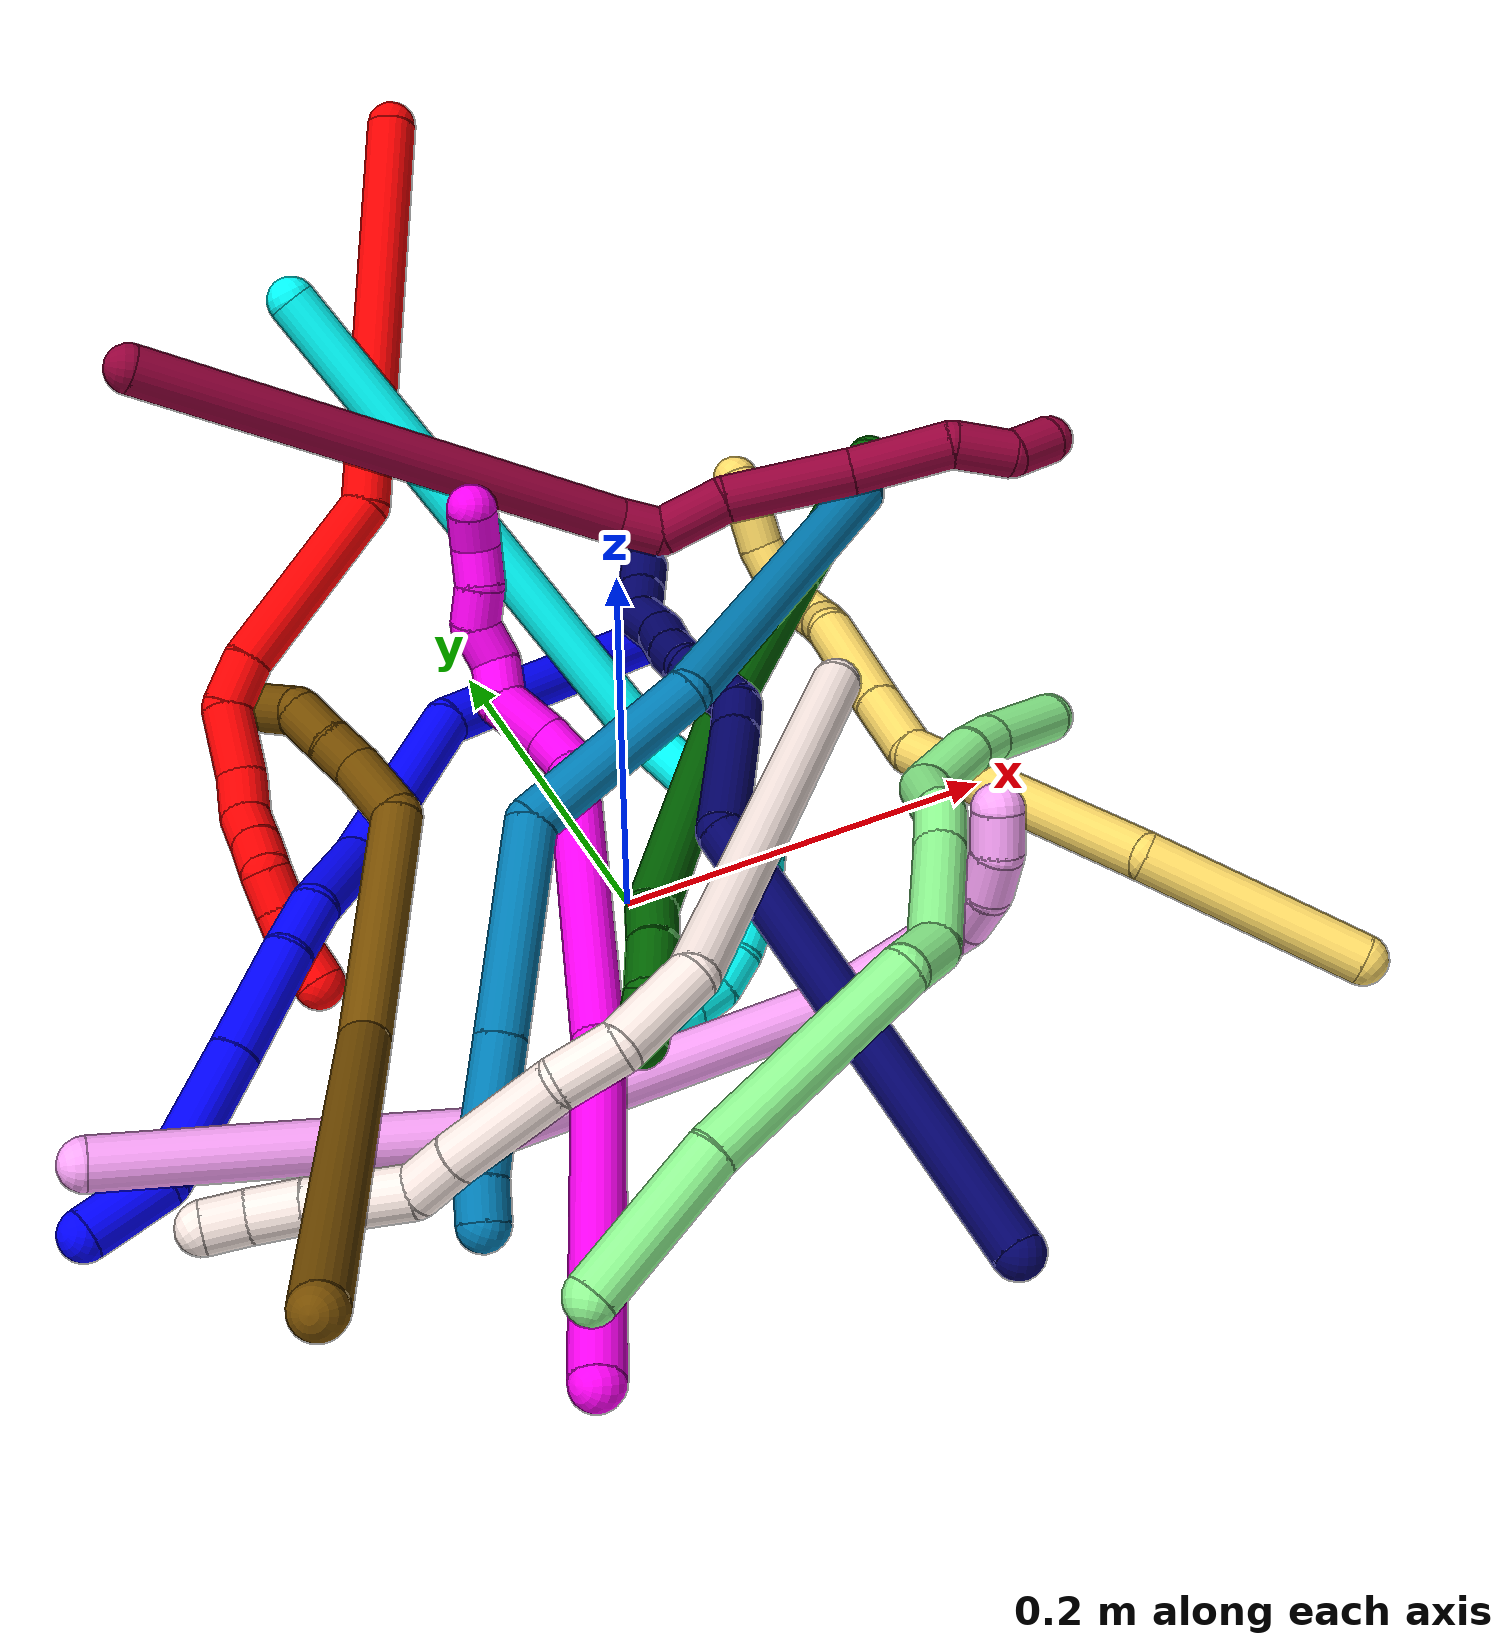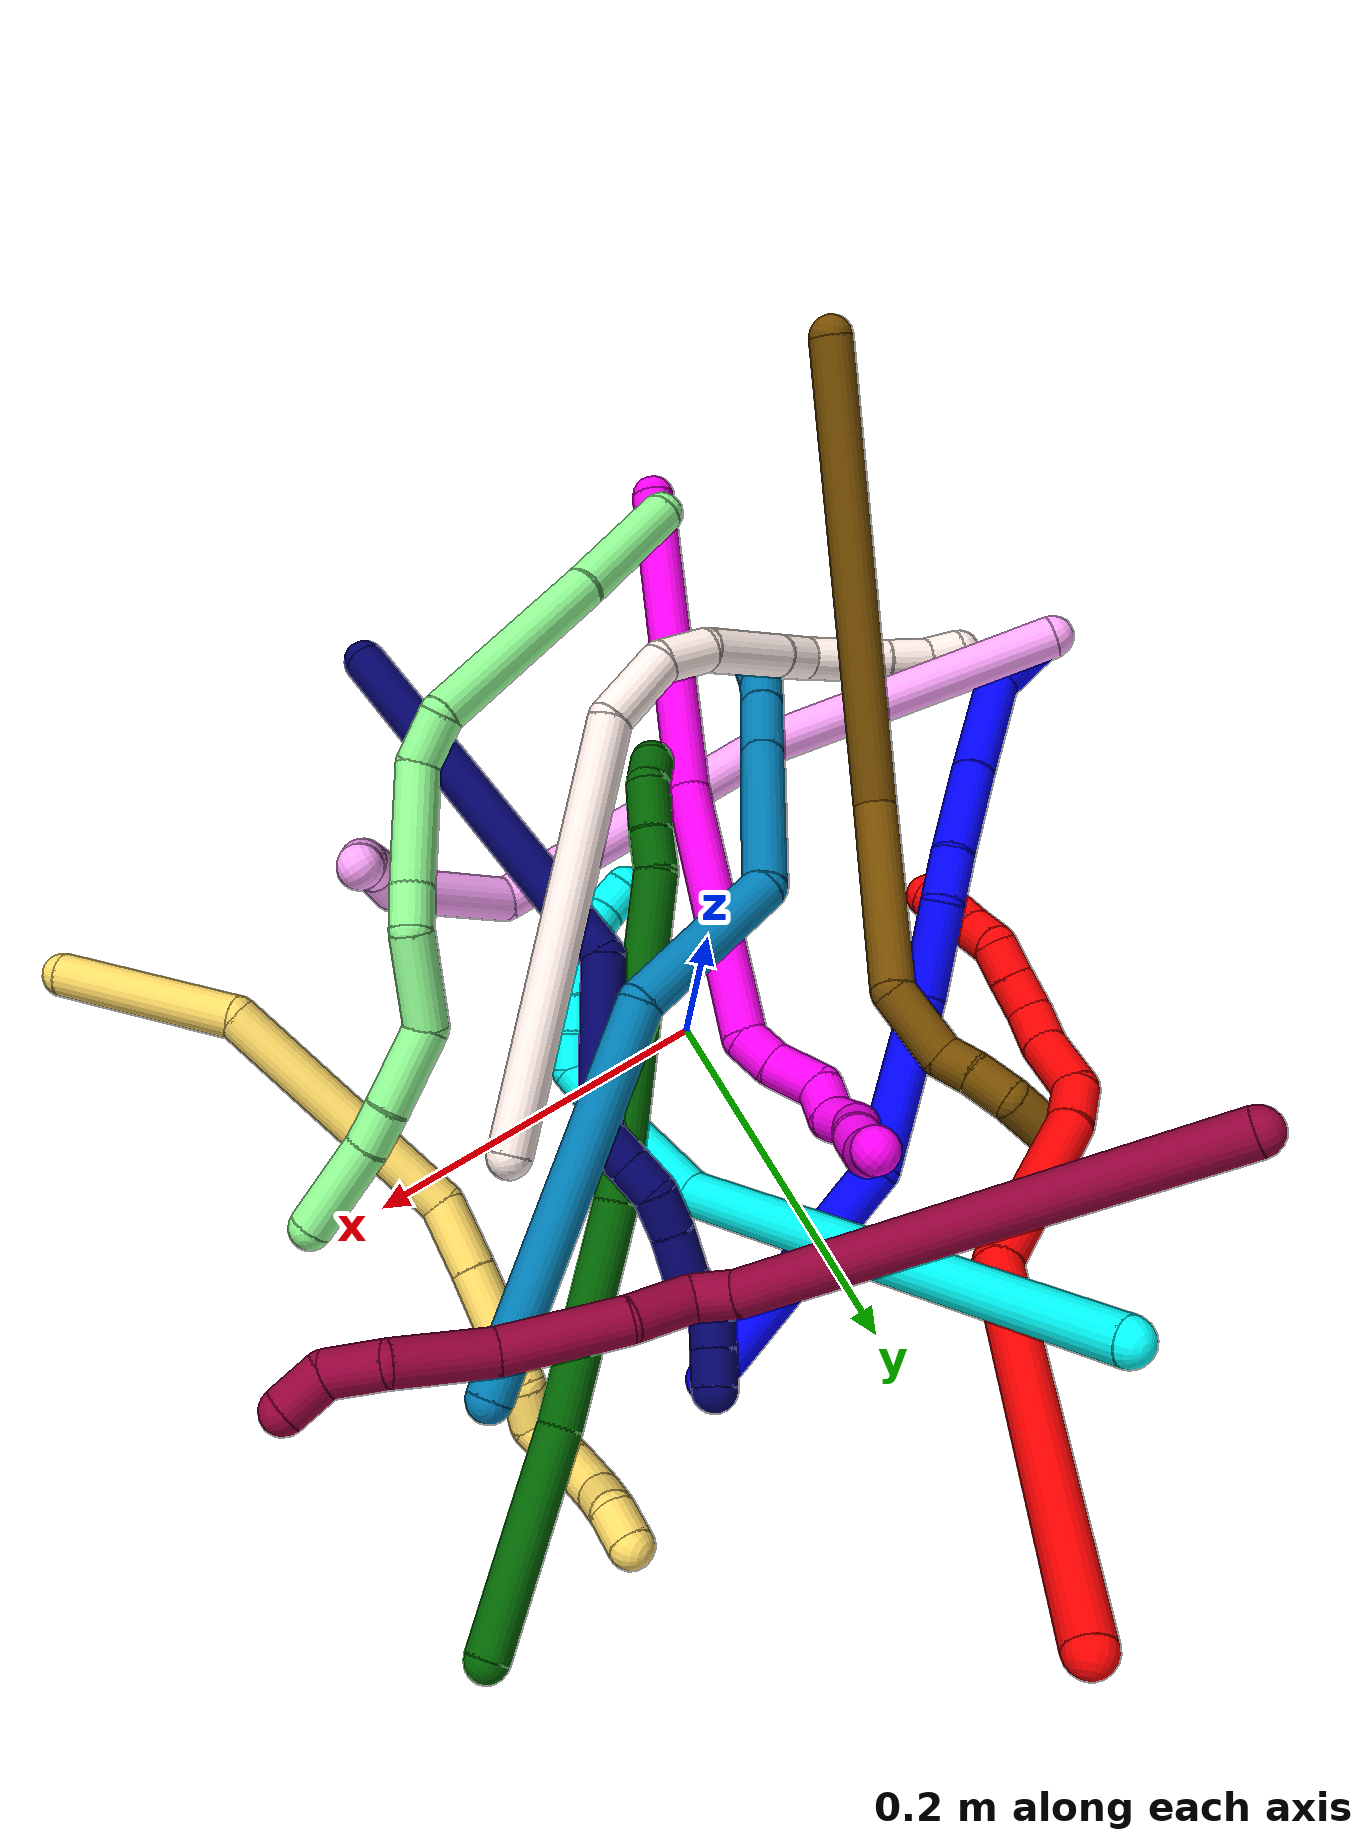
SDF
<sdf version="1.7">
 <world name="default">
  <plugin name="TubeGeneratorPlugin" filename="libtube_generator_plugin.so"/>
  <model name="photoneo_s_sensor">
   <static>1</static>
   <pose>0 0 2 1.57079 1.57079 3.14159</pose>
   <link name="link">
    <inertial><mass>0.1</mass></inertial>
    <sensor name="sensor" type="depth">
     <update_rate>30</update_rate>
     <camera>
      <horizontal_fov>1.22</horizontal_fov>
      <image><width>1920</width><height>1200</height><format>B8G8R8</format></image>
      <clip><near>0.1</near><far>4</far></clip>
      <depth_camera><output>points</output></depth_camera>
     </camera>
     <plugin name="camera_plugin" filename="libgazebo_ros_depth_camera.so">
      <baseline>0.2</baseline>
      <alwaysOn>1</alwaysOn>
      <updateRate>0.0</updateRate>
      <cameraName>camera_ir</cameraName>
      <imageTopicName>/camera/color/image_raw</imageTopicName>
      <cameraInfoTopicName>/camera/color/camera_info</cameraInfoTopicName>
      <depthImageTopicName>/camera/depth/image_raw</depthImageTopicName>
      <depthImageCameraInfoTopicName>/camera/depth/camera_info</depthImageCameraInfoTopicName>
      <pointCloudTopicName>/camera/depth/points</pointCloudTopicName>
      <frameName>fr_optical</frameName>
      <pointCloudCutoff>0.1</pointCloudCutoff>
      <pointCloudCutoffMax>2.0</pointCloudCutoffMax>
      <distortionK1>0</distortionK1>
      <distortionK2>0</distortionK2>
      <distortionK3>0</distortionK3>
      <distortionT1>0</distortionT1>
      <distortionT2>0</distortionT2>
      <CxPrime>0</CxPrime>
      <Cx>0</Cx>
      <Cy>0</Cy>
      <focalLength>0</focalLength>
      <hackBaseline>0</hackBaseline>
     </plugin>
    </sensor>
   </link>
  </model>
  <gravity>0 0 -9.8</gravity>
  <magnetic_field>6e-06 2.3e-05 -4.2e-05</magnetic_field>
  <atmosphere type="adiabatic"/>
  <physics name="default_physics" default="0" type="ode">
   <max_step_size>0.003</max_step_size>
   <real_time_factor>1</real_time_factor>
   <real_time_update_rate>1000</real_time_update_rate>
   <max_contacts>10000</max_contacts>
   <ode>
    <solver>
     <type>quick</type>
     <iters>100</iters>
     <sor>1.3</sor>
     <use_dynamic_moi_rescaling>0</use_dynamic_moi_rescaling>
    </solver>
    <constraints>
     <contact_max_correcting_vel>0</contact_max_correcting_vel>
     <contact_surface_layer>0.001</contact_surface_layer>
     <cfm>0</cfm>
     <erp>0.2</erp>
    </constraints>
   </ode>
  </physics>
  <scene><ambient>0.4 0.4 0.4 1</ambient><background>0.7 0.7 0.7 1</background><shadows>0</shadows></scene>
  <audio><device>default</device></audio>
  <spherical_coordinates>
   <surface_model>EARTH_WGS84</surface_model>
   <latitude_deg>0</latitude_deg>
   <longitude_deg>0</longitude_deg>
   <elevation>0</elevation>
   <heading_deg>0</heading_deg>
  </spherical_coordinates>
  <model name="bin">
   <static>1</static>
   <link name="bottom">
    <collision name="collision-bottom">
     <pose>0 0 -0.01 0 -0 0</pose>
     <geometry><box><size>0.8 0.6 0.02</size></box></geometry>
     <surface>
      <friction><ode><mu>100</mu><mu2>100</mu2></ode></friction>
      <contact><collide_bitmask>65535</collide_bitmask></contact>
     </surface>
    </collision>
   </link>
   <link name="west_wall">
    <collision name="collision-west_wall">
     <pose>-0.41 0 0.1 0 -0 0</pose>
     <geometry><box><size>0.02 0.6 0.2</size></box></geometry>
     <surface>
      <friction><ode><mu>100</mu><mu2>100</mu2></ode></friction>
      <contact><collide_bitmask>65535</collide_bitmask></contact>
     </surface>
    </collision>
   </link>
   <link name="east_wall">
    <collision name="collision-east_wall">
     <pose>0.41 0 0.1 0 -0 0</pose>
     <geometry><box><size>0.02 0.6 0.2</size></box></geometry>
     <surface>
      <friction><ode><mu>100</mu><mu2>100</mu2></ode></friction>
      <contact><collide_bitmask>65535</collide_bitmask></contact>
     </surface>
    </collision>
   </link>
   <link name="south_wall">
    <collision name="collision-south_wall">
     <pose>0 -0.31 0.1 0 -0 0</pose>
     <geometry><box><size>0.8 0.02 0.2</size></box></geometry>
     <surface>
      <friction><ode><mu>100</mu><mu2>100</mu2></ode></friction>
      <contact><collide_bitmask>65535</collide_bitmask></contact>
     </surface>
    </collision>
   </link>
   <link name="north_wall">
    <collision name="collision-north_wall">
     <pose>0 0.31 0.1 0 -0 0</pose>
     <geometry><box><size>0.8 0.02 0.2</size></box></geometry>
     <surface>
      <friction><ode><mu>100</mu><mu2>100</mu2></ode></friction>
      <contact><collide_bitmask>65535</collide_bitmask></contact>
     </surface>
    </collision>
   </link>
  </model>
  <model name="1">
   <static>0</static>
   <link name="1">
    <collision name="collision-cylinder-e_1_1_4">
     <pose>-0.033504 0.002951 0.064799 -0.045512 -0.476762 0.011061</pose>
     <geometry><cylinder><radius>0.0125</radius><length>0.146016</length></cylinder></geometry>
     <surface>
      <friction><ode><mu>1.16</mu><mu2>1.16</mu2><slip1>0</slip1><slip2>0</slip2></ode></friction>
      <contact><ode><kp>1e+06</kp><kd>1</kd><max_vel>0</max_vel><min_depth>0.001</min_depth></ode></contact>
     </surface>
    </collision>
    <visual name="visual-cylinder-e_1_1_4">
     <pose>-0.033504 0.002951 0.064799 -0.045512 -0.476762 0.011061</pose>
     <geometry><cylinder><radius>0.0125</radius><length>0.146016</length></cylinder></geometry>
     <material><ambient>0 0 1 1</ambient></material>
    </visual>
    <collision name="collision-cylinder-e_2_4_5">
     <pose>-0.105053 -0.006141 0.161777 0.35815 -0.83628 -0.160519</pose>
     <geometry><cylinder><radius>0.0125</radius><length>0.102526</length></cylinder></geometry>
     <surface>
      <friction><ode><mu>1.16</mu><mu2>1.16</mu2><slip1>0</slip1><slip2>0</slip2></ode></friction>
      <contact><ode><kp>1e+06</kp><kd>1</kd><max_vel>0</max_vel><min_depth>0.001</min_depth></ode></contact>
     </surface>
    </collision>
    <visual name="visual-cylinder-e_2_4_5">
     <pose>-0.105053 -0.006141 0.161777 0.35815 -0.83628 -0.160519</pose>
     <geometry><cylinder><radius>0.0125</radius><length>0.102526</length></cylinder></geometry>
     <material><ambient>0 0 1 1</ambient></material>
    </visual>
    <collision name="collision-cylinder-e_3_5_6">
     <pose>-0.156096 -0.029833 0.215108 0.503329 -0.493808 -0.129429</pose>
     <geometry><cylinder><radius>0.0125</radius><length>0.05485</length></cylinder></geometry>
     <surface>
      <friction><ode><mu>1.16</mu><mu2>1.16</mu2><slip1>0</slip1><slip2>0</slip2></ode></friction>
      <contact><ode><kp>1e+06</kp><kd>1</kd><max_vel>0</max_vel><min_depth>0.001</min_depth></ode></contact>
     </surface>
    </collision>
    <visual name="visual-cylinder-e_3_5_6">
     <pose>-0.156096 -0.029833 0.215108 0.503329 -0.493808 -0.129429</pose>
     <geometry><cylinder><radius>0.0125</radius><length>0.05485</length></cylinder></geometry>
     <material><ambient>0 0 1 1</ambient></material>
    </visual>
    <collision name="collision-cylinder-e_4_6_7">
     <pose>-0.180154 -0.045778 0.245358 0.441328 -0.832662 -0.197729</pose>
     <geometry><cylinder><radius>0.0125</radius><length>0.029899</length></cylinder></geometry>
     <surface>
      <friction><ode><mu>1.16</mu><mu2>1.16</mu2><slip1>0</slip1><slip2>0</slip2></ode></friction>
      <contact><ode><kp>1e+06</kp><kd>1</kd><max_vel>0</max_vel><min_depth>0.001</min_depth></ode></contact>
     </surface>
    </collision>
    <visual name="visual-cylinder-e_4_6_7">
     <pose>-0.180154 -0.045778 0.245358 0.441328 -0.832662 -0.197729</pose>
     <geometry><cylinder><radius>0.0125</radius><length>0.029899</length></cylinder></geometry>
     <material><ambient>0 0 1 1</ambient></material>
    </visual>
    <collision name="collision-cylinder-e_5_7_8">
     <pose>-0.215557 -0.055186 0.269197 0.333682 -1.0008 -0.183659</pose>
     <geometry><cylinder><radius>0.0125</radius><length>0.057833</length></cylinder></geometry>
     <surface>
      <friction><ode><mu>1.16</mu><mu2>1.16</mu2><slip1>0</slip1><slip2>0</slip2></ode></friction>
      <contact><ode><kp>1e+06</kp><kd>1</kd><max_vel>0</max_vel><min_depth>0.001</min_depth></ode></contact>
     </surface>
    </collision>
    <visual name="visual-cylinder-e_5_7_8">
     <pose>-0.215557 -0.055186 0.269197 0.333682 -1.0008 -0.183659</pose>
     <geometry><cylinder><radius>0.0125</radius><length>0.057833</length></cylinder></geometry>
     <material><ambient>0 0 1 1</ambient></material>
    </visual>
    <collision name="collision-cylinder-e_6_8_9">
     <pose>-0.268746 -0.065478 0.301105 0.293155 -1.01464 -0.163758</pose>
     <geometry><cylinder><radius>0.0125</radius><length>0.067925</length></cylinder></geometry>
     <surface>
      <friction><ode><mu>1.16</mu><mu2>1.16</mu2><slip1>0</slip1><slip2>0</slip2></ode></friction>
      <contact><ode><kp>1e+06</kp><kd>1</kd><max_vel>0</max_vel><min_depth>0.001</min_depth></ode></contact>
     </surface>
    </collision>
    <visual name="visual-cylinder-e_6_8_9">
     <pose>-0.268746 -0.065478 0.301105 0.293155 -1.01464 -0.163758</pose>
     <geometry><cylinder><radius>0.0125</radius><length>0.067925</length></cylinder></geometry>
     <material><ambient>0 0 1 1</ambient></material>
    </visual>
    <collision name="collision-cylinder-e_7_9_2">
     <pose>-0.310732 -0.066152 0.333311 -0.291126 -0.696875 0.106407</pose>
     <geometry><cylinder><radius>0.0125</radius><length>0.040951</length></cylinder></geometry>
     <surface>
      <friction><ode><mu>1.16</mu><mu2>1.16</mu2><slip1>0</slip1><slip2>0</slip2></ode></friction>
      <contact><ode><kp>1e+06</kp><kd>1</kd><max_vel>0</max_vel><min_depth>0.001</min_depth></ode></contact>
     </surface>
    </collision>
    <visual name="visual-cylinder-e_7_9_2">
     <pose>-0.310732 -0.066152 0.333311 -0.291126 -0.696875 0.106407</pose>
     <geometry><cylinder><radius>0.0125</radius><length>0.040951</length></cylinder></geometry>
     <material><ambient>0 0 1 1</ambient></material>
    </visual>
    <collision name="collision-sphere-2">
     <pose>-0.323874 -0.061645 0.348352 0 -0 0</pose>
     <geometry><sphere><radius>0.0125</radius></sphere></geometry>
     <surface>
      <friction><ode><mu>1.16</mu><mu2>1.16</mu2><slip1>0</slip1><slip2>0</slip2></ode></friction>
      <contact><ode><kp>1e+06</kp><kd>1</kd><max_vel>0</max_vel><min_depth>0.001</min_depth></ode></contact>
     </surface>
    </collision>
    <visual name="visual-sphere-2">
     <pose>-0.323874 -0.061645 0.348352 0 -0 0</pose>
     <geometry><sphere><radius>0.0125</radius></sphere></geometry>
     <material><ambient>0 0 1 1</ambient></material>
    </visual>
    <collision name="collision-sphere-9">
     <pose>-0.29759 -0.070659 0.31827 0 -0 0</pose>
     <geometry><sphere><radius>0.0125</radius></sphere></geometry>
     <surface>
      <friction><ode><mu>1.16</mu><mu2>1.16</mu2><slip1>0</slip1><slip2>0</slip2></ode></friction>
      <contact><ode><kp>1e+06</kp><kd>1</kd><max_vel>0</max_vel><min_depth>0.001</min_depth></ode></contact>
     </surface>
    </collision>
    <visual name="visual-sphere-9">
     <pose>-0.29759 -0.070659 0.31827 0 -0 0</pose>
     <geometry><sphere><radius>0.0125</radius></sphere></geometry>
     <material><ambient>0 0 1 1</ambient></material>
    </visual>
    <collision name="collision-sphere-4">
     <pose>-0.067008 0.005902 0.129599 0 -0 0</pose>
     <geometry><sphere><radius>0.0125</radius></sphere></geometry>
     <surface>
      <friction><ode><mu>1.16</mu><mu2>1.16</mu2><slip1>0</slip1><slip2>0</slip2></ode></friction>
      <contact><ode><kp>1e+06</kp><kd>1</kd><max_vel>0</max_vel><min_depth>0.001</min_depth></ode></contact>
     </surface>
    </collision>
    <visual name="visual-sphere-4">
     <pose>-0.067008 0.005902 0.129599 0 -0 0</pose>
     <geometry><sphere><radius>0.0125</radius></sphere></geometry>
     <material><ambient>0 0 1 1</ambient></material>
    </visual>
    <collision name="collision-sphere-1">
     <geometry><sphere><radius>0.0125</radius></sphere></geometry>
     <surface>
      <friction><ode><mu>1.16</mu><mu2>1.16</mu2><slip1>0</slip1><slip2>0</slip2></ode></friction>
      <contact><ode><kp>1e+06</kp><kd>1</kd><max_vel>0</max_vel><min_depth>0.001</min_depth></ode></contact>
     </surface>
    </collision>
    <visual name="visual-sphere-1">
     <geometry><sphere><radius>0.0125</radius></sphere></geometry>
     <material><ambient>0 0 1 1</ambient></material>
    </visual>
    <collision name="collision-sphere-8">
     <pose>-0.239902 -0.060296 0.28394 0 -0 0</pose>
     <geometry><sphere><radius>0.0125</radius></sphere></geometry>
     <surface>
      <friction><ode><mu>1.16</mu><mu2>1.16</mu2><slip1>0</slip1><slip2>0</slip2></ode></friction>
      <contact><ode><kp>1e+06</kp><kd>1</kd><max_vel>0</max_vel><min_depth>0.001</min_depth></ode></contact>
     </surface>
    </collision>
    <visual name="visual-sphere-8">
     <pose>-0.239902 -0.060296 0.28394 0 -0 0</pose>
     <geometry><sphere><radius>0.0125</radius></sphere></geometry>
     <material><ambient>0 0 1 1</ambient></material>
    </visual>
    <collision name="collision-sphere-5">
     <pose>-0.143097 -0.018185 0.193954 0 -0 0</pose>
     <geometry><sphere><radius>0.0125</radius></sphere></geometry>
     <surface>
      <friction><ode><mu>1.16</mu><mu2>1.16</mu2><slip1>0</slip1><slip2>0</slip2></ode></friction>
      <contact><ode><kp>1e+06</kp><kd>1</kd><max_vel>0</max_vel><min_depth>0.001</min_depth></ode></contact>
     </surface>
    </collision>
    <visual name="visual-sphere-5">
     <pose>-0.143097 -0.018185 0.193954 0 -0 0</pose>
     <geometry><sphere><radius>0.0125</radius></sphere></geometry>
     <material><ambient>0 0 1 1</ambient></material>
    </visual>
    <collision name="collision-sphere-6">
     <pose>-0.169095 -0.041481 0.236262 0 -0 0</pose>
     <geometry><sphere><radius>0.0125</radius></sphere></geometry>
     <surface>
      <friction><ode><mu>1.16</mu><mu2>1.16</mu2><slip1>0</slip1><slip2>0</slip2></ode></friction>
      <contact><ode><kp>1e+06</kp><kd>1</kd><max_vel>0</max_vel><min_depth>0.001</min_depth></ode></contact>
     </surface>
    </collision>
    <visual name="visual-sphere-6">
     <pose>-0.169095 -0.041481 0.236262 0 -0 0</pose>
     <geometry><sphere><radius>0.0125</radius></sphere></geometry>
     <material><ambient>0 0 1 1</ambient></material>
    </visual>
    <collision name="collision-sphere-7">
     <pose>-0.191212 -0.050075 0.254453 0 -0 0</pose>
     <geometry><sphere><radius>0.0125</radius></sphere></geometry>
     <surface>
      <friction><ode><mu>1.16</mu><mu2>1.16</mu2><slip1>0</slip1><slip2>0</slip2></ode></friction>
      <contact><ode><kp>1e+06</kp><kd>1</kd><max_vel>0</max_vel><min_depth>0.001</min_depth></ode></contact>
     </surface>
    </collision>
    <visual name="visual-sphere-7">
     <pose>-0.191212 -0.050075 0.254453 0 -0 0</pose>
     <geometry><sphere><radius>0.0125</radius></sphere></geometry>
     <material><ambient>0 0 1 1</ambient></material>
    </visual>
    <inertial>
     <pose>-0.146113 -0.027104 0.189706 0 -0 0</pose>
     <mass>0.5</mass>
     <inertia>
      <ixx>0.000305</ixx>
      <ixy>0</ixy>
      <ixz>0</ixz>
      <iyy>0.000408</iyy>
      <iyz>0</iyz>
      <izz>0.000298</izz>
     </inertia>
    </inertial>
   </link>
   <pose>0.093104 0.173564 0.012129 -0.501531 -0.804113 0.830199</pose>
  </model>
  <model name="2">
   <static>0</static>
   <link name="2">
    <collision name="collision-cylinder-e_1_1_4">
     <pose>-0.00374 -0.042469 -0.09683 2.72826 -0.035358 -0.168264</pose>
     <geometry><cylinder><radius>0.0125</radius><length>0.2116</length></cylinder></geometry>
     <surface>
      <friction><ode><mu>1.16</mu><mu2>1.16</mu2><slip1>0</slip1><slip2>0</slip2></ode></friction>
      <contact><ode><kp>1e+06</kp><kd>1</kd><max_vel>0</max_vel><min_depth>0.001</min_depth></ode></contact>
     </surface>
    </collision>
    <visual name="visual-cylinder-e_1_1_4">
     <pose>-0.00374 -0.042469 -0.09683 2.72826 -0.035358 -0.168264</pose>
     <geometry><cylinder><radius>0.0125</radius><length>0.2116</length></cylinder></geometry>
     <material><ambient>1 0 0 1</ambient></material>
    </visual>
    <collision name="collision-cylinder-e_2_4_5">
     <pose>0.011284 -0.086832 -0.240218 3.10096 0.382814 2.93262</pose>
     <geometry><cylinder><radius>0.0125</radius><length>0.100468</length></cylinder></geometry>
     <surface>
      <friction><ode><mu>1.16</mu><mu2>1.16</mu2><slip1>0</slip1><slip2>0</slip2></ode></friction>
      <contact><ode><kp>1e+06</kp><kd>1</kd><max_vel>0</max_vel><min_depth>0.001</min_depth></ode></contact>
     </surface>
    </collision>
    <visual name="visual-cylinder-e_2_4_5">
     <pose>0.011284 -0.086832 -0.240218 3.10096 0.382814 2.93262</pose>
     <geometry><cylinder><radius>0.0125</radius><length>0.100468</length></cylinder></geometry>
     <material><ambient>1 0 0 1</ambient></material>
    </visual>
    <collision name="collision-cylinder-e_3_5_6">
     <pose>0.032558 -0.091089 -0.299652 2.95999 0.189506 1.61363</pose>
     <geometry><cylinder><radius>0.0125</radius><length>0.026655</length></cylinder></geometry>
     <surface>
      <friction><ode><mu>1.16</mu><mu2>1.16</mu2><slip1>0</slip1><slip2>0</slip2></ode></friction>
      <contact><ode><kp>1e+06</kp><kd>1</kd><max_vel>0</max_vel><min_depth>0.001</min_depth></ode></contact>
     </surface>
    </collision>
    <visual name="visual-cylinder-e_3_5_6">
     <pose>0.032558 -0.091089 -0.299652 2.95999 0.189506 1.61363</pose>
     <geometry><cylinder><radius>0.0125</radius><length>0.026655</length></cylinder></geometry>
     <material><ambient>1 0 0 1</ambient></material>
    </visual>
    <collision name="collision-cylinder-e_4_6_7">
     <pose>0.030124 -0.102757 -0.32721 2.57684 -0.277115 -0.8961</pose>
     <geometry><cylinder><radius>0.0125</radius><length>0.036148</length></cylinder></geometry>
     <surface>
      <friction><ode><mu>1.16</mu><mu2>1.16</mu2><slip1>0</slip1><slip2>0</slip2></ode></friction>
      <contact><ode><kp>1e+06</kp><kd>1</kd><max_vel>0</max_vel><min_depth>0.001</min_depth></ode></contact>
     </surface>
    </collision>
    <visual name="visual-cylinder-e_4_6_7">
     <pose>0.030124 -0.102757 -0.32721 2.57684 -0.277115 -0.8961</pose>
     <geometry><cylinder><radius>0.0125</radius><length>0.036148</length></cylinder></geometry>
     <material><ambient>1 0 0 1</ambient></material>
    </visual>
    <collision name="collision-cylinder-e_5_7_8">
     <pose>0.021349 -0.115287 -0.352443 2.8448 -0.334274 -1.69142</pose>
     <geometry><cylinder><radius>0.0125</radius><length>0.023353</length></cylinder></geometry>
     <surface>
      <friction><ode><mu>1.16</mu><mu2>1.16</mu2><slip1>0</slip1><slip2>0</slip2></ode></friction>
      <contact><ode><kp>1e+06</kp><kd>1</kd><max_vel>0</max_vel><min_depth>0.001</min_depth></ode></contact>
     </surface>
    </collision>
    <visual name="visual-cylinder-e_5_7_8">
     <pose>0.021349 -0.115287 -0.352443 2.8448 -0.334274 -1.69142</pose>
     <geometry><cylinder><radius>0.0125</radius><length>0.023353</length></cylinder></geometry>
     <material><ambient>1 0 0 1</ambient></material>
    </visual>
    <collision name="collision-cylinder-e_6_8_9">
     <pose>0.010744 -0.119081 -0.371034 3.07109 -0.698777 -2.94862</pose>
     <geometry><cylinder><radius>0.0125</radius><length>0.021061</length></cylinder></geometry>
     <surface>
      <friction><ode><mu>1.16</mu><mu2>1.16</mu2><slip1>0</slip1><slip2>0</slip2></ode></friction>
      <contact><ode><kp>1e+06</kp><kd>1</kd><max_vel>0</max_vel><min_depth>0.001</min_depth></ode></contact>
     </surface>
    </collision>
    <visual name="visual-cylinder-e_6_8_9">
     <pose>0.010744 -0.119081 -0.371034 3.07109 -0.698777 -2.94862</pose>
     <geometry><cylinder><radius>0.0125</radius><length>0.021061</length></cylinder></geometry>
     <material><ambient>1 0 0 1</ambient></material>
    </visual>
    <collision name="collision-cylinder-e_7_9_10">
     <pose>-0.002388 -0.12013 -0.387177 3.08231 -0.664599 -2.97017</pose>
     <geometry><cylinder><radius>0.0125</radius><length>0.020617</length></cylinder></geometry>
     <surface>
      <friction><ode><mu>1.16</mu><mu2>1.16</mu2><slip1>0</slip1><slip2>0</slip2></ode></friction>
      <contact><ode><kp>1e+06</kp><kd>1</kd><max_vel>0</max_vel><min_depth>0.001</min_depth></ode></contact>
     </surface>
    </collision>
    <visual name="visual-cylinder-e_7_9_10">
     <pose>-0.002388 -0.12013 -0.387177 3.08231 -0.664599 -2.97017</pose>
     <geometry><cylinder><radius>0.0125</radius><length>0.020617</length></cylinder></geometry>
     <material><ambient>1 0 0 1</ambient></material>
    </visual>
    <collision name="collision-cylinder-e_8_10_11">
     <pose>-0.011935 -0.127163 -0.402137 2.37916 -0.324289 -0.774954</pose>
     <geometry><cylinder><radius>0.0125</radius><length>0.020016</length></cylinder></geometry>
     <surface>
      <friction><ode><mu>1.16</mu><mu2>1.16</mu2><slip1>0</slip1><slip2>0</slip2></ode></friction>
      <contact><ode><kp>1e+06</kp><kd>1</kd><max_vel>0</max_vel><min_depth>0.001</min_depth></ode></contact>
     </surface>
    </collision>
    <visual name="visual-cylinder-e_8_10_11">
     <pose>-0.011935 -0.127163 -0.402137 2.37916 -0.324289 -0.774954</pose>
     <geometry><cylinder><radius>0.0125</radius><length>0.020016</length></cylinder></geometry>
     <material><ambient>1 0 0 1</ambient></material>
    </visual>
    <collision name="collision-cylinder-e_9_11_12">
     <pose>-0.018942 -0.139669 -0.416114 2.44493 -0.39032 -0.996997</pose>
     <geometry><cylinder><radius>0.0125</radius><length>0.020066</length></cylinder></geometry>
     <surface>
      <friction><ode><mu>1.16</mu><mu2>1.16</mu2><slip1>0</slip1><slip2>0</slip2></ode></friction>
      <contact><ode><kp>1e+06</kp><kd>1</kd><max_vel>0</max_vel><min_depth>0.001</min_depth></ode></contact>
     </surface>
    </collision>
    <visual name="visual-cylinder-e_9_11_12">
     <pose>-0.018942 -0.139669 -0.416114 2.44493 -0.39032 -0.996997</pose>
     <geometry><cylinder><radius>0.0125</radius><length>0.020066</length></cylinder></geometry>
     <material><ambient>1 0 0 1</ambient></material>
    </visual>
    <collision name="collision-cylinder-e_10_12_2">
     <pose>-0.027986 -0.151801 -0.429118 2.33206 -0.549508 -1.1639</pose>
     <geometry><cylinder><radius>0.0125</radius><length>0.020015</length></cylinder></geometry>
     <surface>
      <friction><ode><mu>1.16</mu><mu2>1.16</mu2><slip1>0</slip1><slip2>0</slip2></ode></friction>
      <contact><ode><kp>1e+06</kp><kd>1</kd><max_vel>0</max_vel><min_depth>0.001</min_depth></ode></contact>
     </surface>
    </collision>
    <visual name="visual-cylinder-e_10_12_2">
     <pose>-0.027986 -0.151801 -0.429118 2.33206 -0.549508 -1.1639</pose>
     <geometry><cylinder><radius>0.0125</radius><length>0.020015</length></cylinder></geometry>
     <material><ambient>1 0 0 1</ambient></material>
    </visual>
    <collision name="collision-sphere-2">
     <pose>-0.033212 -0.157979 -0.435005 0 -0 0</pose>
     <geometry><sphere><radius>0.0125</radius></sphere></geometry>
     <surface>
      <friction><ode><mu>1.16</mu><mu2>1.16</mu2><slip1>0</slip1><slip2>0</slip2></ode></friction>
      <contact><ode><kp>1e+06</kp><kd>1</kd><max_vel>0</max_vel><min_depth>0.001</min_depth></ode></contact>
     </surface>
    </collision>
    <visual name="visual-sphere-2">
     <pose>-0.033212 -0.157979 -0.435005 0 -0 0</pose>
     <geometry><sphere><radius>0.0125</radius></sphere></geometry>
     <material><ambient>1 0 0 1</ambient></material>
    </visual>
    <collision name="collision-sphere-12">
     <pose>-0.022759 -0.145622 -0.423231 0 -0 0</pose>
     <geometry><sphere><radius>0.0125</radius></sphere></geometry>
     <surface>
      <friction><ode><mu>1.16</mu><mu2>1.16</mu2><slip1>0</slip1><slip2>0</slip2></ode></friction>
      <contact><ode><kp>1e+06</kp><kd>1</kd><max_vel>0</max_vel><min_depth>0.001</min_depth></ode></contact>
     </surface>
    </collision>
    <visual name="visual-sphere-12">
     <pose>-0.022759 -0.145622 -0.423231 0 -0 0</pose>
     <geometry><sphere><radius>0.0125</radius></sphere></geometry>
     <material><ambient>1 0 0 1</ambient></material>
    </visual>
    <collision name="collision-sphere-11">
     <pose>-0.015124 -0.133715 -0.408997 0 -0 0</pose>
     <geometry><sphere><radius>0.0125</radius></sphere></geometry>
     <surface>
      <friction><ode><mu>1.16</mu><mu2>1.16</mu2><slip1>0</slip1><slip2>0</slip2></ode></friction>
      <contact><ode><kp>1e+06</kp><kd>1</kd><max_vel>0</max_vel><min_depth>0.001</min_depth></ode></contact>
     </surface>
    </collision>
    <visual name="visual-sphere-11">
     <pose>-0.015124 -0.133715 -0.408997 0 -0 0</pose>
     <geometry><sphere><radius>0.0125</radius></sphere></geometry>
     <material><ambient>1 0 0 1</ambient></material>
    </visual>
    <collision name="collision-sphere-10">
     <pose>-0.008746 -0.120611 -0.395277 0 -0 0</pose>
     <geometry><sphere><radius>0.0125</radius></sphere></geometry>
     <surface>
      <friction><ode><mu>1.16</mu><mu2>1.16</mu2><slip1>0</slip1><slip2>0</slip2></ode></friction>
      <contact><ode><kp>1e+06</kp><kd>1</kd><max_vel>0</max_vel><min_depth>0.001</min_depth></ode></contact>
     </surface>
    </collision>
    <visual name="visual-sphere-10">
     <pose>-0.008746 -0.120611 -0.395277 0 -0 0</pose>
     <geometry><sphere><radius>0.0125</radius></sphere></geometry>
     <material><ambient>1 0 0 1</ambient></material>
    </visual>
    <collision name="collision-sphere-9">
     <pose>0.003969 -0.119649 -0.379076 0 -0 0</pose>
     <geometry><sphere><radius>0.0125</radius></sphere></geometry>
     <surface>
      <friction><ode><mu>1.16</mu><mu2>1.16</mu2><slip1>0</slip1><slip2>0</slip2></ode></friction>
      <contact><ode><kp>1e+06</kp><kd>1</kd><max_vel>0</max_vel><min_depth>0.001</min_depth></ode></contact>
     </surface>
    </collision>
    <visual name="visual-sphere-9">
     <pose>0.003969 -0.119649 -0.379076 0 -0 0</pose>
     <geometry><sphere><radius>0.0125</radius></sphere></geometry>
     <material><ambient>1 0 0 1</ambient></material>
    </visual>
    <collision name="collision-sphere-4">
     <pose>-0.00748 -0.084939 -0.193659 0 -0 0</pose>
     <geometry><sphere><radius>0.0125</radius></sphere></geometry>
     <surface>
      <friction><ode><mu>1.16</mu><mu2>1.16</mu2><slip1>0</slip1><slip2>0</slip2></ode></friction>
      <contact><ode><kp>1e+06</kp><kd>1</kd><max_vel>0</max_vel><min_depth>0.001</min_depth></ode></contact>
     </surface>
    </collision>
    <visual name="visual-sphere-4">
     <pose>-0.00748 -0.084939 -0.193659 0 -0 0</pose>
     <geometry><sphere><radius>0.0125</radius></sphere></geometry>
     <material><ambient>1 0 0 1</ambient></material>
    </visual>
    <collision name="collision-sphere-1">
     <geometry><sphere><radius>0.0125</radius></sphere></geometry>
     <surface>
      <friction><ode><mu>1.16</mu><mu2>1.16</mu2><slip1>0</slip1><slip2>0</slip2></ode></friction>
      <contact><ode><kp>1e+06</kp><kd>1</kd><max_vel>0</max_vel><min_depth>0.001</min_depth></ode></contact>
     </surface>
    </collision>
    <visual name="visual-sphere-1">
     <geometry><sphere><radius>0.0125</radius></sphere></geometry>
     <material><ambient>1 0 0 1</ambient></material>
    </visual>
    <collision name="collision-sphere-8">
     <pose>0.017518 -0.118513 -0.362991 0 -0 0</pose>
     <geometry><sphere><radius>0.0125</radius></sphere></geometry>
     <surface>
      <friction><ode><mu>1.16</mu><mu2>1.16</mu2><slip1>0</slip1><slip2>0</slip2></ode></friction>
      <contact><ode><kp>1e+06</kp><kd>1</kd><max_vel>0</max_vel><min_depth>0.001</min_depth></ode></contact>
     </surface>
    </collision>
    <visual name="visual-sphere-8">
     <pose>0.017518 -0.118513 -0.362991 0 -0 0</pose>
     <geometry><sphere><radius>0.0125</radius></sphere></geometry>
     <material><ambient>1 0 0 1</ambient></material>
    </visual>
    <collision name="collision-sphere-5">
     <pose>0.030048 -0.088725 -0.286778 0 -0 0</pose>
     <geometry><sphere><radius>0.0125</radius></sphere></geometry>
     <surface>
      <friction><ode><mu>1.16</mu><mu2>1.16</mu2><slip1>0</slip1><slip2>0</slip2></ode></friction>
      <contact><ode><kp>1e+06</kp><kd>1</kd><max_vel>0</max_vel><min_depth>0.001</min_depth></ode></contact>
     </surface>
    </collision>
    <visual name="visual-sphere-5">
     <pose>0.030048 -0.088725 -0.286778 0 -0 0</pose>
     <geometry><sphere><radius>0.0125</radius></sphere></geometry>
     <material><ambient>1 0 0 1</ambient></material>
    </visual>
    <collision name="collision-sphere-6">
     <pose>0.035069 -0.093453 -0.312525 0 -0 0</pose>
     <geometry><sphere><radius>0.0125</radius></sphere></geometry>
     <surface>
      <friction><ode><mu>1.16</mu><mu2>1.16</mu2><slip1>0</slip1><slip2>0</slip2></ode></friction>
      <contact><ode><kp>1e+06</kp><kd>1</kd><max_vel>0</max_vel><min_depth>0.001</min_depth></ode></contact>
     </surface>
    </collision>
    <visual name="visual-sphere-6">
     <pose>0.035069 -0.093453 -0.312525 0 -0 0</pose>
     <geometry><sphere><radius>0.0125</radius></sphere></geometry>
     <material><ambient>1 0 0 1</ambient></material>
    </visual>
    <collision name="collision-sphere-7">
     <pose>0.025179 -0.112061 -0.341895 0 -0 0</pose>
     <geometry><sphere><radius>0.0125</radius></sphere></geometry>
     <surface>
      <friction><ode><mu>1.16</mu><mu2>1.16</mu2><slip1>0</slip1><slip2>0</slip2></ode></friction>
      <contact><ode><kp>1e+06</kp><kd>1</kd><max_vel>0</max_vel><min_depth>0.001</min_depth></ode></contact>
     </surface>
    </collision>
    <visual name="visual-sphere-7">
     <pose>0.025179 -0.112061 -0.341895 0 -0 0</pose>
     <geometry><sphere><radius>0.0125</radius></sphere></geometry>
     <material><ambient>1 0 0 1</ambient></material>
    </visual>
    <inertial>
     <pose>0.003591 -0.079832 -0.226908 0 -0 0</pose>
     <mass>0.5</mass>
     <inertia>
      <ixx>0.000582</ixx>
      <ixy>0</ixy>
      <ixz>0</ixz>
      <iyy>-0.000767</iyy>
      <iyz>0</iyz>
      <izz>0.000297</izz>
     </inertia>
    </inertial>
   </link>
   <pose>0.034664 0.348771 0.25547 1.27597 0.394386 2.27303</pose>
  </model>
  <model name="3">
   <static>0</static>
   <link name="3">
    <collision name="collision-cylinder-e_1_1_4">
     <pose>0.027119 0.004151 -0.138718 -3.11168 0.192978 -2.83496</pose>
     <geometry><cylinder><radius>0.0125</radius><length>0.282809</length></cylinder></geometry>
     <surface>
      <friction><ode><mu>1.16</mu><mu2>1.16</mu2><slip1>0</slip1><slip2>0</slip2></ode></friction>
      <contact><ode><kp>1e+06</kp><kd>1</kd><max_vel>0</max_vel><min_depth>0.001</min_depth></ode></contact>
     </surface>
    </collision>
    <visual name="visual-cylinder-e_1_1_4">
     <pose>0.027119 0.004151 -0.138718 -3.11168 0.192978 -2.83496</pose>
     <geometry><cylinder><radius>0.0125</radius><length>0.282809</length></cylinder></geometry>
     <material><ambient>0.003922 1 0.996078 1</ambient></material>
    </visual>
    <collision name="collision-cylinder-e_2_4_5">
     <pose>0.062799 -0.006863 -0.295754 2.45015 0.345549 0.902354</pose>
     <geometry><cylinder><radius>0.0125</radius><length>0.05055</length></cylinder></geometry>
     <surface>
      <friction><ode><mu>1.16</mu><mu2>1.16</mu2><slip1>0</slip1><slip2>0</slip2></ode></friction>
      <contact><ode><kp>1e+06</kp><kd>1</kd><max_vel>0</max_vel><min_depth>0.001</min_depth></ode></contact>
     </surface>
    </collision>
    <visual name="visual-cylinder-e_2_4_5">
     <pose>0.062799 -0.006863 -0.295754 2.45015 0.345549 0.902354</pose>
     <geometry><cylinder><radius>0.0125</radius><length>0.05055</length></cylinder></geometry>
     <material><ambient>0.003922 1 0.996078 1</ambient></material>
    </visual>
    <collision name="collision-cylinder-e_3_5_6">
     <pose>0.075373 -0.030856 -0.322696 2.34438 0.314446 0.720034</pose>
     <geometry><cylinder><radius>0.0125</radius><length>0.025955</length></cylinder></geometry>
     <surface>
      <friction><ode><mu>1.16</mu><mu2>1.16</mu2><slip1>0</slip1><slip2>0</slip2></ode></friction>
      <contact><ode><kp>1e+06</kp><kd>1</kd><max_vel>0</max_vel><min_depth>0.001</min_depth></ode></contact>
     </surface>
    </collision>
    <visual name="visual-cylinder-e_3_5_6">
     <pose>0.075373 -0.030856 -0.322696 2.34438 0.314446 0.720034</pose>
     <geometry><cylinder><radius>0.0125</radius><length>0.025955</length></cylinder></geometry>
     <material><ambient>0.003922 1 0.996078 1</ambient></material>
    </visual>
    <collision name="collision-cylinder-e_4_6_7">
     <pose>0.082277 -0.046536 -0.338021 2.3452 0.292877 0.674457</pose>
     <geometry><cylinder><radius>0.0125</radius><length>0.020022</length></cylinder></geometry>
     <surface>
      <friction><ode><mu>1.16</mu><mu2>1.16</mu2><slip1>0</slip1><slip2>0</slip2></ode></friction>
      <contact><ode><kp>1e+06</kp><kd>1</kd><max_vel>0</max_vel><min_depth>0.001</min_depth></ode></contact>
     </surface>
    </collision>
    <visual name="visual-cylinder-e_4_6_7">
     <pose>0.082277 -0.046536 -0.338021 2.3452 0.292877 0.674457</pose>
     <geometry><cylinder><radius>0.0125</radius><length>0.020022</length></cylinder></geometry>
     <material><ambient>0.003922 1 0.996078 1</ambient></material>
    </visual>
    <collision name="collision-cylinder-e_5_7_8">
     <pose>0.082525 -0.062754 -0.347236 1.83288 -0.266016 -0.345367</pose>
     <geometry><cylinder><radius>0.0125</radius><length>0.020102</length></cylinder></geometry>
     <surface>
      <friction><ode><mu>1.16</mu><mu2>1.16</mu2><slip1>0</slip1><slip2>0</slip2></ode></friction>
      <contact><ode><kp>1e+06</kp><kd>1</kd><max_vel>0</max_vel><min_depth>0.001</min_depth></ode></contact>
     </surface>
    </collision>
    <visual name="visual-cylinder-e_5_7_8">
     <pose>0.082525 -0.062754 -0.347236 1.83288 -0.266016 -0.345367</pose>
     <geometry><cylinder><radius>0.0125</radius><length>0.020102</length></cylinder></geometry>
     <material><ambient>0.003922 1 0.996078 1</ambient></material>
    </visual>
    <collision name="collision-cylinder-e_6_8_9">
     <pose>0.07675 -0.08094 -0.353409 1.96417 -0.317072 -0.470047</pose>
     <geometry><cylinder><radius>0.0125</radius><length>0.020099</length></cylinder></geometry>
     <surface>
      <friction><ode><mu>1.16</mu><mu2>1.16</mu2><slip1>0</slip1><slip2>0</slip2></ode></friction>
      <contact><ode><kp>1e+06</kp><kd>1</kd><max_vel>0</max_vel><min_depth>0.001</min_depth></ode></contact>
     </surface>
    </collision>
    <visual name="visual-cylinder-e_6_8_9">
     <pose>0.07675 -0.08094 -0.353409 1.96417 -0.317072 -0.470047</pose>
     <geometry><cylinder><radius>0.0125</radius><length>0.020099</length></cylinder></geometry>
     <material><ambient>0.003922 1 0.996078 1</ambient></material>
    </visual>
    <collision name="collision-cylinder-e_7_9_10">
     <pose>0.06959 -0.098421 -0.360727 1.9704 -0.404558 -0.599818</pose>
     <geometry><cylinder><radius>0.0125</radius><length>0.020456</length></cylinder></geometry>
     <surface>
      <friction><ode><mu>1.16</mu><mu2>1.16</mu2><slip1>0</slip1><slip2>0</slip2></ode></friction>
      <contact><ode><kp>1e+06</kp><kd>1</kd><max_vel>0</max_vel><min_depth>0.001</min_depth></ode></contact>
     </surface>
    </collision>
    <visual name="visual-cylinder-e_7_9_10">
     <pose>0.06959 -0.098421 -0.360727 1.9704 -0.404558 -0.599818</pose>
     <geometry><cylinder><radius>0.0125</radius><length>0.020456</length></cylinder></geometry>
     <material><ambient>0.003922 1 0.996078 1</ambient></material>
    </visual>
    <collision name="collision-cylinder-e_8_10_11">
     <pose>0.059053 -0.112653 -0.369542 2.31764 -0.709035 -1.40558</pose>
     <geometry><cylinder><radius>0.0125</radius><length>0.020002</length></cylinder></geometry>
     <surface>
      <friction><ode><mu>1.16</mu><mu2>1.16</mu2><slip1>0</slip1><slip2>0</slip2></ode></friction>
      <contact><ode><kp>1e+06</kp><kd>1</kd><max_vel>0</max_vel><min_depth>0.001</min_depth></ode></contact>
     </surface>
    </collision>
    <visual name="visual-cylinder-e_8_10_11">
     <pose>0.059053 -0.112653 -0.369542 2.31764 -0.709035 -1.40558</pose>
     <geometry><cylinder><radius>0.0125</radius><length>0.020002</length></cylinder></geometry>
     <material><ambient>0.003922 1 0.996078 1</ambient></material>
    </visual>
    <collision name="collision-cylinder-e_9_11_12">
     <pose>0.044534 -0.122293 -0.379098 2.39521 -0.92823 -1.81406</pose>
     <geometry><cylinder><radius>0.0125</radius><length>0.020004</length></cylinder></geometry>
     <surface>
      <friction><ode><mu>1.16</mu><mu2>1.16</mu2><slip1>0</slip1><slip2>0</slip2></ode></friction>
      <contact><ode><kp>1e+06</kp><kd>1</kd><max_vel>0</max_vel><min_depth>0.001</min_depth></ode></contact>
     </surface>
    </collision>
    <visual name="visual-cylinder-e_9_11_12">
     <pose>0.044534 -0.122293 -0.379098 2.39521 -0.92823 -1.81406</pose>
     <geometry><cylinder><radius>0.0125</radius><length>0.020004</length></cylinder></geometry>
     <material><ambient>0.003922 1 0.996078 1</ambient></material>
    </visual>
    <collision name="collision-cylinder-e_10_12_2">
     <pose>0.028474 -0.132292 -0.383513 1.57322 -0.936099 -0.938053</pose>
     <geometry><cylinder><radius>0.0125</radius><length>0.020001</length></cylinder></geometry>
     <surface>
      <friction><ode><mu>1.16</mu><mu2>1.16</mu2><slip1>0</slip1><slip2>0</slip2></ode></friction>
      <contact><ode><kp>1e+06</kp><kd>1</kd><max_vel>0</max_vel><min_depth>0.001</min_depth></ode></contact>
     </surface>
    </collision>
    <visual name="visual-cylinder-e_10_12_2">
     <pose>0.028474 -0.132292 -0.383513 1.57322 -0.936099 -0.938053</pose>
     <geometry><cylinder><radius>0.0125</radius><length>0.020001</length></cylinder></geometry>
     <material><ambient>0.003922 1 0.996078 1</ambient></material>
    </visual>
    <collision name="collision-sphere-2">
     <pose>0.020421 -0.138222 -0.383527 0 -0 0</pose>
     <geometry><sphere><radius>0.0125</radius></sphere></geometry>
     <surface>
      <friction><ode><mu>1.16</mu><mu2>1.16</mu2><slip1>0</slip1><slip2>0</slip2></ode></friction>
      <contact><ode><kp>1e+06</kp><kd>1</kd><max_vel>0</max_vel><min_depth>0.001</min_depth></ode></contact>
     </surface>
    </collision>
    <visual name="visual-sphere-2">
     <pose>0.020421 -0.138222 -0.383527 0 -0 0</pose>
     <geometry><sphere><radius>0.0125</radius></sphere></geometry>
     <material><ambient>0.003922 1 0.996078 1</ambient></material>
    </visual>
    <collision name="collision-sphere-12">
     <pose>0.036527 -0.126363 -0.383499 0 -0 0</pose>
     <geometry><sphere><radius>0.0125</radius></sphere></geometry>
     <surface>
      <friction><ode><mu>1.16</mu><mu2>1.16</mu2><slip1>0</slip1><slip2>0</slip2></ode></friction>
      <contact><ode><kp>1e+06</kp><kd>1</kd><max_vel>0</max_vel><min_depth>0.001</min_depth></ode></contact>
     </surface>
    </collision>
    <visual name="visual-sphere-12">
     <pose>0.036527 -0.126363 -0.383499 0 -0 0</pose>
     <geometry><sphere><radius>0.0125</radius></sphere></geometry>
     <material><ambient>0.003922 1 0.996078 1</ambient></material>
    </visual>
    <collision name="collision-sphere-11">
     <pose>0.052541 -0.118223 -0.374698 0 -0 0</pose>
     <geometry><sphere><radius>0.0125</radius></sphere></geometry>
     <surface>
      <friction><ode><mu>1.16</mu><mu2>1.16</mu2><slip1>0</slip1><slip2>0</slip2></ode></friction>
      <contact><ode><kp>1e+06</kp><kd>1</kd><max_vel>0</max_vel><min_depth>0.001</min_depth></ode></contact>
     </surface>
    </collision>
    <visual name="visual-sphere-11">
     <pose>0.052541 -0.118223 -0.374698 0 -0 0</pose>
     <geometry><sphere><radius>0.0125</radius></sphere></geometry>
     <material><ambient>0.003922 1 0.996078 1</ambient></material>
    </visual>
    <collision name="collision-sphere-10">
     <pose>0.065565 -0.107083 -0.364385 0 -0 0</pose>
     <geometry><sphere><radius>0.0125</radius></sphere></geometry>
     <surface>
      <friction><ode><mu>1.16</mu><mu2>1.16</mu2><slip1>0</slip1><slip2>0</slip2></ode></friction>
      <contact><ode><kp>1e+06</kp><kd>1</kd><max_vel>0</max_vel><min_depth>0.001</min_depth></ode></contact>
     </surface>
    </collision>
    <visual name="visual-sphere-10">
     <pose>0.065565 -0.107083 -0.364385 0 -0 0</pose>
     <geometry><sphere><radius>0.0125</radius></sphere></geometry>
     <material><ambient>0.003922 1 0.996078 1</ambient></material>
    </visual>
    <collision name="collision-sphere-9">
     <pose>0.073616 -0.08976 -0.357069 0 -0 0</pose>
     <geometry><sphere><radius>0.0125</radius></sphere></geometry>
     <surface>
      <friction><ode><mu>1.16</mu><mu2>1.16</mu2><slip1>0</slip1><slip2>0</slip2></ode></friction>
      <contact><ode><kp>1e+06</kp><kd>1</kd><max_vel>0</max_vel><min_depth>0.001</min_depth></ode></contact>
     </surface>
    </collision>
    <visual name="visual-sphere-9">
     <pose>0.073616 -0.08976 -0.357069 0 -0 0</pose>
     <geometry><sphere><radius>0.0125</radius></sphere></geometry>
     <material><ambient>0.003922 1 0.996078 1</ambient></material>
    </visual>
    <collision name="collision-sphere-4">
     <pose>0.054238 0.008301 -0.277435 0 -0 0</pose>
     <geometry><sphere><radius>0.0125</radius></sphere></geometry>
     <surface>
      <friction><ode><mu>1.16</mu><mu2>1.16</mu2><slip1>0</slip1><slip2>0</slip2></ode></friction>
      <contact><ode><kp>1e+06</kp><kd>1</kd><max_vel>0</max_vel><min_depth>0.001</min_depth></ode></contact>
     </surface>
    </collision>
    <visual name="visual-sphere-4">
     <pose>0.054238 0.008301 -0.277435 0 -0 0</pose>
     <geometry><sphere><radius>0.0125</radius></sphere></geometry>
     <material><ambient>0.003922 1 0.996078 1</ambient></material>
    </visual>
    <collision name="collision-sphere-1">
     <geometry><sphere><radius>0.0125</radius></sphere></geometry>
     <surface>
      <friction><ode><mu>1.16</mu><mu2>1.16</mu2><slip1>0</slip1><slip2>0</slip2></ode></friction>
      <contact><ode><kp>1e+06</kp><kd>1</kd><max_vel>0</max_vel><min_depth>0.001</min_depth></ode></contact>
     </surface>
    </collision>
    <visual name="visual-sphere-1">
     <geometry><sphere><radius>0.0125</radius></sphere></geometry>
     <material><ambient>0.003922 1 0.996078 1</ambient></material>
    </visual>
    <collision name="collision-sphere-8">
     <pose>0.079883 -0.072121 -0.349749 0 -0 0</pose>
     <geometry><sphere><radius>0.0125</radius></sphere></geometry>
     <surface>
      <friction><ode><mu>1.16</mu><mu2>1.16</mu2><slip1>0</slip1><slip2>0</slip2></ode></friction>
      <contact><ode><kp>1e+06</kp><kd>1</kd><max_vel>0</max_vel><min_depth>0.001</min_depth></ode></contact>
     </surface>
    </collision>
    <visual name="visual-sphere-8">
     <pose>0.079883 -0.072121 -0.349749 0 -0 0</pose>
     <geometry><sphere><radius>0.0125</radius></sphere></geometry>
     <material><ambient>0.003922 1 0.996078 1</ambient></material>
    </visual>
    <collision name="collision-sphere-5">
     <pose>0.07136 -0.022027 -0.314073 0 -0 0</pose>
     <geometry><sphere><radius>0.0125</radius></sphere></geometry>
     <surface>
      <friction><ode><mu>1.16</mu><mu2>1.16</mu2><slip1>0</slip1><slip2>0</slip2></ode></friction>
      <contact><ode><kp>1e+06</kp><kd>1</kd><max_vel>0</max_vel><min_depth>0.001</min_depth></ode></contact>
     </surface>
    </collision>
    <visual name="visual-sphere-5">
     <pose>0.07136 -0.022027 -0.314073 0 -0 0</pose>
     <geometry><sphere><radius>0.0125</radius></sphere></geometry>
     <material><ambient>0.003922 1 0.996078 1</ambient></material>
    </visual>
    <collision name="collision-sphere-6">
     <pose>0.079387 -0.039685 -0.331319 0 -0 0</pose>
     <geometry><sphere><radius>0.0125</radius></sphere></geometry>
     <surface>
      <friction><ode><mu>1.16</mu><mu2>1.16</mu2><slip1>0</slip1><slip2>0</slip2></ode></friction>
      <contact><ode><kp>1e+06</kp><kd>1</kd><max_vel>0</max_vel><min_depth>0.001</min_depth></ode></contact>
     </surface>
    </collision>
    <visual name="visual-sphere-6">
     <pose>0.079387 -0.039685 -0.331319 0 -0 0</pose>
     <geometry><sphere><radius>0.0125</radius></sphere></geometry>
     <material><ambient>0.003922 1 0.996078 1</ambient></material>
    </visual>
    <collision name="collision-sphere-7">
     <pose>0.085168 -0.053388 -0.344724 0 -0 0</pose>
     <geometry><sphere><radius>0.0125</radius></sphere></geometry>
     <surface>
      <friction><ode><mu>1.16</mu><mu2>1.16</mu2><slip1>0</slip1><slip2>0</slip2></ode></friction>
      <contact><ode><kp>1e+06</kp><kd>1</kd><max_vel>0</max_vel><min_depth>0.001</min_depth></ode></contact>
     </surface>
    </collision>
    <visual name="visual-sphere-7">
     <pose>0.085168 -0.053388 -0.344724 0 -0 0</pose>
     <geometry><sphere><radius>0.0125</radius></sphere></geometry>
     <material><ambient>0.003922 1 0.996078 1</ambient></material>
    </visual>
    <inertial>
     <pose>0.043428 -0.026306 -0.226865 0 -0 0</pose>
     <mass>0.5</mass>
     <inertia>
      <ixx>-0.002312</ixx>
      <ixy>0</ixy>
      <ixz>0</ixz>
      <iyy>0.001241</iyy>
      <iyz>0</iyz>
      <izz>-0.000434</izz>
     </inertia>
    </inertial>
   </link>
   <pose>-0.058373 0.25683 0.223712 -0.607203 -0.378071 -0.174965</pose>
  </model>
  <model name="4">
   <static>0</static>
   <link name="4">
    <collision name="collision-cylinder-e_1_1_4">
     <pose>0.007964 -0.017879 -0.08394 2.93173 0.092527 0.828331</pose>
     <geometry><cylinder><radius>0.0125</radius><length>0.172384</length></cylinder></geometry>
     <surface>
      <friction><ode><mu>1.16</mu><mu2>1.16</mu2><slip1>0</slip1><slip2>0</slip2></ode></friction>
      <contact><ode><kp>1e+06</kp><kd>1</kd><max_vel>0</max_vel><min_depth>0.001</min_depth></ode></contact>
     </surface>
    </collision>
    <visual name="visual-cylinder-e_1_1_4">
     <pose>0.007964 -0.017879 -0.08394 2.93173 0.092527 0.828331</pose>
     <geometry><cylinder><radius>0.0125</radius><length>0.172384</length></cylinder></geometry>
     <material><ambient>1 0.65098 0.996078 1</ambient></material>
    </visual>
    <collision name="collision-cylinder-e_2_4_5">
     <pose>0.041196 -0.036471 -0.25567 3.13347 0.280253 3.08399</pose>
     <geometry><cylinder><radius>0.0125</radius><length>0.182712</length></cylinder></geometry>
     <surface>
      <friction><ode><mu>1.16</mu><mu2>1.16</mu2><slip1>0</slip1><slip2>0</slip2></ode></friction>
      <contact><ode><kp>1e+06</kp><kd>1</kd><max_vel>0</max_vel><min_depth>0.001</min_depth></ode></contact>
     </surface>
    </collision>
    <visual name="visual-cylinder-e_2_4_5">
     <pose>0.041196 -0.036471 -0.25567 3.13347 0.280253 3.08399</pose>
     <geometry><cylinder><radius>0.0125</radius><length>0.182712</length></cylinder></geometry>
     <material><ambient>1 0.65098 0.996078 1</ambient></material>
    </visual>
    <collision name="collision-cylinder-e_3_5_6">
     <pose>0.096061 -0.052403 -0.363378 2.48922 0.868042 1.88066</pose>
     <geometry><cylinder><radius>0.0125</radius><length>0.077569</length></cylinder></geometry>
     <surface>
      <friction><ode><mu>1.16</mu><mu2>1.16</mu2><slip1>0</slip1><slip2>0</slip2></ode></friction>
      <contact><ode><kp>1e+06</kp><kd>1</kd><max_vel>0</max_vel><min_depth>0.001</min_depth></ode></contact>
     </surface>
    </collision>
    <visual name="visual-cylinder-e_3_5_6">
     <pose>0.096061 -0.052403 -0.363378 2.48922 0.868042 1.88066</pose>
     <geometry><cylinder><radius>0.0125</radius><length>0.077569</length></cylinder></geometry>
     <material><ambient>1 0.65098 0.996078 1</ambient></material>
    </visual>
    <collision name="collision-cylinder-e_4_6_7">
     <pose>0.136728 -0.073174 -0.382409 1.41217 1.10078 0.964192</pose>
     <geometry><cylinder><radius>0.0125</radius><length>0.024837</length></cylinder></geometry>
     <surface>
      <friction><ode><mu>1.16</mu><mu2>1.16</mu2><slip1>0</slip1><slip2>0</slip2></ode></friction>
      <contact><ode><kp>1e+06</kp><kd>1</kd><max_vel>0</max_vel><min_depth>0.001</min_depth></ode></contact>
     </surface>
    </collision>
    <visual name="visual-cylinder-e_4_6_7">
     <pose>0.136728 -0.073174 -0.382409 1.41217 1.10078 0.964192</pose>
     <geometry><cylinder><radius>0.0125</radius><length>0.024837</length></cylinder></geometry>
     <material><ambient>1 0.65098 0.996078 1</ambient></material>
    </visual>
    <collision name="collision-cylinder-e_5_7_8">
     <pose>0.158764 -0.080101 -0.380561 0.960621 1.41918 0.841462</pose>
     <geometry><cylinder><radius>0.0125</radius><length>0.022184</length></cylinder></geometry>
     <surface>
      <friction><ode><mu>1.16</mu><mu2>1.16</mu2><slip1>0</slip1><slip2>0</slip2></ode></friction>
      <contact><ode><kp>1e+06</kp><kd>1</kd><max_vel>0</max_vel><min_depth>0.001</min_depth></ode></contact>
     </surface>
    </collision>
    <visual name="visual-cylinder-e_5_7_8">
     <pose>0.158764 -0.080101 -0.380561 0.960621 1.41918 0.841462</pose>
     <geometry><cylinder><radius>0.0125</radius><length>0.022184</length></cylinder></geometry>
     <material><ambient>1 0.65098 0.996078 1</ambient></material>
    </visual>
    <collision name="collision-cylinder-e_6_8_2">
     <pose>0.17948 -0.078786 -0.37867 -1.23743 1.28693 -0.980853</pose>
     <geometry><cylinder><radius>0.0125</radius><length>0.020313</length></cylinder></geometry>
     <surface>
      <friction><ode><mu>1.16</mu><mu2>1.16</mu2><slip1>0</slip1><slip2>0</slip2></ode></friction>
      <contact><ode><kp>1e+06</kp><kd>1</kd><max_vel>0</max_vel><min_depth>0.001</min_depth></ode></contact>
     </surface>
    </collision>
    <visual name="visual-cylinder-e_6_8_2">
     <pose>0.17948 -0.078786 -0.37867 -1.23743 1.28693 -0.980853</pose>
     <geometry><cylinder><radius>0.0125</radius><length>0.020313</length></cylinder></geometry>
     <material><ambient>1 0.65098 0.996078 1</ambient></material>
    </visual>
    <collision name="collision-sphere-2">
     <pose>0.18923 -0.076098 -0.377739 0 -0 0</pose>
     <geometry><sphere><radius>0.0125</radius></sphere></geometry>
     <surface>
      <friction><ode><mu>1.16</mu><mu2>1.16</mu2><slip1>0</slip1><slip2>0</slip2></ode></friction>
      <contact><ode><kp>1e+06</kp><kd>1</kd><max_vel>0</max_vel><min_depth>0.001</min_depth></ode></contact>
     </surface>
    </collision>
    <visual name="visual-sphere-2">
     <pose>0.18923 -0.076098 -0.377739 0 -0 0</pose>
     <geometry><sphere><radius>0.0125</radius></sphere></geometry>
     <material><ambient>1 0.65098 0.996078 1</ambient></material>
    </visual>
    <collision name="collision-sphere-4">
     <pose>0.015927 -0.035758 -0.167881 0 -0 0</pose>
     <geometry><sphere><radius>0.0125</radius></sphere></geometry>
     <surface>
      <friction><ode><mu>1.16</mu><mu2>1.16</mu2><slip1>0</slip1><slip2>0</slip2></ode></friction>
      <contact><ode><kp>1e+06</kp><kd>1</kd><max_vel>0</max_vel><min_depth>0.001</min_depth></ode></contact>
     </surface>
    </collision>
    <visual name="visual-sphere-4">
     <pose>0.015927 -0.035758 -0.167881 0 -0 0</pose>
     <geometry><sphere><radius>0.0125</radius></sphere></geometry>
     <material><ambient>1 0.65098 0.996078 1</ambient></material>
    </visual>
    <collision name="collision-sphere-1">
     <geometry><sphere><radius>0.0125</radius></sphere></geometry>
     <surface>
      <friction><ode><mu>1.16</mu><mu2>1.16</mu2><slip1>0</slip1><slip2>0</slip2></ode></friction>
      <contact><ode><kp>1e+06</kp><kd>1</kd><max_vel>0</max_vel><min_depth>0.001</min_depth></ode></contact>
     </surface>
    </collision>
    <visual name="visual-sphere-1">
     <geometry><sphere><radius>0.0125</radius></sphere></geometry>
     <material><ambient>1 0.65098 0.996078 1</ambient></material>
    </visual>
    <collision name="collision-sphere-8">
     <pose>0.169729 -0.081474 -0.379601 0 -0 0</pose>
     <geometry><sphere><radius>0.0125</radius></sphere></geometry>
     <surface>
      <friction><ode><mu>1.16</mu><mu2>1.16</mu2><slip1>0</slip1><slip2>0</slip2></ode></friction>
      <contact><ode><kp>1e+06</kp><kd>1</kd><max_vel>0</max_vel><min_depth>0.001</min_depth></ode></contact>
     </surface>
    </collision>
    <visual name="visual-sphere-8">
     <pose>0.169729 -0.081474 -0.379601 0 -0 0</pose>
     <geometry><sphere><radius>0.0125</radius></sphere></geometry>
     <material><ambient>1 0.65098 0.996078 1</ambient></material>
    </visual>
    <collision name="collision-sphere-5">
     <pose>0.066466 -0.037185 -0.343459 0 -0 0</pose>
     <geometry><sphere><radius>0.0125</radius></sphere></geometry>
     <surface>
      <friction><ode><mu>1.16</mu><mu2>1.16</mu2><slip1>0</slip1><slip2>0</slip2></ode></friction>
      <contact><ode><kp>1e+06</kp><kd>1</kd><max_vel>0</max_vel><min_depth>0.001</min_depth></ode></contact>
     </surface>
    </collision>
    <visual name="visual-sphere-5">
     <pose>0.066466 -0.037185 -0.343459 0 -0 0</pose>
     <geometry><sphere><radius>0.0125</radius></sphere></geometry>
     <material><ambient>1 0.65098 0.996078 1</ambient></material>
    </visual>
    <collision name="collision-sphere-6">
     <pose>0.125656 -0.06762 -0.383298 0 -0 0</pose>
     <geometry><sphere><radius>0.0125</radius></sphere></geometry>
     <surface>
      <friction><ode><mu>1.16</mu><mu2>1.16</mu2><slip1>0</slip1><slip2>0</slip2></ode></friction>
      <contact><ode><kp>1e+06</kp><kd>1</kd><max_vel>0</max_vel><min_depth>0.001</min_depth></ode></contact>
     </surface>
    </collision>
    <visual name="visual-sphere-6">
     <pose>0.125656 -0.06762 -0.383298 0 -0 0</pose>
     <geometry><sphere><radius>0.0125</radius></sphere></geometry>
     <material><ambient>1 0.65098 0.996078 1</ambient></material>
    </visual>
    <collision name="collision-sphere-7">
     <pose>0.147799 -0.078728 -0.381521 0 -0 0</pose>
     <geometry><sphere><radius>0.0125</radius></sphere></geometry>
     <surface>
      <friction><ode><mu>1.16</mu><mu2>1.16</mu2><slip1>0</slip1><slip2>0</slip2></ode></friction>
      <contact><ode><kp>1e+06</kp><kd>1</kd><max_vel>0</max_vel><min_depth>0.001</min_depth></ode></contact>
     </surface>
    </collision>
    <visual name="visual-sphere-7">
     <pose>0.147799 -0.078728 -0.381521 0 -0 0</pose>
     <geometry><sphere><radius>0.0125</radius></sphere></geometry>
     <material><ambient>1 0.65098 0.996078 1</ambient></material>
    </visual>
    <inertial>
     <pose>0.05383 -0.038011 -0.230007 0 -0 0</pose>
     <mass>0.5</mass>
     <inertia>
      <ixx>0.000178</ixx>
      <ixy>0</ixy>
      <ixz>0</ixz>
      <iyy>0.000635</iyy>
      <iyz>0</iyz>
      <izz>-0.000138</izz>
     </inertia>
    </inertial>
   </link>
   <pose>-0.297533 -0.084778 0.043501 -0.418214 -1.24711 0.422554</pose>
  </model>
  <model name="5">
   <static>0</static>
   <link name="5">
    <collision name="collision-cylinder-e_1_1_4">
     <pose>-0.012774 0.010814 0.054778 -0.194907 -0.224903 0.02208</pose>
     <geometry><cylinder><radius>0.0125</radius><length>0.114555</length></cylinder></geometry>
     <surface>
      <friction><ode><mu>1.16</mu><mu2>1.16</mu2><slip1>0</slip1><slip2>0</slip2></ode></friction>
      <contact><ode><kp>1e+06</kp><kd>1</kd><max_vel>0</max_vel><min_depth>0.001</min_depth></ode></contact>
     </surface>
    </collision>
    <visual name="visual-cylinder-e_1_1_4">
     <pose>-0.012774 0.010814 0.054778 -0.194907 -0.224903 0.02208</pose>
     <geometry><cylinder><radius>0.0125</radius><length>0.114555</length></cylinder></geometry>
     <material><ambient>1 0.858824 0.4 1</ambient></material>
    </visual>
    <collision name="collision-cylinder-e_2_4_5">
     <pose>-0.015383 0.06917 0.168674 -0.677287 0.133189 -0.046971</pose>
     <geometry><cylinder><radius>0.0125</radius><length>0.153082</length></cylinder></geometry>
     <surface>
      <friction><ode><mu>1.16</mu><mu2>1.16</mu2><slip1>0</slip1><slip2>0</slip2></ode></friction>
      <contact><ode><kp>1e+06</kp><kd>1</kd><max_vel>0</max_vel><min_depth>0.001</min_depth></ode></contact>
     </surface>
    </collision>
    <visual name="visual-cylinder-e_2_4_5">
     <pose>-0.015383 0.06917 0.168674 -0.677287 0.133189 -0.046971</pose>
     <geometry><cylinder><radius>0.0125</radius><length>0.153082</length></cylinder></geometry>
     <material><ambient>1 0.858824 0.4 1</ambient></material>
    </visual>
    <collision name="collision-cylinder-e_3_5_6">
     <pose>0.005355 0.125841 0.242483 -0.556004 0.548723 -0.160309</pose>
     <geometry><cylinder><radius>0.0125</radius><length>0.040545</length></cylinder></geometry>
     <surface>
      <friction><ode><mu>1.16</mu><mu2>1.16</mu2><slip1>0</slip1><slip2>0</slip2></ode></friction>
      <contact><ode><kp>1e+06</kp><kd>1</kd><max_vel>0</max_vel><min_depth>0.001</min_depth></ode></contact>
     </surface>
    </collision>
    <visual name="visual-cylinder-e_3_5_6">
     <pose>0.005355 0.125841 0.242483 -0.556004 0.548723 -0.160309</pose>
     <geometry><cylinder><radius>0.0125</radius><length>0.040545</length></cylinder></geometry>
     <material><ambient>1 0.858824 0.4 1</ambient></material>
    </visual>
    <collision name="collision-cylinder-e_4_6_7">
     <pose>0.034511 0.150695 0.28094 -0.584546 0.577815 -0.178389</pose>
     <geometry><cylinder><radius>0.0125</radius><length>0.068042</length></cylinder></geometry>
     <surface>
      <friction><ode><mu>1.16</mu><mu2>1.16</mu2><slip1>0</slip1><slip2>0</slip2></ode></friction>
      <contact><ode><kp>1e+06</kp><kd>1</kd><max_vel>0</max_vel><min_depth>0.001</min_depth></ode></contact>
     </surface>
    </collision>
    <visual name="visual-cylinder-e_4_6_7">
     <pose>0.034511 0.150695 0.28094 -0.584546 0.577815 -0.178389</pose>
     <geometry><cylinder><radius>0.0125</radius><length>0.068042</length></cylinder></geometry>
     <material><ambient>1 0.858824 0.4 1</ambient></material>
    </visual>
    <collision name="collision-cylinder-e_5_7_8">
     <pose>0.0595 0.175043 0.308446 -1.16163 0.598337 -0.399464</pose>
     <geometry><cylinder><radius>0.0125</radius><length>0.022748</length></cylinder></geometry>
     <surface>
      <friction><ode><mu>1.16</mu><mu2>1.16</mu2><slip1>0</slip1><slip2>0</slip2></ode></friction>
      <contact><ode><kp>1e+06</kp><kd>1</kd><max_vel>0</max_vel><min_depth>0.001</min_depth></ode></contact>
     </surface>
    </collision>
    <visual name="visual-cylinder-e_5_7_8">
     <pose>0.0595 0.175043 0.308446 -1.16163 0.598337 -0.399464</pose>
     <geometry><cylinder><radius>0.0125</radius><length>0.022748</length></cylinder></geometry>
     <material><ambient>1 0.858824 0.4 1</ambient></material>
    </visual>
    <collision name="collision-cylinder-e_6_8_9">
     <pose>0.068758 0.189498 0.325253 -0.419769 0.196672 -0.042025</pose>
     <geometry><cylinder><radius>0.0125</radius><length>0.029185</length></cylinder></geometry>
     <surface>
      <friction><ode><mu>1.16</mu><mu2>1.16</mu2><slip1>0</slip1><slip2>0</slip2></ode></friction>
      <contact><ode><kp>1e+06</kp><kd>1</kd><max_vel>0</max_vel><min_depth>0.001</min_depth></ode></contact>
     </surface>
    </collision>
    <visual name="visual-cylinder-e_6_8_9">
     <pose>0.068758 0.189498 0.325253 -0.419769 0.196672 -0.042025</pose>
     <geometry><cylinder><radius>0.0125</radius><length>0.029185</length></cylinder></geometry>
     <material><ambient>1 0.858824 0.4 1</ambient></material>
    </visual>
    <collision name="collision-cylinder-e_7_9_10">
     <pose>0.075637 0.191928 0.352438 0.236537 0.270537 0.032341</pose>
     <geometry><cylinder><radius>0.0125</radius><length>0.030137</length></cylinder></geometry>
     <surface>
      <friction><ode><mu>1.16</mu><mu2>1.16</mu2><slip1>0</slip1><slip2>0</slip2></ode></friction>
      <contact><ode><kp>1e+06</kp><kd>1</kd><max_vel>0</max_vel><min_depth>0.001</min_depth></ode></contact>
     </surface>
    </collision>
    <visual name="visual-cylinder-e_7_9_10">
     <pose>0.075637 0.191928 0.352438 0.236537 0.270537 0.032341</pose>
     <geometry><cylinder><radius>0.0125</radius><length>0.030137</length></cylinder></geometry>
     <material><ambient>1 0.858824 0.4 1</ambient></material>
    </visual>
    <collision name="collision-cylinder-e_8_10_11">
     <pose>0.082564 0.183703 0.374979 0.519927 0.290277 0.077716</pose>
     <geometry><cylinder><radius>0.0125</radius><length>0.020262</length></cylinder></geometry>
     <surface>
      <friction><ode><mu>1.16</mu><mu2>1.16</mu2><slip1>0</slip1><slip2>0</slip2></ode></friction>
      <contact><ode><kp>1e+06</kp><kd>1</kd><max_vel>0</max_vel><min_depth>0.001</min_depth></ode></contact>
     </surface>
    </collision>
    <visual name="visual-cylinder-e_8_10_11">
     <pose>0.082564 0.183703 0.374979 0.519927 0.290277 0.077716</pose>
     <geometry><cylinder><radius>0.0125</radius><length>0.020262</length></cylinder></geometry>
     <material><ambient>1 0.858824 0.4 1</ambient></material>
    </visual>
    <collision name="collision-cylinder-e_9_11_2">
     <pose>0.09049 0.178941 0.392873 -0.006386 0.487995 -0.00159</pose>
     <geometry><cylinder><radius>0.0125</radius><length>0.021444</length></cylinder></geometry>
     <surface>
      <friction><ode><mu>1.16</mu><mu2>1.16</mu2><slip1>0</slip1><slip2>0</slip2></ode></friction>
      <contact><ode><kp>1e+06</kp><kd>1</kd><max_vel>0</max_vel><min_depth>0.001</min_depth></ode></contact>
     </surface>
    </collision>
    <visual name="visual-cylinder-e_9_11_2">
     <pose>0.09049 0.178941 0.392873 -0.006386 0.487995 -0.00159</pose>
     <geometry><cylinder><radius>0.0125</radius><length>0.021444</length></cylinder></geometry>
     <material><ambient>1 0.858824 0.4 1</ambient></material>
    </visual>
    <collision name="collision-sphere-2">
     <pose>0.095517 0.179001 0.402344 0 -0 0</pose>
     <geometry><sphere><radius>0.0125</radius></sphere></geometry>
     <surface>
      <friction><ode><mu>1.16</mu><mu2>1.16</mu2><slip1>0</slip1><slip2>0</slip2></ode></friction>
      <contact><ode><kp>1e+06</kp><kd>1</kd><max_vel>0</max_vel><min_depth>0.001</min_depth></ode></contact>
     </surface>
    </collision>
    <visual name="visual-sphere-2">
     <pose>0.095517 0.179001 0.402344 0 -0 0</pose>
     <geometry><sphere><radius>0.0125</radius></sphere></geometry>
     <material><ambient>1 0.858824 0.4 1</ambient></material>
    </visual>
    <collision name="collision-sphere-11">
     <pose>0.085463 0.17888 0.383403 0 -0 0</pose>
     <geometry><sphere><radius>0.0125</radius></sphere></geometry>
     <surface>
      <friction><ode><mu>1.16</mu><mu2>1.16</mu2><slip1>0</slip1><slip2>0</slip2></ode></friction>
      <contact><ode><kp>1e+06</kp><kd>1</kd><max_vel>0</max_vel><min_depth>0.001</min_depth></ode></contact>
     </surface>
    </collision>
    <visual name="visual-sphere-11">
     <pose>0.085463 0.17888 0.383403 0 -0 0</pose>
     <geometry><sphere><radius>0.0125</radius></sphere></geometry>
     <material><ambient>1 0.858824 0.4 1</ambient></material>
    </visual>
    <collision name="collision-sphere-10">
     <pose>0.079664 0.188525 0.366554 0 -0 0</pose>
     <geometry><sphere><radius>0.0125</radius></sphere></geometry>
     <surface>
      <friction><ode><mu>1.16</mu><mu2>1.16</mu2><slip1>0</slip1><slip2>0</slip2></ode></friction>
      <contact><ode><kp>1e+06</kp><kd>1</kd><max_vel>0</max_vel><min_depth>0.001</min_depth></ode></contact>
     </surface>
    </collision>
    <visual name="visual-sphere-10">
     <pose>0.079664 0.188525 0.366554 0 -0 0</pose>
     <geometry><sphere><radius>0.0125</radius></sphere></geometry>
     <material><ambient>1 0.858824 0.4 1</ambient></material>
    </visual>
    <collision name="collision-sphere-9">
     <pose>0.07161 0.195331 0.338322 0 -0 0</pose>
     <geometry><sphere><radius>0.0125</radius></sphere></geometry>
     <surface>
      <friction><ode><mu>1.16</mu><mu2>1.16</mu2><slip1>0</slip1><slip2>0</slip2></ode></friction>
      <contact><ode><kp>1e+06</kp><kd>1</kd><max_vel>0</max_vel><min_depth>0.001</min_depth></ode></contact>
     </surface>
    </collision>
    <visual name="visual-sphere-9">
     <pose>0.07161 0.195331 0.338322 0 -0 0</pose>
     <geometry><sphere><radius>0.0125</radius></sphere></geometry>
     <material><ambient>1 0.858824 0.4 1</ambient></material>
    </visual>
    <collision name="collision-sphere-4">
     <pose>-0.025547 0.021628 0.109556 0 -0 0</pose>
     <geometry><sphere><radius>0.0125</radius></sphere></geometry>
     <surface>
      <friction><ode><mu>1.16</mu><mu2>1.16</mu2><slip1>0</slip1><slip2>0</slip2></ode></friction>
      <contact><ode><kp>1e+06</kp><kd>1</kd><max_vel>0</max_vel><min_depth>0.001</min_depth></ode></contact>
     </surface>
    </collision>
    <visual name="visual-sphere-4">
     <pose>-0.025547 0.021628 0.109556 0 -0 0</pose>
     <geometry><sphere><radius>0.0125</radius></sphere></geometry>
     <material><ambient>1 0.858824 0.4 1</ambient></material>
    </visual>
    <collision name="collision-sphere-1">
     <geometry><sphere><radius>0.0125</radius></sphere></geometry>
     <surface>
      <friction><ode><mu>1.16</mu><mu2>1.16</mu2><slip1>0</slip1><slip2>0</slip2></ode></friction>
      <contact><ode><kp>1e+06</kp><kd>1</kd><max_vel>0</max_vel><min_depth>0.001</min_depth></ode></contact>
     </surface>
    </collision>
    <visual name="visual-sphere-1">
     <geometry><sphere><radius>0.0125</radius></sphere></geometry>
     <material><ambient>1 0.858824 0.4 1</ambient></material>
    </visual>
    <collision name="collision-sphere-8">
     <pose>0.065907 0.183666 0.312185 0 -0 0</pose>
     <geometry><sphere><radius>0.0125</radius></sphere></geometry>
     <surface>
      <friction><ode><mu>1.16</mu><mu2>1.16</mu2><slip1>0</slip1><slip2>0</slip2></ode></friction>
      <contact><ode><kp>1e+06</kp><kd>1</kd><max_vel>0</max_vel><min_depth>0.001</min_depth></ode></contact>
     </surface>
    </collision>
    <visual name="visual-sphere-8">
     <pose>0.065907 0.183666 0.312185 0 -0 0</pose>
     <geometry><sphere><radius>0.0125</radius></sphere></geometry>
     <material><ambient>1 0.858824 0.4 1</ambient></material>
    </visual>
    <collision name="collision-sphere-5">
     <pose>-0.005219 0.116712 0.227792 0 -0 0</pose>
     <geometry><sphere><radius>0.0125</radius></sphere></geometry>
     <surface>
      <friction><ode><mu>1.16</mu><mu2>1.16</mu2><slip1>0</slip1><slip2>0</slip2></ode></friction>
      <contact><ode><kp>1e+06</kp><kd>1</kd><max_vel>0</max_vel><min_depth>0.001</min_depth></ode></contact>
     </surface>
    </collision>
    <visual name="visual-sphere-5">
     <pose>-0.005219 0.116712 0.227792 0 -0 0</pose>
     <geometry><sphere><radius>0.0125</radius></sphere></geometry>
     <material><ambient>1 0.858824 0.4 1</ambient></material>
    </visual>
    <collision name="collision-sphere-6">
     <pose>0.015929 0.134969 0.257174 0 -0 0</pose>
     <geometry><sphere><radius>0.0125</radius></sphere></geometry>
     <surface>
      <friction><ode><mu>1.16</mu><mu2>1.16</mu2><slip1>0</slip1><slip2>0</slip2></ode></friction>
      <contact><ode><kp>1e+06</kp><kd>1</kd><max_vel>0</max_vel><min_depth>0.001</min_depth></ode></contact>
     </surface>
    </collision>
    <visual name="visual-sphere-6">
     <pose>0.015929 0.134969 0.257174 0 -0 0</pose>
     <geometry><sphere><radius>0.0125</radius></sphere></geometry>
     <material><ambient>1 0.858824 0.4 1</ambient></material>
    </visual>
    <collision name="collision-sphere-7">
     <pose>0.053094 0.166421 0.304707 0 -0 0</pose>
     <geometry><sphere><radius>0.0125</radius></sphere></geometry>
     <surface>
      <friction><ode><mu>1.16</mu><mu2>1.16</mu2><slip1>0</slip1><slip2>0</slip2></ode></friction>
      <contact><ode><kp>1e+06</kp><kd>1</kd><max_vel>0</max_vel><min_depth>0.001</min_depth></ode></contact>
     </surface>
    </collision>
    <visual name="visual-sphere-7">
     <pose>0.053094 0.166421 0.304707 0 -0 0</pose>
     <geometry><sphere><radius>0.0125</radius></sphere></geometry>
     <material><ambient>1 0.858824 0.4 1</ambient></material>
    </visual>
    <inertial>
     <pose>0.016001 0.100078 0.208393 0 -0 0</pose>
     <mass>0.5</mass>
     <inertia>
      <ixx>0.000459</ixx>
      <ixy>0</ixy>
      <ixz>0</ixz>
      <iyy>0.000405</iyy>
      <iyz>0</iyz>
      <izz>-0.000235</izz>
     </inertia>
    </inertial>
   </link>
   <pose>0.290848 -0.207774 0.011889 -1.06097 -0.114097 0.466865</pose>
  </model>
  <model name="6">
   <static>0</static>
   <link name="6">
    <collision name="collision-cylinder-e_1_1_4">
     <pose>-0.020443 -0.011356 -0.056076 2.94179 -0.343168 -2.09278</pose>
     <geometry><cylinder><radius>0.0125</radius><length>0.121513</length></cylinder></geometry>
     <surface>
      <friction><ode><mu>1.16</mu><mu2>1.16</mu2><slip1>0</slip1><slip2>0</slip2></ode></friction>
      <contact><ode><kp>1e+06</kp><kd>1</kd><max_vel>0</max_vel><min_depth>0.001</min_depth></ode></contact>
     </surface>
    </collision>
    <visual name="visual-cylinder-e_1_1_4">
     <pose>-0.020443 -0.011356 -0.056076 2.94179 -0.343168 -2.09278</pose>
     <geometry><cylinder><radius>0.0125</radius><length>0.121513</length></cylinder></geometry>
     <material><ambient>0 0.392157 0.003922 1</ambient></material>
    </visual>
    <collision name="collision-cylinder-e_2_4_5">
     <pose>-0.067118 -0.035432 -0.165817 2.90885 -0.443965 -2.18581</pose>
     <geometry><cylinder><radius>0.0125</radius><length>0.122145</length></cylinder></geometry>
     <surface>
      <friction><ode><mu>1.16</mu><mu2>1.16</mu2><slip1>0</slip1><slip2>0</slip2></ode></friction>
      <contact><ode><kp>1e+06</kp><kd>1</kd><max_vel>0</max_vel><min_depth>0.001</min_depth></ode></contact>
     </surface>
    </collision>
    <visual name="visual-cylinder-e_2_4_5">
     <pose>-0.067118 -0.035432 -0.165817 2.90885 -0.443965 -2.18581</pose>
     <geometry><cylinder><radius>0.0125</radius><length>0.122145</length></cylinder></geometry>
     <material><ambient>0 0.392157 0.003922 1</ambient></material>
    </visual>
    <collision name="collision-cylinder-e_3_5_6">
     <pose>-0.141021 -0.074734 -0.292597 2.7929 -0.549744 -2.02501</pose>
     <geometry><cylinder><radius>0.0125</radius><length>0.182482</length></cylinder></geometry>
     <surface>
      <friction><ode><mu>1.16</mu><mu2>1.16</mu2><slip1>0</slip1><slip2>0</slip2></ode></friction>
      <contact><ode><kp>1e+06</kp><kd>1</kd><max_vel>0</max_vel><min_depth>0.001</min_depth></ode></contact>
     </surface>
    </collision>
    <visual name="visual-cylinder-e_3_5_6">
     <pose>-0.141021 -0.074734 -0.292597 2.7929 -0.549744 -2.02501</pose>
     <geometry><cylinder><radius>0.0125</radius><length>0.182482</length></cylinder></geometry>
     <material><ambient>0 0.392157 0.003922 1</ambient></material>
    </visual>
    <collision name="collision-cylinder-e_4_6_7">
     <pose>-0.193765 -0.107401 -0.373897 2.50221 -0.461609 -1.2346</pose>
     <geometry><cylinder><radius>0.0125</radius><length>0.022783</length></cylinder></geometry>
     <surface>
      <friction><ode><mu>1.16</mu><mu2>1.16</mu2><slip1>0</slip1><slip2>0</slip2></ode></friction>
      <contact><ode><kp>1e+06</kp><kd>1</kd><max_vel>0</max_vel><min_depth>0.001</min_depth></ode></contact>
     </surface>
    </collision>
    <visual name="visual-cylinder-e_4_6_7">
     <pose>-0.193765 -0.107401 -0.373897 2.50221 -0.461609 -1.2346</pose>
     <geometry><cylinder><radius>0.0125</radius><length>0.022783</length></cylinder></geometry>
     <material><ambient>0 0.392157 0.003922 1</ambient></material>
    </visual>
    <collision name="collision-cylinder-e_5_7_8">
     <pose>-0.203865 -0.121028 -0.393517 2.55861 -0.351673 -1.06928</pose>
     <geometry><cylinder><radius>0.0125</radius><length>0.029183</length></cylinder></geometry>
     <surface>
      <friction><ode><mu>1.16</mu><mu2>1.16</mu2><slip1>0</slip1><slip2>0</slip2></ode></friction>
      <contact><ode><kp>1e+06</kp><kd>1</kd><max_vel>0</max_vel><min_depth>0.001</min_depth></ode></contact>
     </surface>
    </collision>
    <visual name="visual-cylinder-e_5_7_8">
     <pose>-0.203865 -0.121028 -0.393517 2.55861 -0.351673 -1.06928</pose>
     <geometry><cylinder><radius>0.0125</radius><length>0.029183</length></cylinder></geometry>
     <material><ambient>0 0.392157 0.003922 1</ambient></material>
    </visual>
    <collision name="collision-cylinder-e_6_8_2">
     <pose>-0.207117 -0.13352 -0.414554 2.66552 0.162769 0.64858</pose>
     <geometry><cylinder><radius>0.0125</radius><length>0.021893</length></cylinder></geometry>
     <surface>
      <friction><ode><mu>1.16</mu><mu2>1.16</mu2><slip1>0</slip1><slip2>0</slip2></ode></friction>
      <contact><ode><kp>1e+06</kp><kd>1</kd><max_vel>0</max_vel><min_depth>0.001</min_depth></ode></contact>
     </surface>
    </collision>
    <visual name="visual-cylinder-e_6_8_2">
     <pose>-0.207117 -0.13352 -0.414554 2.66552 0.162769 0.64858</pose>
     <geometry><cylinder><radius>0.0125</radius><length>0.021893</length></cylinder></geometry>
     <material><ambient>0 0.392157 0.003922 1</ambient></material>
    </visual>
    <collision name="collision-sphere-2">
     <pose>-0.205343 -0.13847 -0.424155 0 -0 0</pose>
     <geometry><sphere><radius>0.0125</radius></sphere></geometry>
     <surface>
      <friction><ode><mu>1.16</mu><mu2>1.16</mu2><slip1>0</slip1><slip2>0</slip2></ode></friction>
      <contact><ode><kp>1e+06</kp><kd>1</kd><max_vel>0</max_vel><min_depth>0.001</min_depth></ode></contact>
     </surface>
    </collision>
    <visual name="visual-sphere-2">
     <pose>-0.205343 -0.13847 -0.424155 0 -0 0</pose>
     <geometry><sphere><radius>0.0125</radius></sphere></geometry>
     <material><ambient>0 0.392157 0.003922 1</ambient></material>
    </visual>
    <collision name="collision-sphere-4">
     <pose>-0.040886 -0.022711 -0.112152 0 -0 0</pose>
     <geometry><sphere><radius>0.0125</radius></sphere></geometry>
     <surface>
      <friction><ode><mu>1.16</mu><mu2>1.16</mu2><slip1>0</slip1><slip2>0</slip2></ode></friction>
      <contact><ode><kp>1e+06</kp><kd>1</kd><max_vel>0</max_vel><min_depth>0.001</min_depth></ode></contact>
     </surface>
    </collision>
    <visual name="visual-sphere-4">
     <pose>-0.040886 -0.022711 -0.112152 0 -0 0</pose>
     <geometry><sphere><radius>0.0125</radius></sphere></geometry>
     <material><ambient>0 0.392157 0.003922 1</ambient></material>
    </visual>
    <collision name="collision-sphere-1">
     <geometry><sphere><radius>0.0125</radius></sphere></geometry>
     <surface>
      <friction><ode><mu>1.16</mu><mu2>1.16</mu2><slip1>0</slip1><slip2>0</slip2></ode></friction>
      <contact><ode><kp>1e+06</kp><kd>1</kd><max_vel>0</max_vel><min_depth>0.001</min_depth></ode></contact>
     </surface>
    </collision>
    <visual name="visual-sphere-1">
     <geometry><sphere><radius>0.0125</radius></sphere></geometry>
     <material><ambient>0 0.392157 0.003922 1</ambient></material>
    </visual>
    <collision name="collision-sphere-8">
     <pose>-0.208891 -0.128569 -0.404953 0 -0 0</pose>
     <geometry><sphere><radius>0.0125</radius></sphere></geometry>
     <surface>
      <friction><ode><mu>1.16</mu><mu2>1.16</mu2><slip1>0</slip1><slip2>0</slip2></ode></friction>
      <contact><ode><kp>1e+06</kp><kd>1</kd><max_vel>0</max_vel><min_depth>0.001</min_depth></ode></contact>
     </surface>
    </collision>
    <visual name="visual-sphere-8">
     <pose>-0.208891 -0.128569 -0.404953 0 -0 0</pose>
     <geometry><sphere><radius>0.0125</radius></sphere></geometry>
     <material><ambient>0 0.392157 0.003922 1</ambient></material>
    </visual>
    <collision name="collision-sphere-5">
     <pose>-0.09335 -0.048152 -0.219482 0 -0 0</pose>
     <geometry><sphere><radius>0.0125</radius></sphere></geometry>
     <surface>
      <friction><ode><mu>1.16</mu><mu2>1.16</mu2><slip1>0</slip1><slip2>0</slip2></ode></friction>
      <contact><ode><kp>1e+06</kp><kd>1</kd><max_vel>0</max_vel><min_depth>0.001</min_depth></ode></contact>
     </surface>
    </collision>
    <visual name="visual-sphere-5">
     <pose>-0.09335 -0.048152 -0.219482 0 -0 0</pose>
     <geometry><sphere><radius>0.0125</radius></sphere></geometry>
     <material><ambient>0 0.392157 0.003922 1</ambient></material>
    </visual>
    <collision name="collision-sphere-6">
     <pose>-0.188691 -0.101315 -0.365713 0 -0 0</pose>
     <geometry><sphere><radius>0.0125</radius></sphere></geometry>
     <surface>
      <friction><ode><mu>1.16</mu><mu2>1.16</mu2><slip1>0</slip1><slip2>0</slip2></ode></friction>
      <contact><ode><kp>1e+06</kp><kd>1</kd><max_vel>0</max_vel><min_depth>0.001</min_depth></ode></contact>
     </surface>
    </collision>
    <visual name="visual-sphere-6">
     <pose>-0.188691 -0.101315 -0.365713 0 -0 0</pose>
     <geometry><sphere><radius>0.0125</radius></sphere></geometry>
     <material><ambient>0 0.392157 0.003922 1</ambient></material>
    </visual>
    <collision name="collision-sphere-7">
     <pose>-0.198838 -0.113486 -0.382082 0 -0 0</pose>
     <geometry><sphere><radius>0.0125</radius></sphere></geometry>
     <surface>
      <friction><ode><mu>1.16</mu><mu2>1.16</mu2><slip1>0</slip1><slip2>0</slip2></ode></friction>
      <contact><ode><kp>1e+06</kp><kd>1</kd><max_vel>0</max_vel><min_depth>0.001</min_depth></ode></contact>
     </surface>
    </collision>
    <visual name="visual-sphere-7">
     <pose>-0.198838 -0.113486 -0.382082 0 -0 0</pose>
     <geometry><sphere><radius>0.0125</radius></sphere></geometry>
     <material><ambient>0 0.392157 0.003922 1</ambient></material>
    </visual>
    <inertial>
     <pose>-0.102629 -0.056495 -0.21908 0 -0 0</pose>
     <mass>0.5</mass>
     <inertia>
      <ixx>-0.000997</ixx>
      <ixy>0</ixy>
      <ixz>0</ixz>
      <iyy>-0.000172</iyy>
      <iyz>0</iyz>
      <izz>0.000571</izz>
     </inertia>
    </inertial>
   </link>
   <pose>0.26603 0.235806 0.041635 0.878159 1.0946 1.36115</pose>
  </model>
  <model name="7">
   <static>0</static>
   <link name="7">
    <collision name="collision-cylinder-e_1_1_4">
     <pose>0.011509 0.114995 -0.048051 -1.9666 0.092087 -0.138159</pose>
     <geometry><cylinder><radius>0.0125</radius><length>0.250321</length></cylinder></geometry>
     <surface>
      <friction><ode><mu>1.16</mu><mu2>1.16</mu2><slip1>0</slip1><slip2>0</slip2></ode></friction>
      <contact><ode><kp>1e+06</kp><kd>1</kd><max_vel>0</max_vel><min_depth>0.001</min_depth></ode></contact>
     </surface>
    </collision>
    <visual name="visual-cylinder-e_1_1_4">
     <pose>0.011509 0.114995 -0.048051 -1.9666 0.092087 -0.138159</pose>
     <geometry><cylinder><radius>0.0125</radius><length>0.250321</length></cylinder></geometry>
     <material><ambient>0.003922 0 0.403922 1</ambient></material>
    </visual>
    <collision name="collision-cylinder-e_2_4_5">
     <pose>0.03298 0.265373 -0.085703 -1.28496 0.26381 -0.197942</pose>
     <geometry><cylinder><radius>0.0125</radius><length>0.076401</length></cylinder></geometry>
     <surface>
      <friction><ode><mu>1.16</mu><mu2>1.16</mu2><slip1>0</slip1><slip2>0</slip2></ode></friction>
      <contact><ode><kp>1e+06</kp><kd>1</kd><max_vel>0</max_vel><min_depth>0.001</min_depth></ode></contact>
     </surface>
    </collision>
    <visual name="visual-cylinder-e_2_4_5">
     <pose>0.03298 0.265373 -0.085703 -1.28496 0.26381 -0.197942</pose>
     <geometry><cylinder><radius>0.0125</radius><length>0.076401</length></cylinder></geometry>
     <material><ambient>0.003922 0 0.403922 1</ambient></material>
    </visual>
    <collision name="collision-cylinder-e_3_5_6">
     <pose>0.044875 0.311059 -0.072864 -1.33818 0.180611 -0.142968</pose>
     <geometry><cylinder><radius>0.0125</radius><length>0.021528</length></cylinder></geometry>
     <surface>
      <friction><ode><mu>1.16</mu><mu2>1.16</mu2><slip1>0</slip1><slip2>0</slip2></ode></friction>
      <contact><ode><kp>1e+06</kp><kd>1</kd><max_vel>0</max_vel><min_depth>0.001</min_depth></ode></contact>
     </surface>
    </collision>
    <visual name="visual-cylinder-e_3_5_6">
     <pose>0.044875 0.311059 -0.072864 -1.33818 0.180611 -0.142968</pose>
     <geometry><cylinder><radius>0.0125</radius><length>0.021528</length></cylinder></geometry>
     <material><ambient>0.003922 0 0.403922 1</ambient></material>
    </visual>
    <collision name="collision-cylinder-e_4_6_7">
     <pose>0.05058 0.330113 -0.075257 -2.0755 0.360767 -0.599541</pose>
     <geometry><cylinder><radius>0.0125</radius><length>0.021368</length></cylinder></geometry>
     <surface>
      <friction><ode><mu>1.16</mu><mu2>1.16</mu2><slip1>0</slip1><slip2>0</slip2></ode></friction>
      <contact><ode><kp>1e+06</kp><kd>1</kd><max_vel>0</max_vel><min_depth>0.001</min_depth></ode></contact>
     </surface>
    </collision>
    <visual name="visual-cylinder-e_4_6_7">
     <pose>0.05058 0.330113 -0.075257 -2.0755 0.360767 -0.599541</pose>
     <geometry><cylinder><radius>0.0125</radius><length>0.021368</length></cylinder></geometry>
     <material><ambient>0.003922 0 0.403922 1</ambient></material>
    </visual>
    <collision name="collision-cylinder-e_5_7_8">
     <pose>0.057832 0.347118 -0.084663 -2.07663 0.353394 -0.588459</pose>
     <geometry><cylinder><radius>0.0125</radius><length>0.020116</length></cylinder></geometry>
     <surface>
      <friction><ode><mu>1.16</mu><mu2>1.16</mu2><slip1>0</slip1><slip2>0</slip2></ode></friction>
      <contact><ode><kp>1e+06</kp><kd>1</kd><max_vel>0</max_vel><min_depth>0.001</min_depth></ode></contact>
     </surface>
    </collision>
    <visual name="visual-cylinder-e_5_7_8">
     <pose>0.057832 0.347118 -0.084663 -2.07663 0.353394 -0.588459</pose>
     <geometry><cylinder><radius>0.0125</radius><length>0.020116</length></cylinder></geometry>
     <material><ambient>0.003922 0 0.403922 1</ambient></material>
    </visual>
    <collision name="collision-cylinder-e_6_8_9">
     <pose>0.067893 0.364691 -0.090573 -1.71339 0.610048 -0.696913</pose>
     <geometry><cylinder><radius>0.0125</radius><length>0.022972</length></cylinder></geometry>
     <surface>
      <friction><ode><mu>1.16</mu><mu2>1.16</mu2><slip1>0</slip1><slip2>0</slip2></ode></friction>
      <contact><ode><kp>1e+06</kp><kd>1</kd><max_vel>0</max_vel><min_depth>0.001</min_depth></ode></contact>
     </surface>
    </collision>
    <visual name="visual-cylinder-e_6_8_9">
     <pose>0.067893 0.364691 -0.090573 -1.71339 0.610048 -0.696913</pose>
     <geometry><cylinder><radius>0.0125</radius><length>0.022972</length></cylinder></geometry>
     <material><ambient>0.003922 0 0.403922 1</ambient></material>
    </visual>
    <collision name="collision-cylinder-e_7_9_10">
     <pose>0.080894 0.384929 -0.09207 -1.58537 0.531507 -0.538943</pose>
     <geometry><cylinder><radius>0.0125</radius><length>0.025336</length></cylinder></geometry>
     <surface>
      <friction><ode><mu>1.16</mu><mu2>1.16</mu2><slip1>0</slip1><slip2>0</slip2></ode></friction>
      <contact><ode><kp>1e+06</kp><kd>1</kd><max_vel>0</max_vel><min_depth>0.001</min_depth></ode></contact>
     </surface>
    </collision>
    <visual name="visual-cylinder-e_7_9_10">
     <pose>0.080894 0.384929 -0.09207 -1.58537 0.531507 -0.538943</pose>
     <geometry><cylinder><radius>0.0125</radius><length>0.025336</length></cylinder></geometry>
     <material><ambient>0.003922 0 0.403922 1</ambient></material>
    </visual>
    <collision name="collision-cylinder-e_8_10_11">
     <pose>0.092204 0.404863 -0.096109 -1.97719 0.462144 -0.686481</pose>
     <geometry><cylinder><radius>0.0125</radius><length>0.02193</length></cylinder></geometry>
     <surface>
      <friction><ode><mu>1.16</mu><mu2>1.16</mu2><slip1>0</slip1><slip2>0</slip2></ode></friction>
      <contact><ode><kp>1e+06</kp><kd>1</kd><max_vel>0</max_vel><min_depth>0.001</min_depth></ode></contact>
     </surface>
    </collision>
    <visual name="visual-cylinder-e_8_10_11">
     <pose>0.092204 0.404863 -0.096109 -1.97719 0.462144 -0.686481</pose>
     <geometry><cylinder><radius>0.0125</radius><length>0.02193</length></cylinder></geometry>
     <material><ambient>0.003922 0 0.403922 1</ambient></material>
    </visual>
    <collision name="collision-cylinder-e_9_11_12">
     <pose>0.098967 0.423456 -0.097791 -1.3453 0.188515 -0.150329</pose>
     <geometry><cylinder><radius>0.0125</radius><length>0.020008</length></cylinder></geometry>
     <surface>
      <friction><ode><mu>1.16</mu><mu2>1.16</mu2><slip1>0</slip1><slip2>0</slip2></ode></friction>
      <contact><ode><kp>1e+06</kp><kd>1</kd><max_vel>0</max_vel><min_depth>0.001</min_depth></ode></contact>
     </surface>
    </collision>
    <visual name="visual-cylinder-e_9_11_12">
     <pose>0.098967 0.423456 -0.097791 -1.3453 0.188515 -0.150329</pose>
     <geometry><cylinder><radius>0.0125</radius><length>0.020008</length></cylinder></geometry>
     <material><ambient>0.003922 0 0.403922 1</ambient></material>
    </visual>
    <collision name="collision-cylinder-e_10_12_2">
     <pose>0.102288 0.44269 -0.093386 -1.34604 0.144969 -0.11564</pose>
     <geometry><cylinder><radius>0.0125</radius><length>0.02002</length></cylinder></geometry>
     <surface>
      <friction><ode><mu>1.16</mu><mu2>1.16</mu2><slip1>0</slip1><slip2>0</slip2></ode></friction>
      <contact><ode><kp>1e+06</kp><kd>1</kd><max_vel>0</max_vel><min_depth>0.001</min_depth></ode></contact>
     </surface>
    </collision>
    <visual name="visual-cylinder-e_10_12_2">
     <pose>0.102288 0.44269 -0.093386 -1.34604 0.144969 -0.11564</pose>
     <geometry><cylinder><radius>0.0125</radius><length>0.02002</length></cylinder></geometry>
     <material><ambient>0.003922 0 0.403922 1</ambient></material>
    </visual>
    <collision name="collision-sphere-2">
     <pose>0.103734 0.452346 -0.091179 0 -0 0</pose>
     <geometry><sphere><radius>0.0125</radius></sphere></geometry>
     <surface>
      <friction><ode><mu>1.16</mu><mu2>1.16</mu2><slip1>0</slip1><slip2>0</slip2></ode></friction>
      <contact><ode><kp>1e+06</kp><kd>1</kd><max_vel>0</max_vel><min_depth>0.001</min_depth></ode></contact>
     </surface>
    </collision>
    <visual name="visual-sphere-2">
     <pose>0.103734 0.452346 -0.091179 0 -0 0</pose>
     <geometry><sphere><radius>0.0125</radius></sphere></geometry>
     <material><ambient>0.003922 0 0.403922 1</ambient></material>
    </visual>
    <collision name="collision-sphere-12">
     <pose>0.100842 0.433034 -0.095594 0 -0 0</pose>
     <geometry><sphere><radius>0.0125</radius></sphere></geometry>
     <surface>
      <friction><ode><mu>1.16</mu><mu2>1.16</mu2><slip1>0</slip1><slip2>0</slip2></ode></friction>
      <contact><ode><kp>1e+06</kp><kd>1</kd><max_vel>0</max_vel><min_depth>0.001</min_depth></ode></contact>
     </surface>
    </collision>
    <visual name="visual-sphere-12">
     <pose>0.100842 0.433034 -0.095594 0 -0 0</pose>
     <geometry><sphere><radius>0.0125</radius></sphere></geometry>
     <material><ambient>0.003922 0 0.403922 1</ambient></material>
    </visual>
    <collision name="collision-sphere-11">
     <pose>0.097092 0.413878 -0.099988 0 -0 0</pose>
     <geometry><sphere><radius>0.0125</radius></sphere></geometry>
     <surface>
      <friction><ode><mu>1.16</mu><mu2>1.16</mu2><slip1>0</slip1><slip2>0</slip2></ode></friction>
      <contact><ode><kp>1e+06</kp><kd>1</kd><max_vel>0</max_vel><min_depth>0.001</min_depth></ode></contact>
     </surface>
    </collision>
    <visual name="visual-sphere-11">
     <pose>0.097092 0.413878 -0.099988 0 -0 0</pose>
     <geometry><sphere><radius>0.0125</radius></sphere></geometry>
     <material><ambient>0.003922 0 0.403922 1</ambient></material>
    </visual>
    <collision name="collision-sphere-10">
     <pose>0.087315 0.395848 -0.092229 0 -0 0</pose>
     <geometry><sphere><radius>0.0125</radius></sphere></geometry>
     <surface>
      <friction><ode><mu>1.16</mu><mu2>1.16</mu2><slip1>0</slip1><slip2>0</slip2></ode></friction>
      <contact><ode><kp>1e+06</kp><kd>1</kd><max_vel>0</max_vel><min_depth>0.001</min_depth></ode></contact>
     </surface>
    </collision>
    <visual name="visual-sphere-10">
     <pose>0.087315 0.395848 -0.092229 0 -0 0</pose>
     <geometry><sphere><radius>0.0125</radius></sphere></geometry>
     <material><ambient>0.003922 0 0.403922 1</ambient></material>
    </visual>
    <collision name="collision-sphere-9">
     <pose>0.074474 0.37401 -0.09191 0 -0 0</pose>
     <geometry><sphere><radius>0.0125</radius></sphere></geometry>
     <surface>
      <friction><ode><mu>1.16</mu><mu2>1.16</mu2><slip1>0</slip1><slip2>0</slip2></ode></friction>
      <contact><ode><kp>1e+06</kp><kd>1</kd><max_vel>0</max_vel><min_depth>0.001</min_depth></ode></contact>
     </surface>
    </collision>
    <visual name="visual-sphere-9">
     <pose>0.074474 0.37401 -0.09191 0 -0 0</pose>
     <geometry><sphere><radius>0.0125</radius></sphere></geometry>
     <material><ambient>0.003922 0 0.403922 1</ambient></material>
    </visual>
    <collision name="collision-sphere-4">
     <pose>0.023019 0.22999 -0.096102 0 -0 0</pose>
     <geometry><sphere><radius>0.0125</radius></sphere></geometry>
     <surface>
      <friction><ode><mu>1.16</mu><mu2>1.16</mu2><slip1>0</slip1><slip2>0</slip2></ode></friction>
      <contact><ode><kp>1e+06</kp><kd>1</kd><max_vel>0</max_vel><min_depth>0.001</min_depth></ode></contact>
     </surface>
    </collision>
    <visual name="visual-sphere-4">
     <pose>0.023019 0.22999 -0.096102 0 -0 0</pose>
     <geometry><sphere><radius>0.0125</radius></sphere></geometry>
     <material><ambient>0.003922 0 0.403922 1</ambient></material>
    </visual>
    <collision name="collision-sphere-1">
     <geometry><sphere><radius>0.0125</radius></sphere></geometry>
     <surface>
      <friction><ode><mu>1.16</mu><mu2>1.16</mu2><slip1>0</slip1><slip2>0</slip2></ode></friction>
      <contact><ode><kp>1e+06</kp><kd>1</kd><max_vel>0</max_vel><min_depth>0.001</min_depth></ode></contact>
     </surface>
    </collision>
    <visual name="visual-sphere-1">
     <geometry><sphere><radius>0.0125</radius></sphere></geometry>
     <material><ambient>0.003922 0 0.403922 1</ambient></material>
    </visual>
    <collision name="collision-sphere-8">
     <pose>0.061313 0.355373 -0.089235 0 -0 0</pose>
     <geometry><sphere><radius>0.0125</radius></sphere></geometry>
     <surface>
      <friction><ode><mu>1.16</mu><mu2>1.16</mu2><slip1>0</slip1><slip2>0</slip2></ode></friction>
      <contact><ode><kp>1e+06</kp><kd>1</kd><max_vel>0</max_vel><min_depth>0.001</min_depth></ode></contact>
     </surface>
    </collision>
    <visual name="visual-sphere-8">
     <pose>0.061313 0.355373 -0.089235 0 -0 0</pose>
     <geometry><sphere><radius>0.0125</radius></sphere></geometry>
     <material><ambient>0.003922 0 0.403922 1</ambient></material>
    </visual>
    <collision name="collision-sphere-5">
     <pose>0.042941 0.300755 -0.075305 0 -0 0</pose>
     <geometry><sphere><radius>0.0125</radius></sphere></geometry>
     <surface>
      <friction><ode><mu>1.16</mu><mu2>1.16</mu2><slip1>0</slip1><slip2>0</slip2></ode></friction>
      <contact><ode><kp>1e+06</kp><kd>1</kd><max_vel>0</max_vel><min_depth>0.001</min_depth></ode></contact>
     </surface>
    </collision>
    <visual name="visual-sphere-5">
     <pose>0.042941 0.300755 -0.075305 0 -0 0</pose>
     <geometry><sphere><radius>0.0125</radius></sphere></geometry>
     <material><ambient>0.003922 0 0.403922 1</ambient></material>
    </visual>
    <collision name="collision-sphere-6">
     <pose>0.046808 0.321363 -0.070423 0 -0 0</pose>
     <geometry><sphere><radius>0.0125</radius></sphere></geometry>
     <surface>
      <friction><ode><mu>1.16</mu><mu2>1.16</mu2><slip1>0</slip1><slip2>0</slip2></ode></friction>
      <contact><ode><kp>1e+06</kp><kd>1</kd><max_vel>0</max_vel><min_depth>0.001</min_depth></ode></contact>
     </surface>
    </collision>
    <visual name="visual-sphere-6">
     <pose>0.046808 0.321363 -0.070423 0 -0 0</pose>
     <geometry><sphere><radius>0.0125</radius></sphere></geometry>
     <material><ambient>0.003922 0 0.403922 1</ambient></material>
    </visual>
    <collision name="collision-sphere-7">
     <pose>0.054351 0.338864 -0.08009 0 -0 0</pose>
     <geometry><sphere><radius>0.0125</radius></sphere></geometry>
     <surface>
      <friction><ode><mu>1.16</mu><mu2>1.16</mu2><slip1>0</slip1><slip2>0</slip2></ode></friction>
      <contact><ode><kp>1e+06</kp><kd>1</kd><max_vel>0</max_vel><min_depth>0.001</min_depth></ode></contact>
     </surface>
    </collision>
    <visual name="visual-sphere-7">
     <pose>0.054351 0.338864 -0.08009 0 -0 0</pose>
     <geometry><sphere><radius>0.0125</radius></sphere></geometry>
     <material><ambient>0.003922 0 0.403922 1</ambient></material>
    </visual>
    <inertial>
     <pose>0.03654 0.228274 -0.067606 0 -0 0</pose>
     <mass>0.5</mass>
     <inertia>
      <ixx>0.001162</ixx>
      <ixy>0</ixy>
      <ixz>0</ixz>
      <iyy>-0.000631</iyy>
      <iyz>0</iyz>
      <izz>-0.001403</izz>
     </inertia>
    </inertial>
   </link>
   <pose>0.049364 -0.288504 0.012499 2.14624 1.23228 1.83942</pose>
  </model>
  <model name="8">
   <static>0</static>
   <link name="8">
    <collision name="collision-cylinder-e_1_1_4">
     <pose>0.024699 -0.002163 0.12837 0.016844 0.190059 0.001606</pose>
     <geometry><cylinder><radius>0.0125</radius><length>0.261484</length></cylinder></geometry>
     <surface>
      <friction><ode><mu>1.16</mu><mu2>1.16</mu2><slip1>0</slip1><slip2>0</slip2></ode></friction>
      <contact><ode><kp>1e+06</kp><kd>1</kd><max_vel>0</max_vel><min_depth>0.001</min_depth></ode></contact>
     </surface>
    </collision>
    <visual name="visual-cylinder-e_1_1_4">
     <pose>0.024699 -0.002163 0.12837 0.016844 0.190059 0.001606</pose>
     <geometry><cylinder><radius>0.0125</radius><length>0.261484</length></cylinder></geometry>
     <material><ambient>0.584314 0 0.227451 1</ambient></material>
    </visual>
    <collision name="collision-cylinder-e_2_4_5">
     <pose>0.049913 -0.007072 0.268059 0.238115 0.044139 0.005281</pose>
     <geometry><cylinder><radius>0.0125</radius><length>0.023319</length></cylinder></geometry>
     <surface>
      <friction><ode><mu>1.16</mu><mu2>1.16</mu2><slip1>0</slip1><slip2>0</slip2></ode></friction>
      <contact><ode><kp>1e+06</kp><kd>1</kd><max_vel>0</max_vel><min_depth>0.001</min_depth></ode></contact>
     </surface>
    </collision>
    <visual name="visual-cylinder-e_2_4_5">
     <pose>0.049913 -0.007072 0.268059 0.238115 0.044139 0.005281</pose>
     <geometry><cylinder><radius>0.0125</radius><length>0.023319</length></cylinder></geometry>
     <material><ambient>0.584314 0 0.227451 1</ambient></material>
    </visual>
    <collision name="collision-cylinder-e_3_5_6">
     <pose>0.039103 -0.01099 0.293596 0.082103 -0.670952 -0.02864</pose>
     <geometry><cylinder><radius>0.0125</radius><length>0.036429</length></cylinder></geometry>
     <surface>
      <friction><ode><mu>1.16</mu><mu2>1.16</mu2><slip1>0</slip1><slip2>0</slip2></ode></friction>
      <contact><ode><kp>1e+06</kp><kd>1</kd><max_vel>0</max_vel><min_depth>0.001</min_depth></ode></contact>
     </surface>
    </collision>
    <visual name="visual-cylinder-e_3_5_6">
     <pose>0.039103 -0.01099 0.293596 0.082103 -0.670952 -0.02864</pose>
     <geometry><cylinder><radius>0.0125</radius><length>0.036429</length></cylinder></geometry>
     <material><ambient>0.584314 0 0.227451 1</ambient></material>
    </visual>
    <collision name="collision-cylinder-e_4_6_7">
     <pose>0.014138 -0.01677 0.338264 0.150245 -0.416938 -0.03184</pose>
     <geometry><cylinder><radius>0.0125</radius><length>0.067365</length></cylinder></geometry>
     <surface>
      <friction><ode><mu>1.16</mu><mu2>1.16</mu2><slip1>0</slip1><slip2>0</slip2></ode></friction>
      <contact><ode><kp>1e+06</kp><kd>1</kd><max_vel>0</max_vel><min_depth>0.001</min_depth></ode></contact>
     </surface>
    </collision>
    <visual name="visual-cylinder-e_4_6_7">
     <pose>0.014138 -0.01677 0.338264 0.150245 -0.416938 -0.03184</pose>
     <geometry><cylinder><radius>0.0125</radius><length>0.067365</length></cylinder></geometry>
     <material><ambient>0.584314 0 0.227451 1</ambient></material>
    </visual>
    <collision name="collision-cylinder-e_5_7_8">
     <pose>-0.012991 -0.028475 0.39067 0.312583 -0.529039 -0.085313</pose>
     <geometry><cylinder><radius>0.0125</radius><length>0.053455</length></cylinder></geometry>
     <surface>
      <friction><ode><mu>1.16</mu><mu2>1.16</mu2><slip1>0</slip1><slip2>0</slip2></ode></friction>
      <contact><ode><kp>1e+06</kp><kd>1</kd><max_vel>0</max_vel><min_depth>0.001</min_depth></ode></contact>
     </surface>
    </collision>
    <visual name="visual-cylinder-e_5_7_8">
     <pose>-0.012991 -0.028475 0.39067 0.312583 -0.529039 -0.085313</pose>
     <geometry><cylinder><radius>0.0125</radius><length>0.053455</length></cylinder></geometry>
     <material><ambient>0.584314 0 0.227451 1</ambient></material>
    </visual>
    <collision name="collision-cylinder-e_6_8_9">
     <pose>-0.026808 -0.03833 0.428334 0.173892 -0.020504 -0.001787</pose>
     <geometry><cylinder><radius>0.0125</radius><length>0.031905</length></cylinder></geometry>
     <surface>
      <friction><ode><mu>1.16</mu><mu2>1.16</mu2><slip1>0</slip1><slip2>0</slip2></ode></friction>
      <contact><ode><kp>1e+06</kp><kd>1</kd><max_vel>0</max_vel><min_depth>0.001</min_depth></ode></contact>
     </surface>
    </collision>
    <visual name="visual-cylinder-e_6_8_9">
     <pose>-0.026808 -0.03833 0.428334 0.173892 -0.020504 -0.001787</pose>
     <geometry><cylinder><radius>0.0125</radius><length>0.031905</length></cylinder></geometry>
     <material><ambient>0.584314 0 0.227451 1</ambient></material>
    </visual>
    <collision name="collision-cylinder-e_7_9_2">
     <pose>-0.030586 -0.036507 0.455733 -0.37356 -0.268247 0.050989</pose>
     <geometry><cylinder><radius>0.0125</radius><length>0.026043</length></cylinder></geometry>
     <surface>
      <friction><ode><mu>1.16</mu><mu2>1.16</mu2><slip1>0</slip1><slip2>0</slip2></ode></friction>
      <contact><ode><kp>1e+06</kp><kd>1</kd><max_vel>0</max_vel><min_depth>0.001</min_depth></ode></contact>
     </surface>
    </collision>
    <visual name="visual-cylinder-e_7_9_2">
     <pose>-0.030586 -0.036507 0.455733 -0.37356 -0.268247 0.050989</pose>
     <geometry><cylinder><radius>0.0125</radius><length>0.026043</length></cylinder></geometry>
     <material><ambient>0.584314 0 0.227451 1</ambient></material>
    </visual>
    <collision name="collision-sphere-2">
     <pose>-0.034037 -0.031925 0.467423 0 -0 0</pose>
     <geometry><sphere><radius>0.0125</radius></sphere></geometry>
     <surface>
      <friction><ode><mu>1.16</mu><mu2>1.16</mu2><slip1>0</slip1><slip2>0</slip2></ode></friction>
      <contact><ode><kp>1e+06</kp><kd>1</kd><max_vel>0</max_vel><min_depth>0.001</min_depth></ode></contact>
     </surface>
    </collision>
    <visual name="visual-sphere-2">
     <pose>-0.034037 -0.031925 0.467423 0 -0 0</pose>
     <geometry><sphere><radius>0.0125</radius></sphere></geometry>
     <material><ambient>0.584314 0 0.227451 1</ambient></material>
    </visual>
    <collision name="collision-sphere-9">
     <pose>-0.027135 -0.041089 0.444043 0 -0 0</pose>
     <geometry><sphere><radius>0.0125</radius></sphere></geometry>
     <surface>
      <friction><ode><mu>1.16</mu><mu2>1.16</mu2><slip1>0</slip1><slip2>0</slip2></ode></friction>
      <contact><ode><kp>1e+06</kp><kd>1</kd><max_vel>0</max_vel><min_depth>0.001</min_depth></ode></contact>
     </surface>
    </collision>
    <visual name="visual-sphere-9">
     <pose>-0.027135 -0.041089 0.444043 0 -0 0</pose>
     <geometry><sphere><radius>0.0125</radius></sphere></geometry>
     <material><ambient>0.584314 0 0.227451 1</ambient></material>
    </visual>
    <collision name="collision-sphere-4">
     <pose>0.049399 -0.004325 0.256739 0 -0 0</pose>
     <geometry><sphere><radius>0.0125</radius></sphere></geometry>
     <surface>
      <friction><ode><mu>1.16</mu><mu2>1.16</mu2><slip1>0</slip1><slip2>0</slip2></ode></friction>
      <contact><ode><kp>1e+06</kp><kd>1</kd><max_vel>0</max_vel><min_depth>0.001</min_depth></ode></contact>
     </surface>
    </collision>
    <visual name="visual-sphere-4">
     <pose>0.049399 -0.004325 0.256739 0 -0 0</pose>
     <geometry><sphere><radius>0.0125</radius></sphere></geometry>
     <material><ambient>0.584314 0 0.227451 1</ambient></material>
    </visual>
    <collision name="collision-sphere-1">
     <geometry><sphere><radius>0.0125</radius></sphere></geometry>
     <surface>
      <friction><ode><mu>1.16</mu><mu2>1.16</mu2><slip1>0</slip1><slip2>0</slip2></ode></friction>
      <contact><ode><kp>1e+06</kp><kd>1</kd><max_vel>0</max_vel><min_depth>0.001</min_depth></ode></contact>
     </surface>
    </collision>
    <visual name="visual-sphere-1">
     <geometry><sphere><radius>0.0125</radius></sphere></geometry>
     <material><ambient>0.584314 0 0.227451 1</ambient></material>
    </visual>
    <collision name="collision-sphere-8">
     <pose>-0.02648 -0.03557 0.412625 0 -0 0</pose>
     <geometry><sphere><radius>0.0125</radius></sphere></geometry>
     <surface>
      <friction><ode><mu>1.16</mu><mu2>1.16</mu2><slip1>0</slip1><slip2>0</slip2></ode></friction>
      <contact><ode><kp>1e+06</kp><kd>1</kd><max_vel>0</max_vel><min_depth>0.001</min_depth></ode></contact>
     </surface>
    </collision>
    <visual name="visual-sphere-8">
     <pose>-0.02648 -0.03557 0.412625 0 -0 0</pose>
     <geometry><sphere><radius>0.0125</radius></sphere></geometry>
     <material><ambient>0.584314 0 0.227451 1</ambient></material>
    </visual>
    <collision name="collision-sphere-5">
     <pose>0.050428 -0.00982 0.279378 0 -0 0</pose>
     <geometry><sphere><radius>0.0125</radius></sphere></geometry>
     <surface>
      <friction><ode><mu>1.16</mu><mu2>1.16</mu2><slip1>0</slip1><slip2>0</slip2></ode></friction>
      <contact><ode><kp>1e+06</kp><kd>1</kd><max_vel>0</max_vel><min_depth>0.001</min_depth></ode></contact>
     </surface>
    </collision>
    <visual name="visual-sphere-5">
     <pose>0.050428 -0.00982 0.279378 0 -0 0</pose>
     <geometry><sphere><radius>0.0125</radius></sphere></geometry>
     <material><ambient>0.584314 0 0.227451 1</ambient></material>
    </visual>
    <collision name="collision-sphere-6">
     <pose>0.027778 -0.01216 0.307814 0 -0 0</pose>
     <geometry><sphere><radius>0.0125</radius></sphere></geometry>
     <surface>
      <friction><ode><mu>1.16</mu><mu2>1.16</mu2><slip1>0</slip1><slip2>0</slip2></ode></friction>
      <contact><ode><kp>1e+06</kp><kd>1</kd><max_vel>0</max_vel><min_depth>0.001</min_depth></ode></contact>
     </surface>
    </collision>
    <visual name="visual-sphere-6">
     <pose>0.027778 -0.01216 0.307814 0 -0 0</pose>
     <geometry><sphere><radius>0.0125</radius></sphere></geometry>
     <material><ambient>0.584314 0 0.227451 1</ambient></material>
    </visual>
    <collision name="collision-sphere-7">
     <pose>0.000498 -0.021379 0.368714 0 -0 0</pose>
     <geometry><sphere><radius>0.0125</radius></sphere></geometry>
     <surface>
      <friction><ode><mu>1.16</mu><mu2>1.16</mu2><slip1>0</slip1><slip2>0</slip2></ode></friction>
      <contact><ode><kp>1e+06</kp><kd>1</kd><max_vel>0</max_vel><min_depth>0.001</min_depth></ode></contact>
     </surface>
    </collision>
    <visual name="visual-sphere-7">
     <pose>0.000498 -0.021379 0.368714 0 -0 0</pose>
     <geometry><sphere><radius>0.0125</radius></sphere></geometry>
     <material><ambient>0.584314 0 0.227451 1</ambient></material>
    </visual>
    <inertial>
     <pose>0.015306 -0.011912 0.239436 0 -0 0</pose>
     <mass>0.5</mass>
     <inertia>
      <ixx>0.001522</ixx>
      <ixy>0</ixy>
      <ixz>0</ixz>
      <iyy>0.001554</iyy>
      <iyz>0</iyz>
      <izz>-0.000191</izz>
     </inertia>
    </inertial>
   </link>
   <pose>-0.155957 0.209339 0.238913 -2.66027 1.23178 -2.85585</pose>
  </model>
  <model name="9">
   <static>0</static>
   <link name="9">
    <collision name="collision-cylinder-e_1_1_4">
     <pose>-0.053043 -0.079733 -0.046126 2.09526 -0.522468 -0.86807</pose>
     <geometry><cylinder><radius>0.0125</radius><length>0.212589</length></cylinder></geometry>
     <surface>
      <friction><ode><mu>1.16</mu><mu2>1.16</mu2><slip1>0</slip1><slip2>0</slip2></ode></friction>
      <contact><ode><kp>1e+06</kp><kd>1</kd><max_vel>0</max_vel><min_depth>0.001</min_depth></ode></contact>
     </surface>
    </collision>
    <visual name="visual-cylinder-e_1_1_4">
     <pose>-0.053043 -0.079733 -0.046126 2.09526 -0.522468 -0.86807</pose>
     <geometry><cylinder><radius>0.0125</radius><length>0.212589</length></cylinder></geometry>
     <material><ambient>0 0.490196 0.709804 1</ambient></material>
    </visual>
    <collision name="collision-cylinder-e_2_4_5">
     <pose>-0.135893 -0.175877 -0.1283 2.71439 -0.645116 -1.99026</pose>
     <geometry><cylinder><radius>0.0125</radius><length>0.099142</length></cylinder></geometry>
     <surface>
      <friction><ode><mu>1.16</mu><mu2>1.16</mu2><slip1>0</slip1><slip2>0</slip2></ode></friction>
      <contact><ode><kp>1e+06</kp><kd>1</kd><max_vel>0</max_vel><min_depth>0.001</min_depth></ode></contact>
     </surface>
    </collision>
    <visual name="visual-cylinder-e_2_4_5">
     <pose>-0.135893 -0.175877 -0.1283 2.71439 -0.645116 -1.99026</pose>
     <geometry><cylinder><radius>0.0125</radius><length>0.099142</length></cylinder></geometry>
     <material><ambient>0 0.490196 0.709804 1</ambient></material>
    </visual>
    <collision name="collision-cylinder-e_3_5_6">
     <pose>-0.164523 -0.225074 -0.205021 2.46315 0.0225 0.063747</pose>
     <geometry><cylinder><radius>0.0125</radius><length>0.10451</length></cylinder></geometry>
     <surface>
      <friction><ode><mu>1.16</mu><mu2>1.16</mu2><slip1>0</slip1><slip2>0</slip2></ode></friction>
      <contact><ode><kp>1e+06</kp><kd>1</kd><max_vel>0</max_vel><min_depth>0.001</min_depth></ode></contact>
     </surface>
    </collision>
    <visual name="visual-cylinder-e_3_5_6">
     <pose>-0.164523 -0.225074 -0.205021 2.46315 0.0225 0.063747</pose>
     <geometry><cylinder><radius>0.0125</radius><length>0.10451</length></cylinder></geometry>
     <material><ambient>0 0.490196 0.709804 1</ambient></material>
    </visual>
    <collision name="collision-cylinder-e_4_6_7">
     <pose>-0.162939 -0.271358 -0.262366 2.46103 0.019037 0.053758</pose>
     <geometry><cylinder><radius>0.0125</radius><length>0.04291</length></cylinder></geometry>
     <surface>
      <friction><ode><mu>1.16</mu><mu2>1.16</mu2><slip1>0</slip1><slip2>0</slip2></ode></friction>
      <contact><ode><kp>1e+06</kp><kd>1</kd><max_vel>0</max_vel><min_depth>0.001</min_depth></ode></contact>
     </surface>
    </collision>
    <visual name="visual-cylinder-e_4_6_7">
     <pose>-0.162939 -0.271358 -0.262366 2.46103 0.019037 0.053758</pose>
     <geometry><cylinder><radius>0.0125</radius><length>0.04291</length></cylinder></geometry>
     <material><ambient>0 0.490196 0.709804 1</ambient></material>
    </visual>
    <collision name="collision-cylinder-e_5_7_8">
     <pose>-0.162123 -0.29111 -0.287123 2.48312 0.039892 0.116639</pose>
     <geometry><cylinder><radius>0.0125</radius><length>0.020461</length></cylinder></geometry>
     <surface>
      <friction><ode><mu>1.16</mu><mu2>1.16</mu2><slip1>0</slip1><slip2>0</slip2></ode></friction>
      <contact><ode><kp>1e+06</kp><kd>1</kd><max_vel>0</max_vel><min_depth>0.001</min_depth></ode></contact>
     </surface>
    </collision>
    <visual name="visual-cylinder-e_5_7_8">
     <pose>-0.162123 -0.29111 -0.287123 2.48312 0.039892 0.116639</pose>
     <geometry><cylinder><radius>0.0125</radius><length>0.020461</length></cylinder></geometry>
     <material><ambient>0 0.490196 0.709804 1</ambient></material>
    </visual>
    <collision name="collision-cylinder-e_6_8_2">
     <pose>-0.15936 -0.303385 -0.303092 2.48952 0.233121 0.666784</pose>
     <geometry><cylinder><radius>0.0125</radius><length>0.020389</length></cylinder></geometry>
     <surface>
      <friction><ode><mu>1.16</mu><mu2>1.16</mu2><slip1>0</slip1><slip2>0</slip2></ode></friction>
      <contact><ode><kp>1e+06</kp><kd>1</kd><max_vel>0</max_vel><min_depth>0.001</min_depth></ode></contact>
     </surface>
    </collision>
    <visual name="visual-cylinder-e_6_8_2">
     <pose>-0.15936 -0.303385 -0.303092 2.48952 0.233121 0.666784</pose>
     <geometry><cylinder><radius>0.0125</radius><length>0.020389</length></cylinder></geometry>
     <material><ambient>0 0.490196 0.709804 1</ambient></material>
    </visual>
    <collision name="collision-sphere-2">
     <pose>-0.157005 -0.309404 -0.310976 0 -0 0</pose>
     <geometry><sphere><radius>0.0125</radius></sphere></geometry>
     <surface>
      <friction><ode><mu>1.16</mu><mu2>1.16</mu2><slip1>0</slip1><slip2>0</slip2></ode></friction>
      <contact><ode><kp>1e+06</kp><kd>1</kd><max_vel>0</max_vel><min_depth>0.001</min_depth></ode></contact>
     </surface>
    </collision>
    <visual name="visual-sphere-2">
     <pose>-0.157005 -0.309404 -0.310976 0 -0 0</pose>
     <geometry><sphere><radius>0.0125</radius></sphere></geometry>
     <material><ambient>0 0.490196 0.709804 1</ambient></material>
    </visual>
    <collision name="collision-sphere-4">
     <pose>-0.106086 -0.159466 -0.092251 0 -0 0</pose>
     <geometry><sphere><radius>0.0125</radius></sphere></geometry>
     <surface>
      <friction><ode><mu>1.16</mu><mu2>1.16</mu2><slip1>0</slip1><slip2>0</slip2></ode></friction>
      <contact><ode><kp>1e+06</kp><kd>1</kd><max_vel>0</max_vel><min_depth>0.001</min_depth></ode></contact>
     </surface>
    </collision>
    <visual name="visual-sphere-4">
     <pose>-0.106086 -0.159466 -0.092251 0 -0 0</pose>
     <geometry><sphere><radius>0.0125</radius></sphere></geometry>
     <material><ambient>0 0.490196 0.709804 1</ambient></material>
    </visual>
    <collision name="collision-sphere-1">
     <geometry><sphere><radius>0.0125</radius></sphere></geometry>
     <surface>
      <friction><ode><mu>1.16</mu><mu2>1.16</mu2><slip1>0</slip1><slip2>0</slip2></ode></friction>
      <contact><ode><kp>1e+06</kp><kd>1</kd><max_vel>0</max_vel><min_depth>0.001</min_depth></ode></contact>
     </surface>
    </collision>
    <visual name="visual-sphere-1">
     <geometry><sphere><radius>0.0125</radius></sphere></geometry>
     <material><ambient>0 0.490196 0.709804 1</ambient></material>
    </visual>
    <collision name="collision-sphere-8">
     <pose>-0.161715 -0.297366 -0.295209 0 -0 0</pose>
     <geometry><sphere><radius>0.0125</radius></sphere></geometry>
     <surface>
      <friction><ode><mu>1.16</mu><mu2>1.16</mu2><slip1>0</slip1><slip2>0</slip2></ode></friction>
      <contact><ode><kp>1e+06</kp><kd>1</kd><max_vel>0</max_vel><min_depth>0.001</min_depth></ode></contact>
     </surface>
    </collision>
    <visual name="visual-sphere-8">
     <pose>-0.161715 -0.297366 -0.295209 0 -0 0</pose>
     <geometry><sphere><radius>0.0125</radius></sphere></geometry>
     <material><ambient>0 0.490196 0.709804 1</ambient></material>
    </visual>
    <collision name="collision-sphere-5">
     <pose>-0.165699 -0.192288 -0.164349 0 -0 0</pose>
     <geometry><sphere><radius>0.0125</radius></sphere></geometry>
     <surface>
      <friction><ode><mu>1.16</mu><mu2>1.16</mu2><slip1>0</slip1><slip2>0</slip2></ode></friction>
      <contact><ode><kp>1e+06</kp><kd>1</kd><max_vel>0</max_vel><min_depth>0.001</min_depth></ode></contact>
     </surface>
    </collision>
    <visual name="visual-sphere-5">
     <pose>-0.165699 -0.192288 -0.164349 0 -0 0</pose>
     <geometry><sphere><radius>0.0125</radius></sphere></geometry>
     <material><ambient>0 0.490196 0.709804 1</ambient></material>
    </visual>
    <collision name="collision-sphere-6">
     <pose>-0.163348 -0.25786 -0.245694 0 -0 0</pose>
     <geometry><sphere><radius>0.0125</radius></sphere></geometry>
     <surface>
      <friction><ode><mu>1.16</mu><mu2>1.16</mu2><slip1>0</slip1><slip2>0</slip2></ode></friction>
      <contact><ode><kp>1e+06</kp><kd>1</kd><max_vel>0</max_vel><min_depth>0.001</min_depth></ode></contact>
     </surface>
    </collision>
    <visual name="visual-sphere-6">
     <pose>-0.163348 -0.25786 -0.245694 0 -0 0</pose>
     <geometry><sphere><radius>0.0125</radius></sphere></geometry>
     <material><ambient>0 0.490196 0.709804 1</ambient></material>
    </visual>
    <collision name="collision-sphere-7">
     <pose>-0.162531 -0.284855 -0.279038 0 -0 0</pose>
     <geometry><sphere><radius>0.0125</radius></sphere></geometry>
     <surface>
      <friction><ode><mu>1.16</mu><mu2>1.16</mu2><slip1>0</slip1><slip2>0</slip2></ode></friction>
      <contact><ode><kp>1e+06</kp><kd>1</kd><max_vel>0</max_vel><min_depth>0.001</min_depth></ode></contact>
     </surface>
    </collision>
    <visual name="visual-sphere-7">
     <pose>-0.162531 -0.284855 -0.279038 0 -0 0</pose>
     <geometry><sphere><radius>0.0125</radius></sphere></geometry>
     <material><ambient>0 0.490196 0.709804 1</ambient></material>
    </visual>
    <inertial>
     <pose>-0.111003 -0.163391 -0.13453 0 -0 0</pose>
     <mass>0.5</mass>
     <inertia>
      <ixx>-6.6e-05</ixx>
      <ixy>0</ixy>
      <ixz>0</ixz>
      <iyy>-0.000643</iyy>
      <iyz>0</iyz>
      <izz>0.001132</izz>
     </inertia>
    </inertial>
   </link>
   <pose>0.198653 0.127543 0.104642 -0.368311 0.447698 -0.366185</pose>
  </model>
  <model name="10">
   <static>0</static>
   <link name="10">
    <collision name="collision-cylinder-e_1_1_4">
     <pose>0.028356 0.075596 -0.04864 -2.14254 0.305562 -0.550051</pose>
     <geometry><cylinder><radius>0.0125</radius><length>0.188516</length></cylinder></geometry>
     <surface>
      <friction><ode><mu>1.16</mu><mu2>1.16</mu2><slip1>0</slip1><slip2>0</slip2></ode></friction>
      <contact><ode><kp>1e+06</kp><kd>1</kd><max_vel>0</max_vel><min_depth>0.001</min_depth></ode></contact>
     </surface>
    </collision>
    <visual name="visual-cylinder-e_1_1_4">
     <pose>0.028356 0.075596 -0.04864 -2.14254 0.305562 -0.550051</pose>
     <geometry><cylinder><radius>0.0125</radius><length>0.188516</length></cylinder></geometry>
     <material><ambient>1 0 0.964706 1</ambient></material>
    </visual>
    <collision name="collision-cylinder-e_2_4_5">
     <pose>0.090031 0.217259 -0.125266 -1.97147 0.434751 -0.643657</pose>
     <geometry><cylinder><radius>0.0125</radius><length>0.158219</length></cylinder></geometry>
     <surface>
      <friction><ode><mu>1.16</mu><mu2>1.16</mu2><slip1>0</slip1><slip2>0</slip2></ode></friction>
      <contact><ode><kp>1e+06</kp><kd>1</kd><max_vel>0</max_vel><min_depth>0.001</min_depth></ode></contact>
     </surface>
    </collision>
    <visual name="visual-cylinder-e_2_4_5">
     <pose>0.090031 0.217259 -0.125266 -1.97147 0.434751 -0.643657</pose>
     <geometry><cylinder><radius>0.0125</radius><length>0.158219</length></cylinder></geometry>
     <material><ambient>1 0 0.964706 1</ambient></material>
    </visual>
    <collision name="collision-cylinder-e_3_5_6">
     <pose>0.124805 0.293849 -0.151967 -1.44937 0.136374 -0.120785</pose>
     <geometry><cylinder><radius>0.0125</radius><length>0.0214</length></cylinder></geometry>
     <surface>
      <friction><ode><mu>1.16</mu><mu2>1.16</mu2><slip1>0</slip1><slip2>0</slip2></ode></friction>
      <contact><ode><kp>1e+06</kp><kd>1</kd><max_vel>0</max_vel><min_depth>0.001</min_depth></ode></contact>
     </surface>
    </collision>
    <visual name="visual-cylinder-e_3_5_6">
     <pose>0.124805 0.293849 -0.151967 -1.44937 0.136374 -0.120785</pose>
     <geometry><cylinder><radius>0.0125</radius><length>0.0214</length></cylinder></geometry>
     <material><ambient>1 0 0.964706 1</ambient></material>
    </visual>
    <collision name="collision-cylinder-e_4_6_7">
     <pose>0.128032 0.317812 -0.145159 -1.18081 0.121348 -0.081376</pose>
     <geometry><cylinder><radius>0.0125</radius><length>0.029277</length></cylinder></geometry>
     <surface>
      <friction><ode><mu>1.16</mu><mu2>1.16</mu2><slip1>0</slip1><slip2>0</slip2></ode></friction>
      <contact><ode><kp>1e+06</kp><kd>1</kd><max_vel>0</max_vel><min_depth>0.001</min_depth></ode></contact>
     </surface>
    </collision>
    <visual name="visual-cylinder-e_4_6_7">
     <pose>0.128032 0.317812 -0.145159 -1.18081 0.121348 -0.081376</pose>
     <geometry><cylinder><radius>0.0125</radius><length>0.029277</length></cylinder></geometry>
     <material><ambient>1 0 0.964706 1</ambient></material>
    </visual>
    <collision name="collision-cylinder-e_5_7_8">
     <pose>0.135979 0.33963 -0.141154 -1.75017 0.627444 -0.741198</pose>
     <geometry><cylinder><radius>0.0125</radius><length>0.021036</length></cylinder></geometry>
     <surface>
      <friction><ode><mu>1.16</mu><mu2>1.16</mu2><slip1>0</slip1><slip2>0</slip2></ode></friction>
      <contact><ode><kp>1e+06</kp><kd>1</kd><max_vel>0</max_vel><min_depth>0.001</min_depth></ode></contact>
     </surface>
    </collision>
    <visual name="visual-cylinder-e_5_7_8">
     <pose>0.135979 0.33963 -0.141154 -1.75017 0.627444 -0.741198</pose>
     <geometry><cylinder><radius>0.0125</radius><length>0.021036</length></cylinder></geometry>
     <material><ambient>1 0 0.964706 1</ambient></material>
    </visual>
    <collision name="collision-cylinder-e_6_8_9">
     <pose>0.148505 0.354637 -0.137221 -0.882593 0.637052 -0.309046</pose>
     <geometry><cylinder><radius>0.0125</radius><length>0.021355</length></cylinder></geometry>
     <surface>
      <friction><ode><mu>1.16</mu><mu2>1.16</mu2><slip1>0</slip1><slip2>0</slip2></ode></friction>
      <contact><ode><kp>1e+06</kp><kd>1</kd><max_vel>0</max_vel><min_depth>0.001</min_depth></ode></contact>
     </surface>
    </collision>
    <visual name="visual-cylinder-e_6_8_9">
     <pose>0.148505 0.354637 -0.137221 -0.882593 0.637052 -0.309046</pose>
     <geometry><cylinder><radius>0.0125</radius><length>0.021355</length></cylinder></geometry>
     <material><ambient>1 0 0.964706 1</ambient></material>
    </visual>
    <collision name="collision-cylinder-e_7_9_10">
     <pose>0.164454 0.363844 -0.130109 -0.998444 1.26161 -0.757999</pose>
     <geometry><cylinder><radius>0.0125</radius><length>0.02015</length></cylinder></geometry>
     <surface>
      <friction><ode><mu>1.16</mu><mu2>1.16</mu2><slip1>0</slip1><slip2>0</slip2></ode></friction>
      <contact><ode><kp>1e+06</kp><kd>1</kd><max_vel>0</max_vel><min_depth>0.001</min_depth></ode></contact>
     </surface>
    </collision>
    <visual name="visual-cylinder-e_7_9_10">
     <pose>0.164454 0.363844 -0.130109 -0.998444 1.26161 -0.757999</pose>
     <geometry><cylinder><radius>0.0125</radius><length>0.02015</length></cylinder></geometry>
     <material><ambient>1 0 0.964706 1</ambient></material>
    </visual>
    <collision name="collision-cylinder-e_8_10_11">
     <pose>0.182264 0.371829 -0.126631 -1.24655 0.963688 -0.719181</pose>
     <geometry><cylinder><radius>0.0125</radius><length>0.02</length></cylinder></geometry>
     <surface>
      <friction><ode><mu>1.16</mu><mu2>1.16</mu2><slip1>0</slip1><slip2>0</slip2></ode></friction>
      <contact><ode><kp>1e+06</kp><kd>1</kd><max_vel>0</max_vel><min_depth>0.001</min_depth></ode></contact>
     </surface>
    </collision>
    <visual name="visual-cylinder-e_8_10_11">
     <pose>0.182264 0.371829 -0.126631 -1.24655 0.963688 -0.719181</pose>
     <geometry><cylinder><radius>0.0125</radius><length>0.02</length></cylinder></geometry>
     <material><ambient>1 0 0.964706 1</ambient></material>
    </visual>
    <collision name="collision-cylinder-e_9_11_2">
     <pose>0.199092 0.378802 -0.119936 -0.310489 1.03437 -0.177581</pose>
     <geometry><cylinder><radius>0.0125</radius><length>0.020046</length></cylinder></geometry>
     <surface>
      <friction><ode><mu>1.16</mu><mu2>1.16</mu2><slip1>0</slip1><slip2>0</slip2></ode></friction>
      <contact><ode><kp>1e+06</kp><kd>1</kd><max_vel>0</max_vel><min_depth>0.001</min_depth></ode></contact>
     </surface>
    </collision>
    <visual name="visual-cylinder-e_9_11_2">
     <pose>0.199092 0.378802 -0.119936 -0.310489 1.03437 -0.177581</pose>
     <geometry><cylinder><radius>0.0125</radius><length>0.020046</length></cylinder></geometry>
     <material><ambient>1 0 0.964706 1</ambient></material>
    </visual>
    <collision name="collision-sphere-2">
     <pose>0.207707 0.380367 -0.115059 0 -0 0</pose>
     <geometry><sphere><radius>0.0125</radius></sphere></geometry>
     <surface>
      <friction><ode><mu>1.16</mu><mu2>1.16</mu2><slip1>0</slip1><slip2>0</slip2></ode></friction>
      <contact><ode><kp>1e+06</kp><kd>1</kd><max_vel>0</max_vel><min_depth>0.001</min_depth></ode></contact>
     </surface>
    </collision>
    <visual name="visual-sphere-2">
     <pose>0.207707 0.380367 -0.115059 0 -0 0</pose>
     <geometry><sphere><radius>0.0125</radius></sphere></geometry>
     <material><ambient>1 0 0.964706 1</ambient></material>
    </visual>
    <collision name="collision-sphere-11">
     <pose>0.190477 0.377237 -0.124814 0 -0 0</pose>
     <geometry><sphere><radius>0.0125</radius></sphere></geometry>
     <surface>
      <friction><ode><mu>1.16</mu><mu2>1.16</mu2><slip1>0</slip1><slip2>0</slip2></ode></friction>
      <contact><ode><kp>1e+06</kp><kd>1</kd><max_vel>0</max_vel><min_depth>0.001</min_depth></ode></contact>
     </surface>
    </collision>
    <visual name="visual-sphere-11">
     <pose>0.190477 0.377237 -0.124814 0 -0 0</pose>
     <geometry><sphere><radius>0.0125</radius></sphere></geometry>
     <material><ambient>1 0 0.964706 1</ambient></material>
    </visual>
    <collision name="collision-sphere-10">
     <pose>0.174051 0.366421 -0.128449 0 -0 0</pose>
     <geometry><sphere><radius>0.0125</radius></sphere></geometry>
     <surface>
      <friction><ode><mu>1.16</mu><mu2>1.16</mu2><slip1>0</slip1><slip2>0</slip2></ode></friction>
      <contact><ode><kp>1e+06</kp><kd>1</kd><max_vel>0</max_vel><min_depth>0.001</min_depth></ode></contact>
     </surface>
    </collision>
    <visual name="visual-sphere-10">
     <pose>0.174051 0.366421 -0.128449 0 -0 0</pose>
     <geometry><sphere><radius>0.0125</radius></sphere></geometry>
     <material><ambient>1 0 0.964706 1</ambient></material>
    </visual>
    <collision name="collision-sphere-9">
     <pose>0.154857 0.361267 -0.13177 0 -0 0</pose>
     <geometry><sphere><radius>0.0125</radius></sphere></geometry>
     <surface>
      <friction><ode><mu>1.16</mu><mu2>1.16</mu2><slip1>0</slip1><slip2>0</slip2></ode></friction>
      <contact><ode><kp>1e+06</kp><kd>1</kd><max_vel>0</max_vel><min_depth>0.001</min_depth></ode></contact>
     </surface>
    </collision>
    <visual name="visual-sphere-9">
     <pose>0.154857 0.361267 -0.13177 0 -0 0</pose>
     <geometry><sphere><radius>0.0125</radius></sphere></geometry>
     <material><ambient>1 0 0.964706 1</ambient></material>
    </visual>
    <collision name="collision-sphere-4">
     <pose>0.056711 0.151191 -0.09728 0 -0 0</pose>
     <geometry><sphere><radius>0.0125</radius></sphere></geometry>
     <surface>
      <friction><ode><mu>1.16</mu><mu2>1.16</mu2><slip1>0</slip1><slip2>0</slip2></ode></friction>
      <contact><ode><kp>1e+06</kp><kd>1</kd><max_vel>0</max_vel><min_depth>0.001</min_depth></ode></contact>
     </surface>
    </collision>
    <visual name="visual-sphere-4">
     <pose>0.056711 0.151191 -0.09728 0 -0 0</pose>
     <geometry><sphere><radius>0.0125</radius></sphere></geometry>
     <material><ambient>1 0 0.964706 1</ambient></material>
    </visual>
    <collision name="collision-sphere-1">
     <geometry><sphere><radius>0.0125</radius></sphere></geometry>
     <surface>
      <friction><ode><mu>1.16</mu><mu2>1.16</mu2><slip1>0</slip1><slip2>0</slip2></ode></friction>
      <contact><ode><kp>1e+06</kp><kd>1</kd><max_vel>0</max_vel><min_depth>0.001</min_depth></ode></contact>
     </surface>
    </collision>
    <visual name="visual-sphere-1">
     <geometry><sphere><radius>0.0125</radius></sphere></geometry>
     <material><ambient>1 0 0.964706 1</ambient></material>
    </visual>
    <collision name="collision-sphere-8">
     <pose>0.142154 0.348008 -0.142673 0 -0 0</pose>
     <geometry><sphere><radius>0.0125</radius></sphere></geometry>
     <surface>
      <friction><ode><mu>1.16</mu><mu2>1.16</mu2><slip1>0</slip1><slip2>0</slip2></ode></friction>
      <contact><ode><kp>1e+06</kp><kd>1</kd><max_vel>0</max_vel><min_depth>0.001</min_depth></ode></contact>
     </surface>
    </collision>
    <visual name="visual-sphere-8">
     <pose>0.142154 0.348008 -0.142673 0 -0 0</pose>
     <geometry><sphere><radius>0.0125</radius></sphere></geometry>
     <material><ambient>1 0 0.964706 1</ambient></material>
    </visual>
    <collision name="collision-sphere-5">
     <pose>0.123351 0.283327 -0.153251 0 -0 0</pose>
     <geometry><sphere><radius>0.0125</radius></sphere></geometry>
     <surface>
      <friction><ode><mu>1.16</mu><mu2>1.16</mu2><slip1>0</slip1><slip2>0</slip2></ode></friction>
      <contact><ode><kp>1e+06</kp><kd>1</kd><max_vel>0</max_vel><min_depth>0.001</min_depth></ode></contact>
     </surface>
    </collision>
    <visual name="visual-sphere-5">
     <pose>0.123351 0.283327 -0.153251 0 -0 0</pose>
     <geometry><sphere><radius>0.0125</radius></sphere></geometry>
     <material><ambient>1 0 0.964706 1</ambient></material>
    </visual>
    <collision name="collision-sphere-6">
     <pose>0.12626 0.304372 -0.150683 0 -0 0</pose>
     <geometry><sphere><radius>0.0125</radius></sphere></geometry>
     <surface>
      <friction><ode><mu>1.16</mu><mu2>1.16</mu2><slip1>0</slip1><slip2>0</slip2></ode></friction>
      <contact><ode><kp>1e+06</kp><kd>1</kd><max_vel>0</max_vel><min_depth>0.001</min_depth></ode></contact>
     </surface>
    </collision>
    <visual name="visual-sphere-6">
     <pose>0.12626 0.304372 -0.150683 0 -0 0</pose>
     <geometry><sphere><radius>0.0125</radius></sphere></geometry>
     <material><ambient>1 0 0.964706 1</ambient></material>
    </visual>
    <collision name="collision-sphere-7">
     <pose>0.129804 0.331252 -0.139635 0 -0 0</pose>
     <geometry><sphere><radius>0.0125</radius></sphere></geometry>
     <surface>
      <friction><ode><mu>1.16</mu><mu2>1.16</mu2><slip1>0</slip1><slip2>0</slip2></ode></friction>
      <contact><ode><kp>1e+06</kp><kd>1</kd><max_vel>0</max_vel><min_depth>0.001</min_depth></ode></contact>
     </surface>
    </collision>
    <visual name="visual-sphere-7">
     <pose>0.129804 0.331252 -0.139635 0 -0 0</pose>
     <geometry><sphere><radius>0.0125</radius></sphere></geometry>
     <material><ambient>1 0 0.964706 1</ambient></material>
    </visual>
    <inertial>
     <pose>0.085982 0.202596 -0.099898 0 -0 0</pose>
     <mass>0.5</mass>
     <inertia>
      <ixx>0.000261</ixx>
      <ixy>0</ixy>
      <ixz>0</ixz>
      <iyy>-0.000644</iyy>
      <iyz>0</iyz>
      <izz>-0.00107</izz>
     </inertia>
    </inertial>
   </link>
   <pose>-0.14774 -0.284045 0.033501 0.083847 -1.01885 0.130417</pose>
  </model>
  <model name="11">
   <static>0</static>
   <link name="11">
    <collision name="collision-cylinder-e_1_1_4">
     <pose>-0.048292 -0.086756 0.07023 0.89028 -0.408334 -0.19692</pose>
     <geometry><cylinder><radius>0.0125</radius><length>0.243236</length></cylinder></geometry>
     <surface>
      <friction><ode><mu>1.16</mu><mu2>1.16</mu2><slip1>0</slip1><slip2>0</slip2></ode></friction>
      <contact><ode><kp>1e+06</kp><kd>1</kd><max_vel>0</max_vel><min_depth>0.001</min_depth></ode></contact>
     </surface>
    </collision>
    <visual name="visual-cylinder-e_1_1_4">
     <pose>-0.048292 -0.086756 0.07023 0.89028 -0.408334 -0.19692</pose>
     <geometry><cylinder><radius>0.0125</radius><length>0.243236</length></cylinder></geometry>
     <material><ambient>1 0.933333 0.909804 1</ambient></material>
    </visual>
    <collision name="collision-cylinder-e_2_4_5">
     <pose>-0.101066 -0.182797 0.161757 0.411149 -0.190565 -0.039852</pose>
     <geometry><cylinder><radius>0.0125</radius><length>0.047323</length></cylinder></geometry>
     <surface>
      <friction><ode><mu>1.16</mu><mu2>1.16</mu2><slip1>0</slip1><slip2>0</slip2></ode></friction>
      <contact><ode><kp>1e+06</kp><kd>1</kd><max_vel>0</max_vel><min_depth>0.001</min_depth></ode></contact>
     </surface>
    </collision>
    <visual name="visual-cylinder-e_2_4_5">
     <pose>-0.101066 -0.182797 0.161757 0.411149 -0.190565 -0.039852</pose>
     <geometry><cylinder><radius>0.0125</radius><length>0.047323</length></cylinder></geometry>
     <material><ambient>1 0.933333 0.909804 1</ambient></material>
    </visual>
    <collision name="collision-cylinder-e_3_5_6">
     <pose>-0.104593 -0.19173 0.198504 -0.022822 0.061721 -0.000705</pose>
     <geometry><cylinder><radius>0.0125</radius><length>0.030967</length></cylinder></geometry>
     <surface>
      <friction><ode><mu>1.16</mu><mu2>1.16</mu2><slip1>0</slip1><slip2>0</slip2></ode></friction>
      <contact><ode><kp>1e+06</kp><kd>1</kd><max_vel>0</max_vel><min_depth>0.001</min_depth></ode></contact>
     </surface>
    </collision>
    <visual name="visual-cylinder-e_3_5_6">
     <pose>-0.104593 -0.19173 0.198504 -0.022822 0.061721 -0.000705</pose>
     <geometry><cylinder><radius>0.0125</radius><length>0.030967</length></cylinder></geometry>
     <material><ambient>1 0.933333 0.909804 1</ambient></material>
    </visual>
    <collision name="collision-cylinder-e_4_6_7">
     <pose>-0.103716 -0.181677 0.241403 -0.339702 -0.002696 0.000462</pose>
     <geometry><cylinder><radius>0.0125</radius><length>0.058225</length></cylinder></geometry>
     <surface>
      <friction><ode><mu>1.16</mu><mu2>1.16</mu2><slip1>0</slip1><slip2>0</slip2></ode></friction>
      <contact><ode><kp>1e+06</kp><kd>1</kd><max_vel>0</max_vel><min_depth>0.001</min_depth></ode></contact>
     </surface>
    </collision>
    <visual name="visual-cylinder-e_4_6_7">
     <pose>-0.103716 -0.181677 0.241403 -0.339702 -0.002696 0.000462</pose>
     <geometry><cylinder><radius>0.0125</radius><length>0.058225</length></cylinder></geometry>
     <material><ambient>1 0.933333 0.909804 1</ambient></material>
    </visual>
    <collision name="collision-cylinder-e_5_7_8">
     <pose>-0.104481 -0.167708 0.280502 -0.351167 -0.055235 0.009802</pose>
     <geometry><cylinder><radius>0.0125</radius><length>0.024851</length></cylinder></geometry>
     <surface>
      <friction><ode><mu>1.16</mu><mu2>1.16</mu2><slip1>0</slip1><slip2>0</slip2></ode></friction>
      <contact><ode><kp>1e+06</kp><kd>1</kd><max_vel>0</max_vel><min_depth>0.001</min_depth></ode></contact>
     </surface>
    </collision>
    <visual name="visual-cylinder-e_5_7_8">
     <pose>-0.104481 -0.167708 0.280502 -0.351167 -0.055235 0.009802</pose>
     <geometry><cylinder><radius>0.0125</radius><length>0.024851</length></cylinder></geometry>
     <material><ambient>1 0.933333 0.909804 1</ambient></material>
    </visual>
    <collision name="collision-cylinder-e_6_8_9">
     <pose>-0.099091 -0.161668 0.30455 -0.141981 0.451664 -0.032672</pose>
     <geometry><cylinder><radius>0.0125</radius><length>0.027843</length></cylinder></geometry>
     <surface>
      <friction><ode><mu>1.16</mu><mu2>1.16</mu2><slip1>0</slip1><slip2>0</slip2></ode></friction>
      <contact><ode><kp>1e+06</kp><kd>1</kd><max_vel>0</max_vel><min_depth>0.001</min_depth></ode></contact>
     </surface>
    </collision>
    <visual name="visual-cylinder-e_6_8_9">
     <pose>-0.099091 -0.161668 0.30455 -0.141981 0.451664 -0.032672</pose>
     <geometry><cylinder><radius>0.0125</radius><length>0.027843</length></cylinder></geometry>
     <material><ambient>1 0.933333 0.909804 1</ambient></material>
    </visual>
    <collision name="collision-cylinder-e_7_9_10">
     <pose>-0.087961 -0.158802 0.326288 -0.11655 0.493203 -0.02937</pose>
     <geometry><cylinder><radius>0.0125</radius><length>0.021348</length></cylinder></geometry>
     <surface>
      <friction><ode><mu>1.16</mu><mu2>1.16</mu2><slip1>0</slip1><slip2>0</slip2></ode></friction>
      <contact><ode><kp>1e+06</kp><kd>1</kd><max_vel>0</max_vel><min_depth>0.001</min_depth></ode></contact>
     </surface>
    </collision>
    <visual name="visual-cylinder-e_7_9_10">
     <pose>-0.087961 -0.158802 0.326288 -0.11655 0.493203 -0.02937</pose>
     <geometry><cylinder><radius>0.0125</radius><length>0.021348</length></cylinder></geometry>
     <material><ambient>1 0.933333 0.909804 1</ambient></material>
    </visual>
    <collision name="collision-cylinder-e_8_10_11">
     <pose>-0.077892 -0.156614 0.347251 -0.093901 0.40569 -0.019327</pose>
     <geometry><cylinder><radius>0.0125</radius><length>0.025417</length></cylinder></geometry>
     <surface>
      <friction><ode><mu>1.16</mu><mu2>1.16</mu2><slip1>0</slip1><slip2>0</slip2></ode></friction>
      <contact><ode><kp>1e+06</kp><kd>1</kd><max_vel>0</max_vel><min_depth>0.001</min_depth></ode></contact>
     </surface>
    </collision>
    <visual name="visual-cylinder-e_8_10_11">
     <pose>-0.077892 -0.156614 0.347251 -0.093901 0.40569 -0.019327</pose>
     <geometry><cylinder><radius>0.0125</radius><length>0.025417</length></cylinder></geometry>
     <material><ambient>1 0.933333 0.909804 1</ambient></material>
    </visual>
    <collision name="collision-cylinder-e_9_11_2">
     <pose>-0.06923 -0.156776 0.36853 0.129469 0.358444 0.023487</pose>
     <geometry><cylinder><radius>0.0125</radius><length>0.020789</length></cylinder></geometry>
     <surface>
      <friction><ode><mu>1.16</mu><mu2>1.16</mu2><slip1>0</slip1><slip2>0</slip2></ode></friction>
      <contact><ode><kp>1e+06</kp><kd>1</kd><max_vel>0</max_vel><min_depth>0.001</min_depth></ode></contact>
     </surface>
    </collision>
    <visual name="visual-cylinder-e_9_11_2">
     <pose>-0.06923 -0.156776 0.36853 0.129469 0.358444 0.023487</pose>
     <geometry><cylinder><radius>0.0125</radius><length>0.020789</length></cylinder></geometry>
     <material><ambient>1 0.933333 0.909804 1</ambient></material>
    </visual>
    <collision name="collision-sphere-2">
     <pose>-0.065583 -0.158033 0.378182 0 -0 0</pose>
     <geometry><sphere><radius>0.0125</radius></sphere></geometry>
     <surface>
      <friction><ode><mu>1.16</mu><mu2>1.16</mu2><slip1>0</slip1><slip2>0</slip2></ode></friction>
      <contact><ode><kp>1e+06</kp><kd>1</kd><max_vel>0</max_vel><min_depth>0.001</min_depth></ode></contact>
     </surface>
    </collision>
    <visual name="visual-sphere-2">
     <pose>-0.065583 -0.158033 0.378182 0 -0 0</pose>
     <geometry><sphere><radius>0.0125</radius></sphere></geometry>
     <material><ambient>1 0.933333 0.909804 1</ambient></material>
    </visual>
    <collision name="collision-sphere-11">
     <pose>-0.072876 -0.155519 0.358877 0 -0 0</pose>
     <geometry><sphere><radius>0.0125</radius></sphere></geometry>
     <surface>
      <friction><ode><mu>1.16</mu><mu2>1.16</mu2><slip1>0</slip1><slip2>0</slip2></ode></friction>
      <contact><ode><kp>1e+06</kp><kd>1</kd><max_vel>0</max_vel><min_depth>0.001</min_depth></ode></contact>
     </surface>
    </collision>
    <visual name="visual-sphere-11">
     <pose>-0.072876 -0.155519 0.358877 0 -0 0</pose>
     <geometry><sphere><radius>0.0125</radius></sphere></geometry>
     <material><ambient>1 0.933333 0.909804 1</ambient></material>
    </visual>
    <collision name="collision-sphere-10">
     <pose>-0.082907 -0.157709 0.335626 0 -0 0</pose>
     <geometry><sphere><radius>0.0125</radius></sphere></geometry>
     <surface>
      <friction><ode><mu>1.16</mu><mu2>1.16</mu2><slip1>0</slip1><slip2>0</slip2></ode></friction>
      <contact><ode><kp>1e+06</kp><kd>1</kd><max_vel>0</max_vel><min_depth>0.001</min_depth></ode></contact>
     </surface>
    </collision>
    <visual name="visual-sphere-10">
     <pose>-0.082907 -0.157709 0.335626 0 -0 0</pose>
     <geometry><sphere><radius>0.0125</radius></sphere></geometry>
     <material><ambient>1 0.933333 0.909804 1</ambient></material>
    </visual>
    <collision name="collision-sphere-9">
     <pose>-0.093015 -0.159896 0.31695 0 -0 0</pose>
     <geometry><sphere><radius>0.0125</radius></sphere></geometry>
     <surface>
      <friction><ode><mu>1.16</mu><mu2>1.16</mu2><slip1>0</slip1><slip2>0</slip2></ode></friction>
      <contact><ode><kp>1e+06</kp><kd>1</kd><max_vel>0</max_vel><min_depth>0.001</min_depth></ode></contact>
     </surface>
    </collision>
    <visual name="visual-sphere-9">
     <pose>-0.093015 -0.159896 0.31695 0 -0 0</pose>
     <geometry><sphere><radius>0.0125</radius></sphere></geometry>
     <material><ambient>1 0.933333 0.909804 1</ambient></material>
    </visual>
    <collision name="collision-sphere-4">
     <pose>-0.096584 -0.173512 0.14046 0 -0 0</pose>
     <geometry><sphere><radius>0.0125</radius></sphere></geometry>
     <surface>
      <friction><ode><mu>1.16</mu><mu2>1.16</mu2><slip1>0</slip1><slip2>0</slip2></ode></friction>
      <contact><ode><kp>1e+06</kp><kd>1</kd><max_vel>0</max_vel><min_depth>0.001</min_depth></ode></contact>
     </surface>
    </collision>
    <visual name="visual-sphere-4">
     <pose>-0.096584 -0.173512 0.14046 0 -0 0</pose>
     <geometry><sphere><radius>0.0125</radius></sphere></geometry>
     <material><ambient>1 0.933333 0.909804 1</ambient></material>
    </visual>
    <collision name="collision-sphere-1">
     <geometry><sphere><radius>0.0125</radius></sphere></geometry>
     <surface>
      <friction><ode><mu>1.16</mu><mu2>1.16</mu2><slip1>0</slip1><slip2>0</slip2></ode></friction>
      <contact><ode><kp>1e+06</kp><kd>1</kd><max_vel>0</max_vel><min_depth>0.001</min_depth></ode></contact>
     </surface>
    </collision>
    <visual name="visual-sphere-1">
     <geometry><sphere><radius>0.0125</radius></sphere></geometry>
     <material><ambient>1 0.933333 0.909804 1</ambient></material>
    </visual>
    <collision name="collision-sphere-8">
     <pose>-0.105167 -0.16344 0.292151 0 -0 0</pose>
     <geometry><sphere><radius>0.0125</radius></sphere></geometry>
     <surface>
      <friction><ode><mu>1.16</mu><mu2>1.16</mu2><slip1>0</slip1><slip2>0</slip2></ode></friction>
      <contact><ode><kp>1e+06</kp><kd>1</kd><max_vel>0</max_vel><min_depth>0.001</min_depth></ode></contact>
     </surface>
    </collision>
    <visual name="visual-sphere-8">
     <pose>-0.105167 -0.16344 0.292151 0 -0 0</pose>
     <geometry><sphere><radius>0.0125</radius></sphere></geometry>
     <material><ambient>1 0.933333 0.909804 1</ambient></material>
    </visual>
    <collision name="collision-sphere-5">
     <pose>-0.105548 -0.192082 0.183054 0 -0 0</pose>
     <geometry><sphere><radius>0.0125</radius></sphere></geometry>
     <surface>
      <friction><ode><mu>1.16</mu><mu2>1.16</mu2><slip1>0</slip1><slip2>0</slip2></ode></friction>
      <contact><ode><kp>1e+06</kp><kd>1</kd><max_vel>0</max_vel><min_depth>0.001</min_depth></ode></contact>
     </surface>
    </collision>
    <visual name="visual-sphere-5">
     <pose>-0.105548 -0.192082 0.183054 0 -0 0</pose>
     <geometry><sphere><radius>0.0125</radius></sphere></geometry>
     <material><ambient>1 0.933333 0.909804 1</ambient></material>
    </visual>
    <collision name="collision-sphere-6">
     <pose>-0.103638 -0.191377 0.213954 0 -0 0</pose>
     <geometry><sphere><radius>0.0125</radius></sphere></geometry>
     <surface>
      <friction><ode><mu>1.16</mu><mu2>1.16</mu2><slip1>0</slip1><slip2>0</slip2></ode></friction>
      <contact><ode><kp>1e+06</kp><kd>1</kd><max_vel>0</max_vel><min_depth>0.001</min_depth></ode></contact>
     </surface>
    </collision>
    <visual name="visual-sphere-6">
     <pose>-0.103638 -0.191377 0.213954 0 -0 0</pose>
     <geometry><sphere><radius>0.0125</radius></sphere></geometry>
     <material><ambient>1 0.933333 0.909804 1</ambient></material>
    </visual>
    <collision name="collision-sphere-7">
     <pose>-0.103795 -0.171976 0.268852 0 -0 0</pose>
     <geometry><sphere><radius>0.0125</radius></sphere></geometry>
     <surface>
      <friction><ode><mu>1.16</mu><mu2>1.16</mu2><slip1>0</slip1><slip2>0</slip2></ode></friction>
      <contact><ode><kp>1e+06</kp><kd>1</kd><max_vel>0</max_vel><min_depth>0.001</min_depth></ode></contact>
     </surface>
    </collision>
    <visual name="visual-sphere-7">
     <pose>-0.103795 -0.171976 0.268852 0 -0 0</pose>
     <geometry><sphere><radius>0.0125</radius></sphere></geometry>
     <material><ambient>1 0.933333 0.909804 1</ambient></material>
    </visual>
    <inertial>
     <pose>-0.072919 -0.131134 0.167687 0 -0 0</pose>
     <mass>0.5</mass>
     <inertia>
      <ixx>0.000908</ixx>
      <ixy>0</ixy>
      <ixz>0</ixz>
      <iyy>0.000631</iyy>
      <iyz>0</iyz>
      <izz>0.001367</izz>
     </inertia>
    </inertial>
   </link>
   <pose>0.127889 0.022984 0.076932 -2.05361 -0.564453 1.82257</pose>
  </model>
  <model name="12">
   <static>0</static>
   <link name="12">
    <collision name="collision-cylinder-e_1_1_4">
     <pose>0.011697 0.044717 -0.123136 -2.79325 0.089048 -0.495993</pose>
     <geometry><cylinder><radius>0.0125</radius><length>0.263051</length></cylinder></geometry>
     <surface>
      <friction><ode><mu>1.16</mu><mu2>1.16</mu2><slip1>0</slip1><slip2>0</slip2></ode></friction>
      <contact><ode><kp>1e+06</kp><kd>1</kd><max_vel>0</max_vel><min_depth>0.001</min_depth></ode></contact>
     </surface>
    </collision>
    <visual name="visual-cylinder-e_1_1_4">
     <pose>0.011697 0.044717 -0.123136 -2.79325 0.089048 -0.495993</pose>
     <geometry><cylinder><radius>0.0125</radius><length>0.263051</length></cylinder></geometry>
     <material><ambient>0.466667 0.301961 0 1</ambient></material>
    </visual>
    <collision name="collision-cylinder-e_2_4_5">
     <pose>0.060858 0.124664 -0.280505 -2.34184 0.65157 -1.34863</pose>
     <geometry><cylinder><radius>0.0125</radius><length>0.123558</length></cylinder></geometry>
     <surface>
      <friction><ode><mu>1.16</mu><mu2>1.16</mu2><slip1>0</slip1><slip2>0</slip2></ode></friction>
      <contact><ode><kp>1e+06</kp><kd>1</kd><max_vel>0</max_vel><min_depth>0.001</min_depth></ode></contact>
     </surface>
    </collision>
    <visual name="visual-cylinder-e_2_4_5">
     <pose>0.060858 0.124664 -0.280505 -2.34184 0.65157 -1.34863</pose>
     <geometry><cylinder><radius>0.0125</radius><length>0.123558</length></cylinder></geometry>
     <material><ambient>0.466667 0.301961 0 1</ambient></material>
    </visual>
    <collision name="collision-cylinder-e_3_5_6">
     <pose>0.097868 0.177668 -0.327598 -2.19714 -0.020712 0.040546</pose>
     <geometry><cylinder><radius>0.0125</radius><length>0.043887</length></cylinder></geometry>
     <surface>
      <friction><ode><mu>1.16</mu><mu2>1.16</mu2><slip1>0</slip1><slip2>0</slip2></ode></friction>
      <contact><ode><kp>1e+06</kp><kd>1</kd><max_vel>0</max_vel><min_depth>0.001</min_depth></ode></contact>
     </surface>
    </collision>
    <visual name="visual-cylinder-e_3_5_6">
     <pose>0.097868 0.177668 -0.327598 -2.19714 -0.020712 0.040546</pose>
     <geometry><cylinder><radius>0.0125</radius><length>0.043887</length></cylinder></geometry>
     <material><ambient>0.466667 0.301961 0 1</ambient></material>
    </visual>
    <collision name="collision-cylinder-e_4_6_7">
     <pose>0.097276 0.205556 -0.341696 -1.69253 -0.013507 0.01526</pose>
     <geometry><cylinder><radius>0.0125</radius><length>0.02038</length></cylinder></geometry>
     <surface>
      <friction><ode><mu>1.16</mu><mu2>1.16</mu2><slip1>0</slip1><slip2>0</slip2></ode></friction>
      <contact><ode><kp>1e+06</kp><kd>1</kd><max_vel>0</max_vel><min_depth>0.001</min_depth></ode></contact>
     </surface>
    </collision>
    <visual name="visual-cylinder-e_4_6_7">
     <pose>0.097276 0.205556 -0.341696 -1.69253 -0.013507 0.01526</pose>
     <geometry><cylinder><radius>0.0125</radius><length>0.02038</length></cylinder></geometry>
     <material><ambient>0.466667 0.301961 0 1</ambient></material>
    </visual>
    <collision name="collision-cylinder-e_5_7_8">
     <pose>0.096952 0.227172 -0.345987 -1.83026 -0.015725 0.020443</pose>
     <geometry><cylinder><radius>0.0125</radius><length>0.023804</length></cylinder></geometry>
     <surface>
      <friction><ode><mu>1.16</mu><mu2>1.16</mu2><slip1>0</slip1><slip2>0</slip2></ode></friction>
      <contact><ode><kp>1e+06</kp><kd>1</kd><max_vel>0</max_vel><min_depth>0.001</min_depth></ode></contact>
     </surface>
    </collision>
    <visual name="visual-cylinder-e_5_7_8">
     <pose>0.096952 0.227172 -0.345987 -1.83026 -0.015725 0.020443</pose>
     <geometry><cylinder><radius>0.0125</radius><length>0.023804</length></cylinder></geometry>
     <material><ambient>0.466667 0.301961 0 1</ambient></material>
    </visual>
    <collision name="collision-cylinder-e_6_8_2">
     <pose>0.090713 0.246885 -0.356539 -2.31096 -0.498369 1.04679</pose>
     <geometry><cylinder><radius>0.0125</radius><length>0.02532</length></cylinder></geometry>
     <surface>
      <friction><ode><mu>1.16</mu><mu2>1.16</mu2><slip1>0</slip1><slip2>0</slip2></ode></friction>
      <contact><ode><kp>1e+06</kp><kd>1</kd><max_vel>0</max_vel><min_depth>0.001</min_depth></ode></contact>
     </surface>
    </collision>
    <visual name="visual-cylinder-e_6_8_2">
     <pose>0.090713 0.246885 -0.356539 -2.31096 -0.498369 1.04679</pose>
     <geometry><cylinder><radius>0.0125</radius><length>0.02532</length></cylinder></geometry>
     <material><ambient>0.466667 0.301961 0 1</ambient></material>
    </visual>
    <collision name="collision-sphere-2">
     <pose>0.084662 0.255095 -0.364039 0 -0 0</pose>
     <geometry><sphere><radius>0.0125</radius></sphere></geometry>
     <surface>
      <friction><ode><mu>1.16</mu><mu2>1.16</mu2><slip1>0</slip1><slip2>0</slip2></ode></friction>
      <contact><ode><kp>1e+06</kp><kd>1</kd><max_vel>0</max_vel><min_depth>0.001</min_depth></ode></contact>
     </surface>
    </collision>
    <visual name="visual-sphere-2">
     <pose>0.084662 0.255095 -0.364039 0 -0 0</pose>
     <geometry><sphere><radius>0.0125</radius></sphere></geometry>
     <material><ambient>0.466667 0.301961 0 1</ambient></material>
    </visual>
    <collision name="collision-sphere-4">
     <pose>0.023393 0.089434 -0.246273 0 -0 0</pose>
     <geometry><sphere><radius>0.0125</radius></sphere></geometry>
     <surface>
      <friction><ode><mu>1.16</mu><mu2>1.16</mu2><slip1>0</slip1><slip2>0</slip2></ode></friction>
      <contact><ode><kp>1e+06</kp><kd>1</kd><max_vel>0</max_vel><min_depth>0.001</min_depth></ode></contact>
     </surface>
    </collision>
    <visual name="visual-sphere-4">
     <pose>0.023393 0.089434 -0.246273 0 -0 0</pose>
     <geometry><sphere><radius>0.0125</radius></sphere></geometry>
     <material><ambient>0.466667 0.301961 0 1</ambient></material>
    </visual>
    <collision name="collision-sphere-1">
     <geometry><sphere><radius>0.0125</radius></sphere></geometry>
     <surface>
      <friction><ode><mu>1.16</mu><mu2>1.16</mu2><slip1>0</slip1><slip2>0</slip2></ode></friction>
      <contact><ode><kp>1e+06</kp><kd>1</kd><max_vel>0</max_vel><min_depth>0.001</min_depth></ode></contact>
     </surface>
    </collision>
    <visual name="visual-sphere-1">
     <geometry><sphere><radius>0.0125</radius></sphere></geometry>
     <material><ambient>0.466667 0.301961 0 1</ambient></material>
    </visual>
    <collision name="collision-sphere-8">
     <pose>0.096764 0.238674 -0.34904 0 -0 0</pose>
     <geometry><sphere><radius>0.0125</radius></sphere></geometry>
     <surface>
      <friction><ode><mu>1.16</mu><mu2>1.16</mu2><slip1>0</slip1><slip2>0</slip2></ode></friction>
      <contact><ode><kp>1e+06</kp><kd>1</kd><max_vel>0</max_vel><min_depth>0.001</min_depth></ode></contact>
     </surface>
    </collision>
    <visual name="visual-sphere-8">
     <pose>0.096764 0.238674 -0.34904 0 -0 0</pose>
     <geometry><sphere><radius>0.0125</radius></sphere></geometry>
     <material><ambient>0.466667 0.301961 0 1</ambient></material>
    </visual>
    <collision name="collision-sphere-5">
     <pose>0.098323 0.159894 -0.314738 0 -0 0</pose>
     <geometry><sphere><radius>0.0125</radius></sphere></geometry>
     <surface>
      <friction><ode><mu>1.16</mu><mu2>1.16</mu2><slip1>0</slip1><slip2>0</slip2></ode></friction>
      <contact><ode><kp>1e+06</kp><kd>1</kd><max_vel>0</max_vel><min_depth>0.001</min_depth></ode></contact>
     </surface>
    </collision>
    <visual name="visual-sphere-5">
     <pose>0.098323 0.159894 -0.314738 0 -0 0</pose>
     <geometry><sphere><radius>0.0125</radius></sphere></geometry>
     <material><ambient>0.466667 0.301961 0 1</ambient></material>
    </visual>
    <collision name="collision-sphere-6">
     <pose>0.097414 0.195443 -0.340459 0 -0 0</pose>
     <geometry><sphere><radius>0.0125</radius></sphere></geometry>
     <surface>
      <friction><ode><mu>1.16</mu><mu2>1.16</mu2><slip1>0</slip1><slip2>0</slip2></ode></friction>
      <contact><ode><kp>1e+06</kp><kd>1</kd><max_vel>0</max_vel><min_depth>0.001</min_depth></ode></contact>
     </surface>
    </collision>
    <visual name="visual-sphere-6">
     <pose>0.097414 0.195443 -0.340459 0 -0 0</pose>
     <geometry><sphere><radius>0.0125</radius></sphere></geometry>
     <material><ambient>0.466667 0.301961 0 1</ambient></material>
    </visual>
    <collision name="collision-sphere-7">
     <pose>0.097139 0.21567 -0.342933 0 -0 0</pose>
     <geometry><sphere><radius>0.0125</radius></sphere></geometry>
     <surface>
      <friction><ode><mu>1.16</mu><mu2>1.16</mu2><slip1>0</slip1><slip2>0</slip2></ode></friction>
      <contact><ode><kp>1e+06</kp><kd>1</kd><max_vel>0</max_vel><min_depth>0.001</min_depth></ode></contact>
     </surface>
    </collision>
    <visual name="visual-sphere-7">
     <pose>0.097139 0.21567 -0.342933 0 -0 0</pose>
     <geometry><sphere><radius>0.0125</radius></sphere></geometry>
     <material><ambient>0.466667 0.301961 0 1</ambient></material>
    </visual>
    <inertial>
     <pose>0.042957 0.101623 -0.211309 0 -0 0</pose>
     <mass>0.5</mass>
     <inertia>
      <ixx>0.000539</ixx>
      <ixy>0</ixy>
      <ixz>0</ixz>
      <iyy>-0.00203</iyy>
      <iyz>0</iyz>
      <izz>-0.000885</izz>
     </inertia>
    </inertial>
   </link>
   <pose>-0.254811 -0.275614 0.129139 0.598675 -0.685408 0.086312</pose>
  </model>
  <model name="13">
   <static>0</static>
   <link name="13">
    <collision name="collision-cylinder-e_1_1_4">
     <pose>0.007699 0.016939 -0.034251 -2.68232 0.198823 -0.806582</pose>
     <geometry><cylinder><radius>0.0125</radius><length>0.077958</length></cylinder></geometry>
     <surface>
      <friction><ode><mu>1.16</mu><mu2>1.16</mu2><slip1>0</slip1><slip2>0</slip2></ode></friction>
      <contact><ode><kp>1e+06</kp><kd>1</kd><max_vel>0</max_vel><min_depth>0.001</min_depth></ode></contact>
     </surface>
    </collision>
    <visual name="visual-cylinder-e_1_1_4">
     <pose>0.007699 0.016939 -0.034251 -2.68232 0.198823 -0.806582</pose>
     <geometry><cylinder><radius>0.0125</radius><length>0.077958</length></cylinder></geometry>
     <material><ambient>0.564706 0.984314 0.572549 1</ambient></material>
    </visual>
    <collision name="collision-cylinder-e_2_4_5">
     <pose>0.03336 0.062855 -0.117002 -2.60302 0.307834 -1.02423</pose>
     <geometry><cylinder><radius>0.0125</radius><length>0.118567</length></cylinder></geometry>
     <surface>
      <friction><ode><mu>1.16</mu><mu2>1.16</mu2><slip1>0</slip1><slip2>0</slip2></ode></friction>
      <contact><ode><kp>1e+06</kp><kd>1</kd><max_vel>0</max_vel><min_depth>0.001</min_depth></ode></contact>
     </surface>
    </collision>
    <visual name="visual-cylinder-e_2_4_5">
     <pose>0.03336 0.062855 -0.117002 -2.60302 0.307834 -1.02423</pose>
     <geometry><cylinder><radius>0.0125</radius><length>0.118567</length></cylinder></geometry>
     <material><ambient>0.564706 0.984314 0.572549 1</ambient></material>
    </visual>
    <collision name="collision-cylinder-e_3_5_6">
     <pose>0.062691 0.094306 -0.175055 -2.88824 0.855872 -2.59703</pose>
     <geometry><cylinder><radius>0.0125</radius><length>0.030109</length></cylinder></geometry>
     <surface>
      <friction><ode><mu>1.16</mu><mu2>1.16</mu2><slip1>0</slip1><slip2>0</slip2></ode></friction>
      <contact><ode><kp>1e+06</kp><kd>1</kd><max_vel>0</max_vel><min_depth>0.001</min_depth></ode></contact>
     </surface>
    </collision>
    <visual name="visual-cylinder-e_3_5_6">
     <pose>0.062691 0.094306 -0.175055 -2.88824 0.855872 -2.59703</pose>
     <geometry><cylinder><radius>0.0125</radius><length>0.030109</length></cylinder></geometry>
     <material><ambient>0.564706 0.984314 0.572549 1</ambient></material>
    </visual>
    <collision name="collision-cylinder-e_4_6_7">
     <pose>0.090638 0.089525 -0.213539 2.89589 0.507319 2.25259</pose>
     <geometry><cylinder><radius>0.0125</radius><length>0.068247</length></cylinder></geometry>
     <surface>
      <friction><ode><mu>1.16</mu><mu2>1.16</mu2><slip1>0</slip1><slip2>0</slip2></ode></friction>
      <contact><ode><kp>1e+06</kp><kd>1</kd><max_vel>0</max_vel><min_depth>0.001</min_depth></ode></contact>
     </surface>
    </collision>
    <visual name="visual-cylinder-e_4_6_7">
     <pose>0.090638 0.089525 -0.213539 2.89589 0.507319 2.25259</pose>
     <geometry><cylinder><radius>0.0125</radius><length>0.068247</length></cylinder></geometry>
     <material><ambient>0.564706 0.984314 0.572549 1</ambient></material>
    </visual>
    <collision name="collision-cylinder-e_5_7_8">
     <pose>0.112186 0.079384 -0.25348 2.8852 0.4116 2.03524</pose>
     <geometry><cylinder><radius>0.0125</radius><length>0.02484</length></cylinder></geometry>
     <surface>
      <friction><ode><mu>1.16</mu><mu2>1.16</mu2><slip1>0</slip1><slip2>0</slip2></ode></friction>
      <contact><ode><kp>1e+06</kp><kd>1</kd><max_vel>0</max_vel><min_depth>0.001</min_depth></ode></contact>
     </surface>
    </collision>
    <visual name="visual-cylinder-e_5_7_8">
     <pose>0.112186 0.079384 -0.25348 2.8852 0.4116 2.03524</pose>
     <geometry><cylinder><radius>0.0125</radius><length>0.02484</length></cylinder></geometry>
     <material><ambient>0.564706 0.984314 0.572549 1</ambient></material>
    </visual>
    <collision name="collision-cylinder-e_6_8_9">
     <pose>0.137425 0.065618 -0.27842 2.47856 0.853701 1.84587</pose>
     <geometry><cylinder><radius>0.0125</radius><length>0.053788</length></cylinder></geometry>
     <surface>
      <friction><ode><mu>1.16</mu><mu2>1.16</mu2><slip1>0</slip1><slip2>0</slip2></ode></friction>
      <contact><ode><kp>1e+06</kp><kd>1</kd><max_vel>0</max_vel><min_depth>0.001</min_depth></ode></contact>
     </surface>
    </collision>
    <visual name="visual-cylinder-e_6_8_9">
     <pose>0.137425 0.065618 -0.27842 2.47856 0.853701 1.84587</pose>
     <geometry><cylinder><radius>0.0125</radius><length>0.053788</length></cylinder></geometry>
     <material><ambient>0.564706 0.984314 0.572549 1</ambient></material>
    </visual>
    <collision name="collision-cylinder-e_7_9_10">
     <pose>0.174084 0.059059 -0.309514 -2.89505 0.74696 -2.52914</pose>
     <geometry><cylinder><radius>0.0125</radius><length>0.048242</length></cylinder></geometry>
     <surface>
      <friction><ode><mu>1.16</mu><mu2>1.16</mu2><slip1>0</slip1><slip2>0</slip2></ode></friction>
      <contact><ode><kp>1e+06</kp><kd>1</kd><max_vel>0</max_vel><min_depth>0.001</min_depth></ode></contact>
     </surface>
    </collision>
    <visual name="visual-cylinder-e_7_9_10">
     <pose>0.174084 0.059059 -0.309514 -2.89505 0.74696 -2.52914</pose>
     <geometry><cylinder><radius>0.0125</radius><length>0.048242</length></cylinder></geometry>
     <material><ambient>0.564706 0.984314 0.572549 1</ambient></material>
    </visual>
    <collision name="collision-cylinder-e_8_10_11">
     <pose>0.199468 0.065726 -0.333975 -2.83035 0.865093 -2.48646</pose>
     <geometry><cylinder><radius>0.0125</radius><length>0.023639</length></cylinder></geometry>
     <surface>
      <friction><ode><mu>1.16</mu><mu2>1.16</mu2><slip1>0</slip1><slip2>0</slip2></ode></friction>
      <contact><ode><kp>1e+06</kp><kd>1</kd><max_vel>0</max_vel><min_depth>0.001</min_depth></ode></contact>
     </surface>
    </collision>
    <visual name="visual-cylinder-e_8_10_11">
     <pose>0.199468 0.065726 -0.333975 -2.83035 0.865093 -2.48646</pose>
     <geometry><cylinder><radius>0.0125</radius><length>0.023639</length></cylinder></geometry>
     <material><ambient>0.564706 0.984314 0.572549 1</ambient></material>
    </visual>
    <collision name="collision-cylinder-e_9_11_2">
     <pose>0.229169 0.076825 -0.356774 -2.62764 0.86065 -2.10168</pose>
     <geometry><cylinder><radius>0.0125</radius><length>0.05461</length></cylinder></geometry>
     <surface>
      <friction><ode><mu>1.16</mu><mu2>1.16</mu2><slip1>0</slip1><slip2>0</slip2></ode></friction>
      <contact><ode><kp>1e+06</kp><kd>1</kd><max_vel>0</max_vel><min_depth>0.001</min_depth></ode></contact>
     </surface>
    </collision>
    <visual name="visual-cylinder-e_9_11_2">
     <pose>0.229169 0.076825 -0.356774 -2.62764 0.86065 -2.10168</pose>
     <geometry><cylinder><radius>0.0125</radius><length>0.05461</length></cylinder></geometry>
     <material><ambient>0.564706 0.984314 0.572549 1</ambient></material>
    </visual>
    <collision name="collision-sphere-2">
     <pose>0.249874 0.085577 -0.372276 0 -0 0</pose>
     <geometry><sphere><radius>0.0125</radius></sphere></geometry>
     <surface>
      <friction><ode><mu>1.16</mu><mu2>1.16</mu2><slip1>0</slip1><slip2>0</slip2></ode></friction>
      <contact><ode><kp>1e+06</kp><kd>1</kd><max_vel>0</max_vel><min_depth>0.001</min_depth></ode></contact>
     </surface>
    </collision>
    <visual name="visual-sphere-2">
     <pose>0.249874 0.085577 -0.372276 0 -0 0</pose>
     <geometry><sphere><radius>0.0125</radius></sphere></geometry>
     <material><ambient>0.564706 0.984314 0.572549 1</ambient></material>
    </visual>
    <collision name="collision-sphere-11">
     <pose>0.208465 0.068074 -0.341273 0 -0 0</pose>
     <geometry><sphere><radius>0.0125</radius></sphere></geometry>
     <surface>
      <friction><ode><mu>1.16</mu><mu2>1.16</mu2><slip1>0</slip1><slip2>0</slip2></ode></friction>
      <contact><ode><kp>1e+06</kp><kd>1</kd><max_vel>0</max_vel><min_depth>0.001</min_depth></ode></contact>
     </surface>
    </collision>
    <visual name="visual-sphere-11">
     <pose>0.208465 0.068074 -0.341273 0 -0 0</pose>
     <geometry><sphere><radius>0.0125</radius></sphere></geometry>
     <material><ambient>0.564706 0.984314 0.572549 1</ambient></material>
    </visual>
    <collision name="collision-sphere-10">
     <pose>0.190472 0.063378 -0.326678 0 -0 0</pose>
     <geometry><sphere><radius>0.0125</radius></sphere></geometry>
     <surface>
      <friction><ode><mu>1.16</mu><mu2>1.16</mu2><slip1>0</slip1><slip2>0</slip2></ode></friction>
      <contact><ode><kp>1e+06</kp><kd>1</kd><max_vel>0</max_vel><min_depth>0.001</min_depth></ode></contact>
     </surface>
    </collision>
    <visual name="visual-sphere-10">
     <pose>0.190472 0.063378 -0.326678 0 -0 0</pose>
     <geometry><sphere><radius>0.0125</radius></sphere></geometry>
     <material><ambient>0.564706 0.984314 0.572549 1</ambient></material>
    </visual>
    <collision name="collision-sphere-9">
     <pose>0.157696 0.054739 -0.29235 0 -0 0</pose>
     <geometry><sphere><radius>0.0125</radius></sphere></geometry>
     <surface>
      <friction><ode><mu>1.16</mu><mu2>1.16</mu2><slip1>0</slip1><slip2>0</slip2></ode></friction>
      <contact><ode><kp>1e+06</kp><kd>1</kd><max_vel>0</max_vel><min_depth>0.001</min_depth></ode></contact>
     </surface>
    </collision>
    <visual name="visual-sphere-9">
     <pose>0.157696 0.054739 -0.29235 0 -0 0</pose>
     <geometry><sphere><radius>0.0125</radius></sphere></geometry>
     <material><ambient>0.564706 0.984314 0.572549 1</ambient></material>
    </visual>
    <collision name="collision-sphere-4">
     <pose>0.015398 0.033877 -0.068503 0 -0 0</pose>
     <geometry><sphere><radius>0.0125</radius></sphere></geometry>
     <surface>
      <friction><ode><mu>1.16</mu><mu2>1.16</mu2><slip1>0</slip1><slip2>0</slip2></ode></friction>
      <contact><ode><kp>1e+06</kp><kd>1</kd><max_vel>0</max_vel><min_depth>0.001</min_depth></ode></contact>
     </surface>
    </collision>
    <visual name="visual-sphere-4">
     <pose>0.015398 0.033877 -0.068503 0 -0 0</pose>
     <geometry><sphere><radius>0.0125</radius></sphere></geometry>
     <material><ambient>0.564706 0.984314 0.572549 1</ambient></material>
    </visual>
    <collision name="collision-sphere-1">
     <geometry><sphere><radius>0.0125</radius></sphere></geometry>
     <surface>
      <friction><ode><mu>1.16</mu><mu2>1.16</mu2><slip1>0</slip1><slip2>0</slip2></ode></friction>
      <contact><ode><kp>1e+06</kp><kd>1</kd><max_vel>0</max_vel><min_depth>0.001</min_depth></ode></contact>
     </surface>
    </collision>
    <visual name="visual-sphere-1">
     <geometry><sphere><radius>0.0125</radius></sphere></geometry>
     <material><ambient>0.564706 0.984314 0.572549 1</ambient></material>
    </visual>
    <collision name="collision-sphere-8">
     <pose>0.117155 0.076497 -0.26449 0 -0 0</pose>
     <geometry><sphere><radius>0.0125</radius></sphere></geometry>
     <surface>
      <friction><ode><mu>1.16</mu><mu2>1.16</mu2><slip1>0</slip1><slip2>0</slip2></ode></friction>
      <contact><ode><kp>1e+06</kp><kd>1</kd><max_vel>0</max_vel><min_depth>0.001</min_depth></ode></contact>
     </surface>
    </collision>
    <visual name="visual-sphere-8">
     <pose>0.117155 0.076497 -0.26449 0 -0 0</pose>
     <geometry><sphere><radius>0.0125</radius></sphere></geometry>
     <material><ambient>0.564706 0.984314 0.572549 1</ambient></material>
    </visual>
    <collision name="collision-sphere-5">
     <pose>0.051323 0.091833 -0.165501 0 -0 0</pose>
     <geometry><sphere><radius>0.0125</radius></sphere></geometry>
     <surface>
      <friction><ode><mu>1.16</mu><mu2>1.16</mu2><slip1>0</slip1><slip2>0</slip2></ode></friction>
      <contact><ode><kp>1e+06</kp><kd>1</kd><max_vel>0</max_vel><min_depth>0.001</min_depth></ode></contact>
     </surface>
    </collision>
    <visual name="visual-sphere-5">
     <pose>0.051323 0.091833 -0.165501 0 -0 0</pose>
     <geometry><sphere><radius>0.0125</radius></sphere></geometry>
     <material><ambient>0.564706 0.984314 0.572549 1</ambient></material>
    </visual>
    <collision name="collision-sphere-6">
     <pose>0.07406 0.09678 -0.184609 0 -0 0</pose>
     <geometry><sphere><radius>0.0125</radius></sphere></geometry>
     <surface>
      <friction><ode><mu>1.16</mu><mu2>1.16</mu2><slip1>0</slip1><slip2>0</slip2></ode></friction>
      <contact><ode><kp>1e+06</kp><kd>1</kd><max_vel>0</max_vel><min_depth>0.001</min_depth></ode></contact>
     </surface>
    </collision>
    <visual name="visual-sphere-6">
     <pose>0.07406 0.09678 -0.184609 0 -0 0</pose>
     <geometry><sphere><radius>0.0125</radius></sphere></geometry>
     <material><ambient>0.564706 0.984314 0.572549 1</ambient></material>
    </visual>
    <collision name="collision-sphere-7">
     <pose>0.107217 0.08227 -0.242469 0 -0 0</pose>
     <geometry><sphere><radius>0.0125</radius></sphere></geometry>
     <surface>
      <friction><ode><mu>1.16</mu><mu2>1.16</mu2><slip1>0</slip1><slip2>0</slip2></ode></friction>
      <contact><ode><kp>1e+06</kp><kd>1</kd><max_vel>0</max_vel><min_depth>0.001</min_depth></ode></contact>
     </surface>
    </collision>
    <visual name="visual-sphere-7">
     <pose>0.107217 0.08227 -0.242469 0 -0 0</pose>
     <geometry><sphere><radius>0.0125</radius></sphere></geometry>
     <material><ambient>0.564706 0.984314 0.572549 1</ambient></material>
    </visual>
    <inertial>
     <pose>0.096872 0.063644 -0.199938 0 -0 0</pose>
     <mass>0.5</mass>
     <inertia>
      <ixx>-4.6e-05</ixx>
      <ixy>0</ixy>
      <ixz>0</ixz>
      <iyy>-0.000135</iyy>
      <iyz>0</iyz>
      <izz>-0.000215</izz>
     </inertia>
    </inertial>
   </link>
   <pose>-0.13895 -0.261648 0.057991 2.79716 1.04076 0.498303</pose>
  </model>
 </world>
</sdf>
